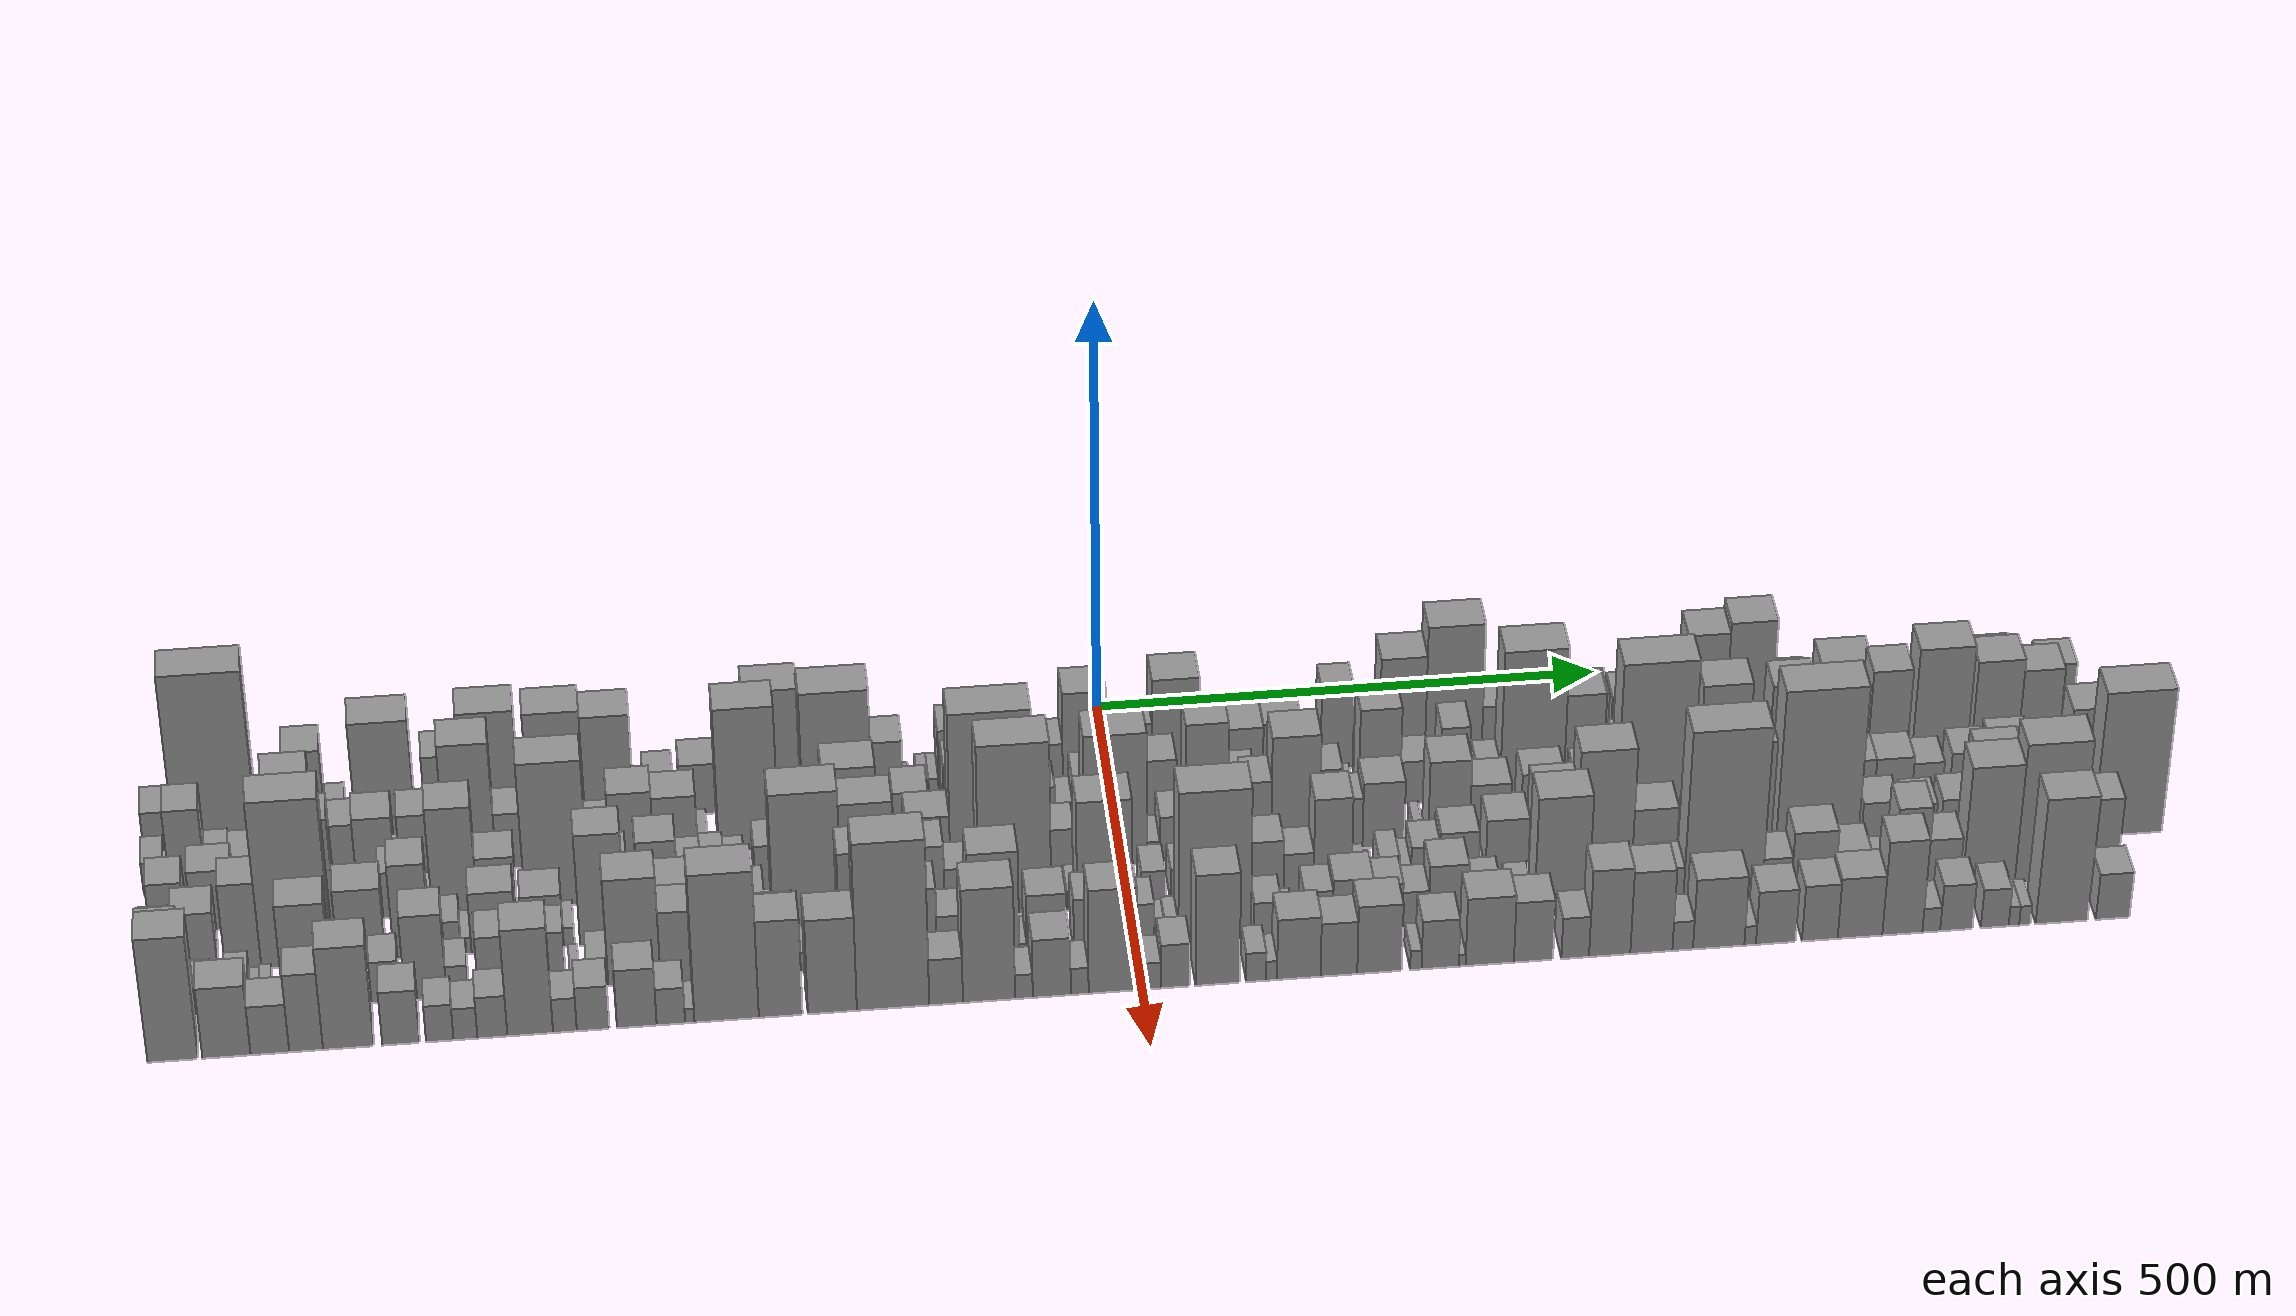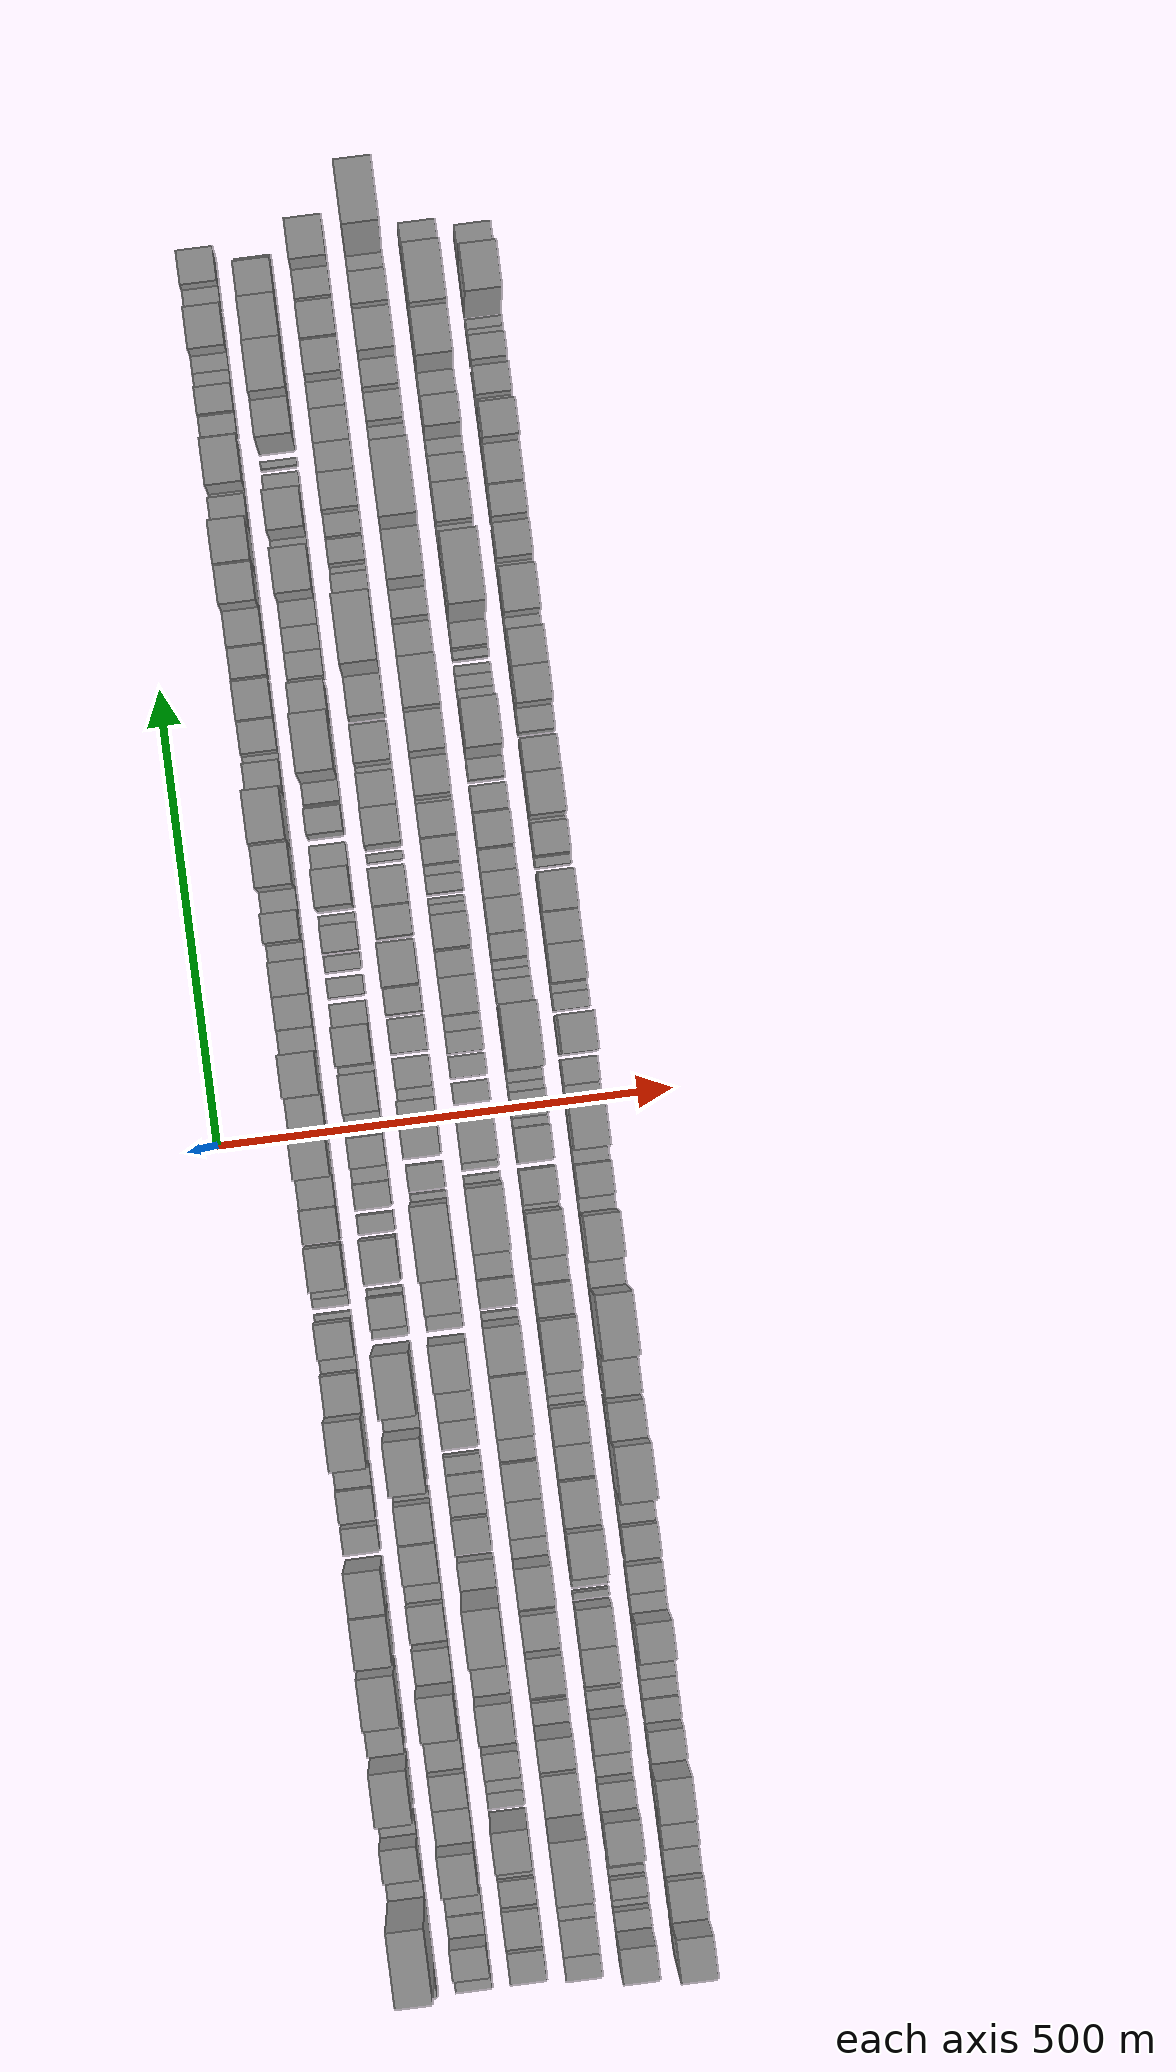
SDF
<sdf version="1.6">
 <world name="default">
  <scene>
   <sky><clouds><speed>12</speed></clouds></sky>
   <ambient>0.4 0.4 0.4 1</ambient>
   <background>0.7 0.7 0.7 1</background>
   <shadows>1</shadows>
  </scene>
  <gravity>0 0 -9.8066</gravity>
  <magnetic_field>6e-06 2.3e-05 -4.2e-05</magnetic_field>
  <physics default="0" name="default_physics" type="ode">
   <ode>
    <solver>
     <type>quick</type>
     <iters>10</iters>
     <sor>1.0</sor>
     <use_dynamic_moi_rescaling>0</use_dynamic_moi_rescaling>
    </solver>
    <constraints>
     <cfm>0</cfm>
     <erp>0.2</erp>
     <contact_max_correcting_vel>100</contact_max_correcting_vel>
     <contact_surface_layer>0.001</contact_surface_layer>
    </constraints>
   </ode>
   <max_step_size>0.004</max_step_size>
   <real_time_factor>1</real_time_factor>
   <real_time_update_rate>250</real_time_update_rate>
  </physics>
  <light name="sun" type="directional">
   <pose>0 0 10 0 0 0</pose>
   <diffuse>0.8 0.8 0.8 1</diffuse>
   <specular>0.2 0.2 0.2 1</specular>
   <attenuation>
    <range>1000</range>
    <constant>0.9</constant>
    <linear>0.01</linear>
    <quadratic>0.001</quadratic>
   </attenuation>
   <direction>-0.5 0.1 -0.9</direction>
  </light>
  <model name="building_1">
   <static>1</static>
   <pose>100.0000 -924.9908 0 0.000000 0.000000 0.000000</pose>
   <link name="link">
    <pose>0 0 25.50 0 0 0</pose>
    <collision name="collision"><geometry><box><size>40.0000 30.0183 51.0000</size></box></geometry></collision>
    <visual name="visual">
     <cast_shadows>0</cast_shadows>
     <geometry><box><size>40.0000 30.0183 51.0000</size></box></geometry>
     <material>
      <script>
       <uri>model://grey_wall/materials/scripts</uri>
       <uri>model://grey_wall/materials/textures</uri>
       <name>vrc/grey_wall</name>
      </script>
     </material>
    </visual>
   </link>
  </model>
  <model name="building_2">
   <static>1</static>
   <pose>100.0000 -869.9235 0 0.000000 0.000000 0.000000</pose>
   <link name="link">
    <pose>0 0 109.50 0 0 0</pose>
    <collision name="collision"><geometry><box><size>40.0000 80.1163 219.0000</size></box></geometry></collision>
    <visual name="visual">
     <cast_shadows>0</cast_shadows>
     <geometry><box><size>40.0000 80.1163 219.0000</size></box></geometry>
     <material>
      <script>
       <uri>model://grey_wall/materials/scripts</uri>
       <uri>model://grey_wall/materials/textures</uri>
       <name>vrc/grey_wall</name>
      </script>
     </material>
    </visual>
   </link>
  </model>
  <model name="building_3">
   <static>1</static>
   <pose>100.0000 -814.7884 0 0.000000 0.000000 0.000000</pose>
   <link name="link">
    <pose>0 0 25.50 0 0 0</pose>
    <collision name="collision"><geometry><box><size>40.0000 30.1539 51.0000</size></box></geometry></collision>
    <visual name="visual">
     <cast_shadows>0</cast_shadows>
     <geometry><box><size>40.0000 30.1539 51.0000</size></box></geometry>
     <material>
      <script>
       <uri>model://grey_wall/materials/scripts</uri>
       <uri>model://grey_wall/materials/textures</uri>
       <name>vrc/grey_wall</name>
      </script>
     </material>
    </visual>
   </link>
  </model>
  <model name="building_4">
   <static>1</static>
   <pose>100.0000 -781.5374 0 0.000000 0.000000 0.000000</pose>
   <link name="link">
    <pose>0 0 57.00 0 0 0</pose>
    <collision name="collision"><geometry><box><size>40.0000 36.3481 114.0000</size></box></geometry></collision>
    <visual name="visual">
     <cast_shadows>0</cast_shadows>
     <geometry><box><size>40.0000 36.3481 114.0000</size></box></geometry>
     <material>
      <script>
       <uri>model://grey_wall/materials/scripts</uri>
       <uri>model://grey_wall/materials/textures</uri>
       <name>vrc/grey_wall</name>
      </script>
     </material>
    </visual>
   </link>
  </model>
  <model name="building_5">
   <static>1</static>
   <pose>100.0000 -753.4483 0 0.000000 0.000000 0.000000</pose>
   <link name="link">
    <pose>0 0 19.50 0 0 0</pose>
    <collision name="collision"><geometry><box><size>40.0000 19.8302 39.0000</size></box></geometry></collision>
    <visual name="visual">
     <cast_shadows>0</cast_shadows>
     <geometry><box><size>40.0000 19.8302 39.0000</size></box></geometry>
     <material>
      <script>
       <uri>model://grey_wall/materials/scripts</uri>
       <uri>model://grey_wall/materials/textures</uri>
       <name>vrc/grey_wall</name>
      </script>
     </material>
    </visual>
   </link>
  </model>
  <model name="building_6">
   <static>1</static>
   <pose>100.0000 -705.7609 0 0.000000 0.000000 0.000000</pose>
   <link name="link">
    <pose>0 0 72.00 0 0 0</pose>
    <collision name="collision"><geometry><box><size>40.0000 57.5447 144.0000</size></box></geometry></collision>
    <visual name="visual">
     <cast_shadows>0</cast_shadows>
     <geometry><box><size>40.0000 57.5447 144.0000</size></box></geometry>
     <material>
      <script>
       <uri>model://grey_wall/materials/scripts</uri>
       <uri>model://grey_wall/materials/textures</uri>
       <name>vrc/grey_wall</name>
      </script>
     </material>
    </visual>
   </link>
  </model>
  <model name="building_7">
   <static>1</static>
   <pose>100.0000 -649.0936 0 0.000000 0.000000 0.000000</pose>
   <link name="link">
    <pose>0 0 48.00 0 0 0</pose>
    <collision name="collision"><geometry><box><size>40.0000 35.7898 96.0000</size></box></geometry></collision>
    <visual name="visual">
     <cast_shadows>0</cast_shadows>
     <geometry><box><size>40.0000 35.7898 96.0000</size></box></geometry>
     <material>
      <script>
       <uri>model://grey_wall/materials/scripts</uri>
       <uri>model://grey_wall/materials/textures</uri>
       <name>vrc/grey_wall</name>
      </script>
     </material>
    </visual>
   </link>
  </model>
  <model name="building_8">
   <static>1</static>
   <pose>100.0000 -603.2705 0 0.000000 0.000000 0.000000</pose>
   <link name="link">
    <pose>0 0 73.50 0 0 0</pose>
    <collision name="collision"><geometry><box><size>40.0000 55.8565 147.0000</size></box></geometry></collision>
    <visual name="visual">
     <cast_shadows>0</cast_shadows>
     <geometry><box><size>40.0000 55.8565 147.0000</size></box></geometry>
     <material>
      <script>
       <uri>model://grey_wall/materials/scripts</uri>
       <uri>model://grey_wall/materials/textures</uri>
       <name>vrc/grey_wall</name>
      </script>
     </material>
    </visual>
   </link>
  </model>
  <model name="building_9">
   <static>1</static>
   <pose>100.0000 -540.0875 0 0.000000 0.000000 0.000000</pose>
   <link name="link">
    <pose>0 0 70.50 0 0 0</pose>
    <collision name="collision"><geometry><box><size>40.0000 54.5095 141.0000</size></box></geometry></collision>
    <visual name="visual">
     <cast_shadows>0</cast_shadows>
     <geometry><box><size>40.0000 54.5095 141.0000</size></box></geometry>
     <material>
      <script>
       <uri>model://grey_wall/materials/scripts</uri>
       <uri>model://grey_wall/materials/textures</uri>
       <name>vrc/grey_wall</name>
      </script>
     </material>
    </visual>
   </link>
  </model>
  <model name="building_10">
   <static>1</static>
   <pose>100.0000 -488.8670 0 0.000000 0.000000 0.000000</pose>
   <link name="link">
    <pose>0 0 66.00 0 0 0</pose>
    <collision name="collision"><geometry><box><size>40.0000 47.9315 132.0000</size></box></geometry></collision>
    <visual name="visual">
     <cast_shadows>0</cast_shadows>
     <geometry><box><size>40.0000 47.9315 132.0000</size></box></geometry>
     <material>
      <script>
       <uri>model://grey_wall/materials/scripts</uri>
       <uri>model://grey_wall/materials/textures</uri>
       <name>vrc/grey_wall</name>
      </script>
     </material>
    </visual>
   </link>
  </model>
  <model name="building_11">
   <static>1</static>
   <pose>100.0000 -440.4301 0 0.000000 0.000000 0.000000</pose>
   <link name="link">
    <pose>0 0 25.50 0 0 0</pose>
    <collision name="collision"><geometry><box><size>40.0000 28.9423 51.0000</size></box></geometry></collision>
    <visual name="visual">
     <cast_shadows>0</cast_shadows>
     <geometry><box><size>40.0000 28.9423 51.0000</size></box></geometry>
     <material>
      <script>
       <uri>model://grey_wall/materials/scripts</uri>
       <uri>model://grey_wall/materials/textures</uri>
       <name>vrc/grey_wall</name>
      </script>
     </material>
    </visual>
   </link>
  </model>
  <model name="building_12">
   <static>1</static>
   <pose>100.0000 -401.9817 0 0.000000 0.000000 0.000000</pose>
   <link name="link">
    <pose>0 0 31.50 0 0 0</pose>
    <collision name="collision"><geometry><box><size>40.0000 35.9544 63.0000</size></box></geometry></collision>
    <visual name="visual">
     <cast_shadows>0</cast_shadows>
     <geometry><box><size>40.0000 35.9544 63.0000</size></box></geometry>
     <material>
      <script>
       <uri>model://grey_wall/materials/scripts</uri>
       <uri>model://grey_wall/materials/textures</uri>
       <name>vrc/grey_wall</name>
      </script>
     </material>
    </visual>
   </link>
  </model>
  <model name="building_13">
   <static>1</static>
   <pose>100.0000 -372.3610 0 0.000000 0.000000 0.000000</pose>
   <link name="link">
    <pose>0 0 22.50 0 0 0</pose>
    <collision name="collision"><geometry><box><size>40.0000 23.2870 45.0000</size></box></geometry></collision>
    <visual name="visual">
     <cast_shadows>0</cast_shadows>
     <geometry><box><size>40.0000 23.2870 45.0000</size></box></geometry>
     <material>
      <script>
       <uri>model://grey_wall/materials/scripts</uri>
       <uri>model://grey_wall/materials/textures</uri>
       <name>vrc/grey_wall</name>
      </script>
     </material>
    </visual>
   </link>
  </model>
  <model name="building_14">
   <static>1</static>
   <pose>100.0000 -329.1677 0 0.000000 0.000000 0.000000</pose>
   <link name="link">
    <pose>0 0 75.00 0 0 0</pose>
    <collision name="collision"><geometry><box><size>40.0000 53.0995 150.0000</size></box></geometry></collision>
    <visual name="visual">
     <cast_shadows>0</cast_shadows>
     <geometry><box><size>40.0000 53.0995 150.0000</size></box></geometry>
     <material>
      <script>
       <uri>model://grey_wall/materials/scripts</uri>
       <uri>model://grey_wall/materials/textures</uri>
       <name>vrc/grey_wall</name>
      </script>
     </material>
    </visual>
   </link>
  </model>
  <model name="building_15">
   <static>1</static>
   <pose>100.0000 -280.5024 0 0.000000 0.000000 0.000000</pose>
   <link name="link">
    <pose>0 0 37.50 0 0 0</pose>
    <collision name="collision"><geometry><box><size>40.0000 44.2311 75.0000</size></box></geometry></collision>
    <visual name="visual">
     <cast_shadows>0</cast_shadows>
     <geometry><box><size>40.0000 44.2311 75.0000</size></box></geometry>
     <material>
      <script>
       <uri>model://grey_wall/materials/scripts</uri>
       <uri>model://grey_wall/materials/textures</uri>
       <name>vrc/grey_wall</name>
      </script>
     </material>
    </visual>
   </link>
  </model>
  <model name="building_16">
   <static>1</static>
   <pose>100.0000 -249.8312 0 0.000000 0.000000 0.000000</pose>
   <link name="link">
    <pose>0 0 16.50 0 0 0</pose>
    <collision name="collision"><geometry><box><size>40.0000 17.1114 33.0000</size></box></geometry></collision>
    <visual name="visual">
     <cast_shadows>0</cast_shadows>
     <geometry><box><size>40.0000 17.1114 33.0000</size></box></geometry>
     <material>
      <script>
       <uri>model://grey_wall/materials/scripts</uri>
       <uri>model://grey_wall/materials/textures</uri>
       <name>vrc/grey_wall</name>
      </script>
     </material>
    </visual>
   </link>
  </model>
  <model name="building_17">
   <static>1</static>
   <pose>100.0000 -221.9073 0 0.000000 0.000000 0.000000</pose>
   <link name="link">
    <pose>0 0 37.50 0 0 0</pose>
    <collision name="collision"><geometry><box><size>40.0000 38.7364 75.0000</size></box></geometry></collision>
    <visual name="visual">
     <cast_shadows>0</cast_shadows>
     <geometry><box><size>40.0000 38.7364 75.0000</size></box></geometry>
     <material>
      <script>
       <uri>model://grey_wall/materials/scripts</uri>
       <uri>model://grey_wall/materials/textures</uri>
       <name>vrc/grey_wall</name>
      </script>
     </material>
    </visual>
   </link>
  </model>
  <model name="building_18">
   <static>1</static>
   <pose>100.0000 -198.8812 0 0.000000 0.000000 0.000000</pose>
   <link name="link">
    <pose>0 0 7.50 0 0 0</pose>
    <collision name="collision"><geometry><box><size>40.0000 7.3159 15.0000</size></box></geometry></collision>
    <visual name="visual">
     <cast_shadows>0</cast_shadows>
     <geometry><box><size>40.0000 7.3159 15.0000</size></box></geometry>
     <material>
      <script>
       <uri>model://grey_wall/materials/scripts</uri>
       <uri>model://grey_wall/materials/textures</uri>
       <name>vrc/grey_wall</name>
      </script>
     </material>
    </visual>
   </link>
  </model>
  <model name="building_19">
   <static>1</static>
   <pose>100.0000 -182.9020 0 0.000000 0.000000 0.000000</pose>
   <link name="link">
    <pose>0 0 12.00 0 0 0</pose>
    <collision name="collision"><geometry><box><size>40.0000 10.6424 24.0000</size></box></geometry></collision>
    <visual name="visual">
     <cast_shadows>0</cast_shadows>
     <geometry><box><size>40.0000 10.6424 24.0000</size></box></geometry>
     <material>
      <script>
       <uri>model://grey_wall/materials/scripts</uri>
       <uri>model://grey_wall/materials/textures</uri>
       <name>vrc/grey_wall</name>
      </script>
     </material>
    </visual>
   </link>
  </model>
  <model name="building_20">
   <static>1</static>
   <pose>100.0000 -172.7085 0 0.000000 0.000000 0.000000</pose>
   <link name="link">
    <pose>0 0 12.00 0 0 0</pose>
    <collision name="collision"><geometry><box><size>40.0000 9.7446 24.0000</size></box></geometry></collision>
    <visual name="visual">
     <cast_shadows>0</cast_shadows>
     <geometry><box><size>40.0000 9.7446 24.0000</size></box></geometry>
     <material>
      <script>
       <uri>model://grey_wall/materials/scripts</uri>
       <uri>model://grey_wall/materials/textures</uri>
       <name>vrc/grey_wall</name>
      </script>
     </material>
    </visual>
   </link>
  </model>
  <model name="building_21">
   <static>1</static>
   <pose>100.0000 -144.0142 0 0.000000 0.000000 0.000000</pose>
   <link name="link">
    <pose>0 0 42.00 0 0 0</pose>
    <collision name="collision"><geometry><box><size>40.0000 47.6441 84.0000</size></box></geometry></collision>
    <visual name="visual">
     <cast_shadows>0</cast_shadows>
     <geometry><box><size>40.0000 47.6441 84.0000</size></box></geometry>
     <material>
      <script>
       <uri>model://grey_wall/materials/scripts</uri>
       <uri>model://grey_wall/materials/textures</uri>
       <name>vrc/grey_wall</name>
      </script>
     </material>
    </visual>
   </link>
  </model>
  <model name="building_22">
   <static>1</static>
   <pose>100.0000 -98.3070 0 0.000000 0.000000 0.000000</pose>
   <link name="link">
    <pose>0 0 36.00 0 0 0</pose>
    <collision name="collision"><geometry><box><size>40.0000 37.7701 72.0000</size></box></geometry></collision>
    <visual name="visual">
     <cast_shadows>0</cast_shadows>
     <geometry><box><size>40.0000 37.7701 72.0000</size></box></geometry>
     <material>
      <script>
       <uri>model://grey_wall/materials/scripts</uri>
       <uri>model://grey_wall/materials/textures</uri>
       <name>vrc/grey_wall</name>
      </script>
     </material>
    </visual>
   </link>
  </model>
  <model name="building_23">
   <static>1</static>
   <pose>100.0000 -62.7000 0 0.000000 0.000000 0.000000</pose>
   <link name="link">
    <pose>0 0 28.50 0 0 0</pose>
    <collision name="collision"><geometry><box><size>40.0000 33.4441 57.0000</size></box></geometry></collision>
    <visual name="visual">
     <cast_shadows>0</cast_shadows>
     <geometry><box><size>40.0000 33.4441 57.0000</size></box></geometry>
     <material>
      <script>
       <uri>model://grey_wall/materials/scripts</uri>
       <uri>model://grey_wall/materials/textures</uri>
       <name>vrc/grey_wall</name>
      </script>
     </material>
    </visual>
   </link>
  </model>
  <model name="building_24">
   <static>1</static>
   <pose>100.0000 -24.4865 0 0.000000 0.000000 0.000000</pose>
   <link name="link">
    <pose>0 0 60.00 0 0 0</pose>
    <collision name="collision"><geometry><box><size>40.0000 42.9828 120.0000</size></box></geometry></collision>
    <visual name="visual">
     <cast_shadows>0</cast_shadows>
     <geometry><box><size>40.0000 42.9828 120.0000</size></box></geometry>
     <material>
      <script>
       <uri>model://grey_wall/materials/scripts</uri>
       <uri>model://grey_wall/materials/textures</uri>
       <name>vrc/grey_wall</name>
      </script>
     </material>
    </visual>
   </link>
  </model>
  <model name="building_25">
   <static>1</static>
   <pose>100.0000 0.1174 0 0.000000 0.000000 0.000000</pose>
   <link name="link">
    <pose>0 0 7.50 0 0 0</pose>
    <collision name="collision"><geometry><box><size>40.0000 6.2250 15.0000</size></box></geometry></collision>
    <visual name="visual">
     <cast_shadows>0</cast_shadows>
     <geometry><box><size>40.0000 6.2250 15.0000</size></box></geometry>
     <material>
      <script>
       <uri>model://grey_wall/materials/scripts</uri>
       <uri>model://grey_wall/materials/textures</uri>
       <name>vrc/grey_wall</name>
      </script>
     </material>
    </visual>
   </link>
  </model>
  <model name="building_26">
   <static>1</static>
   <pose>100.0000 22.4754 0 0.000000 0.000000 0.000000</pose>
   <link name="link">
    <pose>0 0 37.50 0 0 0</pose>
    <collision name="collision"><geometry><box><size>40.0000 38.4909 75.0000</size></box></geometry></collision>
    <visual name="visual">
     <cast_shadows>0</cast_shadows>
     <geometry><box><size>40.0000 38.4909 75.0000</size></box></geometry>
     <material>
      <script>
       <uri>model://grey_wall/materials/scripts</uri>
       <uri>model://grey_wall/materials/textures</uri>
       <name>vrc/grey_wall</name>
      </script>
     </material>
    </visual>
   </link>
  </model>
  <model name="building_27">
   <static>1</static>
   <pose>100.0000 64.9591 0 0.000000 0.000000 0.000000</pose>
   <link name="link">
    <pose>0 0 64.50 0 0 0</pose>
    <collision name="collision"><geometry><box><size>40.0000 46.4764 129.0000</size></box></geometry></collision>
    <visual name="visual">
     <cast_shadows>0</cast_shadows>
     <geometry><box><size>40.0000 46.4764 129.0000</size></box></geometry>
     <material>
      <script>
       <uri>model://grey_wall/materials/scripts</uri>
       <uri>model://grey_wall/materials/textures</uri>
       <name>vrc/grey_wall</name>
      </script>
     </material>
    </visual>
   </link>
  </model>
  <model name="building_28">
   <static>1</static>
   <pose>100.0000 101.8593 0 0.000000 0.000000 0.000000</pose>
   <link name="link">
    <pose>0 0 24.00 0 0 0</pose>
    <collision name="collision"><geometry><box><size>40.0000 27.3241 48.0000</size></box></geometry></collision>
    <visual name="visual">
     <cast_shadows>0</cast_shadows>
     <geometry><box><size>40.0000 27.3241 48.0000</size></box></geometry>
     <material>
      <script>
       <uri>model://grey_wall/materials/scripts</uri>
       <uri>model://grey_wall/materials/textures</uri>
       <name>vrc/grey_wall</name>
      </script>
     </material>
    </visual>
   </link>
  </model>
  <model name="building_29">
   <static>1</static>
   <pose>100.0000 133.4685 0 0.000000 0.000000 0.000000</pose>
   <link name="link">
    <pose>0 0 30.00 0 0 0</pose>
    <collision name="collision"><geometry><box><size>40.0000 35.8943 60.0000</size></box></geometry></collision>
    <visual name="visual">
     <cast_shadows>0</cast_shadows>
     <geometry><box><size>40.0000 35.8943 60.0000</size></box></geometry>
     <material>
      <script>
       <uri>model://grey_wall/materials/scripts</uri>
       <uri>model://grey_wall/materials/textures</uri>
       <name>vrc/grey_wall</name>
      </script>
     </material>
    </visual>
   </link>
  </model>
  <model name="building_30">
   <static>1</static>
   <pose>100.0000 170.2295 0 0.000000 0.000000 0.000000</pose>
   <link name="link">
    <pose>0 0 31.50 0 0 0</pose>
    <collision name="collision"><geometry><box><size>40.0000 37.6278 63.0000</size></box></geometry></collision>
    <visual name="visual">
     <cast_shadows>0</cast_shadows>
     <geometry><box><size>40.0000 37.6278 63.0000</size></box></geometry>
     <material>
      <script>
       <uri>model://grey_wall/materials/scripts</uri>
       <uri>model://grey_wall/materials/textures</uri>
       <name>vrc/grey_wall</name>
      </script>
     </material>
    </visual>
   </link>
  </model>
  <model name="building_31">
   <static>1</static>
   <pose>100.0000 198.6145 0 0.000000 0.000000 0.000000</pose>
   <link name="link">
    <pose>0 0 16.50 0 0 0</pose>
    <collision name="collision"><geometry><box><size>40.0000 19.1421 33.0000</size></box></geometry></collision>
    <visual name="visual">
     <cast_shadows>0</cast_shadows>
     <geometry><box><size>40.0000 19.1421 33.0000</size></box></geometry>
     <material>
      <script>
       <uri>model://grey_wall/materials/scripts</uri>
       <uri>model://grey_wall/materials/textures</uri>
       <name>vrc/grey_wall</name>
      </script>
     </material>
    </visual>
   </link>
  </model>
  <model name="building_32">
   <static>1</static>
   <pose>100.0000 224.0683 0 0.000000 0.000000 0.000000</pose>
   <link name="link">
    <pose>0 0 51.00 0 0 0</pose>
    <collision name="collision"><geometry><box><size>40.0000 31.7655 102.0000</size></box></geometry></collision>
    <visual name="visual">
     <cast_shadows>0</cast_shadows>
     <geometry><box><size>40.0000 31.7655 102.0000</size></box></geometry>
     <material>
      <script>
       <uri>model://grey_wall/materials/scripts</uri>
       <uri>model://grey_wall/materials/textures</uri>
       <name>vrc/grey_wall</name>
      </script>
     </material>
    </visual>
   </link>
  </model>
  <model name="building_33">
   <static>1</static>
   <pose>100.0000 253.0568 0 0.000000 0.000000 0.000000</pose>
   <link name="link">
    <pose>0 0 22.50 0 0 0</pose>
    <collision name="collision"><geometry><box><size>40.0000 26.2116 45.0000</size></box></geometry></collision>
    <visual name="visual">
     <cast_shadows>0</cast_shadows>
     <geometry><box><size>40.0000 26.2116 45.0000</size></box></geometry>
     <material>
      <script>
       <uri>model://grey_wall/materials/scripts</uri>
       <uri>model://grey_wall/materials/textures</uri>
       <name>vrc/grey_wall</name>
      </script>
     </material>
    </visual>
   </link>
  </model>
  <model name="building_34">
   <static>1</static>
   <pose>100.0000 288.7687 0 0.000000 0.000000 0.000000</pose>
   <link name="link">
    <pose>0 0 67.50 0 0 0</pose>
    <collision name="collision"><geometry><box><size>40.0000 45.2121 135.0000</size></box></geometry></collision>
    <visual name="visual">
     <cast_shadows>0</cast_shadows>
     <geometry><box><size>40.0000 45.2121 135.0000</size></box></geometry>
     <material>
      <script>
       <uri>model://grey_wall/materials/scripts</uri>
       <uri>model://grey_wall/materials/textures</uri>
       <name>vrc/grey_wall</name>
      </script>
     </material>
    </visual>
   </link>
  </model>
  <model name="building_35">
   <static>1</static>
   <pose>100.0000 339.5329 0 0.000000 0.000000 0.000000</pose>
   <link name="link">
    <pose>0 0 85.50 0 0 0</pose>
    <collision name="collision"><geometry><box><size>40.0000 56.3162 171.0000</size></box></geometry></collision>
    <visual name="visual">
     <cast_shadows>0</cast_shadows>
     <geometry><box><size>40.0000 56.3162 171.0000</size></box></geometry>
     <material>
      <script>
       <uri>model://grey_wall/materials/scripts</uri>
       <uri>model://grey_wall/materials/textures</uri>
       <name>vrc/grey_wall</name>
      </script>
     </material>
    </visual>
   </link>
  </model>
  <model name="building_36">
   <static>1</static>
   <pose>100.0000 386.1106 0 0.000000 0.000000 0.000000</pose>
   <link name="link">
    <pose>0 0 33.00 0 0 0</pose>
    <collision name="collision"><geometry><box><size>40.0000 36.8392 66.0000</size></box></geometry></collision>
    <visual name="visual">
     <cast_shadows>0</cast_shadows>
     <geometry><box><size>40.0000 36.8392 66.0000</size></box></geometry>
     <material>
      <script>
       <uri>model://grey_wall/materials/scripts</uri>
       <uri>model://grey_wall/materials/textures</uri>
       <name>vrc/grey_wall</name>
      </script>
     </material>
    </visual>
   </link>
  </model>
  <model name="building_37">
   <static>1</static>
   <pose>100.0000 409.8533 0 0.000000 0.000000 0.000000</pose>
   <link name="link">
    <pose>0 0 12.00 0 0 0</pose>
    <collision name="collision"><geometry><box><size>40.0000 10.6462 24.0000</size></box></geometry></collision>
    <visual name="visual">
     <cast_shadows>0</cast_shadows>
     <geometry><box><size>40.0000 10.6462 24.0000</size></box></geometry>
     <material>
      <script>
       <uri>model://grey_wall/materials/scripts</uri>
       <uri>model://grey_wall/materials/textures</uri>
       <name>vrc/grey_wall</name>
      </script>
     </material>
    </visual>
   </link>
  </model>
  <model name="building_38">
   <static>1</static>
   <pose>100.0000 432.6948 0 0.000000 0.000000 0.000000</pose>
   <link name="link">
    <pose>0 0 30.00 0 0 0</pose>
    <collision name="collision"><geometry><box><size>40.0000 35.0368 60.0000</size></box></geometry></collision>
    <visual name="visual">
     <cast_shadows>0</cast_shadows>
     <geometry><box><size>40.0000 35.0368 60.0000</size></box></geometry>
     <material>
      <script>
       <uri>model://grey_wall/materials/scripts</uri>
       <uri>model://grey_wall/materials/textures</uri>
       <name>vrc/grey_wall</name>
      </script>
     </material>
    </visual>
   </link>
  </model>
  <model name="building_39">
   <static>1</static>
   <pose>100.0000 471.5594 0 0.000000 0.000000 0.000000</pose>
   <link name="link">
    <pose>0 0 36.00 0 0 0</pose>
    <collision name="collision"><geometry><box><size>40.0000 42.6924 72.0000</size></box></geometry></collision>
    <visual name="visual">
     <cast_shadows>0</cast_shadows>
     <geometry><box><size>40.0000 42.6924 72.0000</size></box></geometry>
     <material>
      <script>
       <uri>model://grey_wall/materials/scripts</uri>
       <uri>model://grey_wall/materials/textures</uri>
       <name>vrc/grey_wall</name>
      </script>
     </material>
    </visual>
   </link>
  </model>
  <model name="building_40">
   <static>1</static>
   <pose>100.0000 512.6426 0 0.000000 0.000000 0.000000</pose>
   <link name="link">
    <pose>0 0 33.00 0 0 0</pose>
    <collision name="collision"><geometry><box><size>40.0000 33.4740 66.0000</size></box></geometry></collision>
    <visual name="visual">
     <cast_shadows>0</cast_shadows>
     <geometry><box><size>40.0000 33.4740 66.0000</size></box></geometry>
     <material>
      <script>
       <uri>model://grey_wall/materials/scripts</uri>
       <uri>model://grey_wall/materials/textures</uri>
       <name>vrc/grey_wall</name>
      </script>
     </material>
    </visual>
   </link>
  </model>
  <model name="building_41">
   <static>1</static>
   <pose>100.0000 548.7617 0 0.000000 0.000000 0.000000</pose>
   <link name="link">
    <pose>0 0 37.50 0 0 0</pose>
    <collision name="collision"><geometry><box><size>40.0000 38.7641 75.0000</size></box></geometry></collision>
    <visual name="visual">
     <cast_shadows>0</cast_shadows>
     <geometry><box><size>40.0000 38.7641 75.0000</size></box></geometry>
     <material>
      <script>
       <uri>model://grey_wall/materials/scripts</uri>
       <uri>model://grey_wall/materials/textures</uri>
       <name>vrc/grey_wall</name>
      </script>
     </material>
    </visual>
   </link>
  </model>
  <model name="building_42">
   <static>1</static>
   <pose>100.0000 588.9424 0 0.000000 0.000000 0.000000</pose>
   <link name="link">
    <pose>0 0 69.00 0 0 0</pose>
    <collision name="collision"><geometry><box><size>40.0000 41.5972 138.0000</size></box></geometry></collision>
    <visual name="visual">
     <cast_shadows>0</cast_shadows>
     <geometry><box><size>40.0000 41.5972 138.0000</size></box></geometry>
     <material>
      <script>
       <uri>model://grey_wall/materials/scripts</uri>
       <uri>model://grey_wall/materials/textures</uri>
       <name>vrc/grey_wall</name>
      </script>
     </material>
    </visual>
   </link>
  </model>
  <model name="building_43">
   <static>1</static>
   <pose>100.0000 633.0109 0 0.000000 0.000000 0.000000</pose>
   <link name="link">
    <pose>0 0 75.00 0 0 0</pose>
    <collision name="collision"><geometry><box><size>40.0000 46.5398 150.0000</size></box></geometry></collision>
    <visual name="visual">
     <cast_shadows>0</cast_shadows>
     <geometry><box><size>40.0000 46.5398 150.0000</size></box></geometry>
     <material>
      <script>
       <uri>model://grey_wall/materials/scripts</uri>
       <uri>model://grey_wall/materials/textures</uri>
       <name>vrc/grey_wall</name>
      </script>
     </material>
    </visual>
   </link>
  </model>
  <model name="building_44">
   <static>1</static>
   <pose>100.0000 674.1414 0 0.000000 0.000000 0.000000</pose>
   <link name="link">
    <pose>0 0 34.50 0 0 0</pose>
    <collision name="collision"><geometry><box><size>40.0000 35.7212 69.0000</size></box></geometry></collision>
    <visual name="visual">
     <cast_shadows>0</cast_shadows>
     <geometry><box><size>40.0000 35.7212 69.0000</size></box></geometry>
     <material>
      <script>
       <uri>model://grey_wall/materials/scripts</uri>
       <uri>model://grey_wall/materials/textures</uri>
       <name>vrc/grey_wall</name>
      </script>
     </material>
    </visual>
   </link>
  </model>
  <model name="building_45">
   <static>1</static>
   <pose>100.0000 697.1160 0 0.000000 0.000000 0.000000</pose>
   <link name="link">
    <pose>0 0 10.50 0 0 0</pose>
    <collision name="collision"><geometry><box><size>40.0000 10.2280 21.0000</size></box></geometry></collision>
    <visual name="visual">
     <cast_shadows>0</cast_shadows>
     <geometry><box><size>40.0000 10.2280 21.0000</size></box></geometry>
     <material>
      <script>
       <uri>model://grey_wall/materials/scripts</uri>
       <uri>model://grey_wall/materials/textures</uri>
       <name>vrc/grey_wall</name>
      </script>
     </material>
    </visual>
   </link>
  </model>
  <model name="building_46">
   <static>1</static>
   <pose>100.0000 727.5770 0 0.000000 0.000000 0.000000</pose>
   <link name="link">
    <pose>0 0 45.00 0 0 0</pose>
    <collision name="collision"><geometry><box><size>40.0000 50.6938 90.0000</size></box></geometry></collision>
    <visual name="visual">
     <cast_shadows>0</cast_shadows>
     <geometry><box><size>40.0000 50.6938 90.0000</size></box></geometry>
     <material>
      <script>
       <uri>model://grey_wall/materials/scripts</uri>
       <uri>model://grey_wall/materials/textures</uri>
       <name>vrc/grey_wall</name>
      </script>
     </material>
    </visual>
   </link>
  </model>
  <model name="building_47">
   <static>1</static>
   <pose>100.0000 772.2596 0 0.000000 0.000000 0.000000</pose>
   <link name="link">
    <pose>0 0 22.50 0 0 0</pose>
    <collision name="collision"><geometry><box><size>40.0000 22.6715 45.0000</size></box></geometry></collision>
    <visual name="visual">
     <cast_shadows>0</cast_shadows>
     <geometry><box><size>40.0000 22.6715 45.0000</size></box></geometry>
     <material>
      <script>
       <uri>model://grey_wall/materials/scripts</uri>
       <uri>model://grey_wall/materials/textures</uri>
       <name>vrc/grey_wall</name>
      </script>
     </material>
    </visual>
   </link>
  </model>
  <model name="building_48">
   <static>1</static>
   <pose>100.0000 798.6572 0 0.000000 0.000000 0.000000</pose>
   <link name="link">
    <pose>0 0 28.50 0 0 0</pose>
    <collision name="collision"><geometry><box><size>40.0000 30.1238 57.0000</size></box></geometry></collision>
    <visual name="visual">
     <cast_shadows>0</cast_shadows>
     <geometry><box><size>40.0000 30.1238 57.0000</size></box></geometry>
     <material>
      <script>
       <uri>model://grey_wall/materials/scripts</uri>
       <uri>model://grey_wall/materials/textures</uri>
       <name>vrc/grey_wall</name>
      </script>
     </material>
    </visual>
   </link>
  </model>
  <model name="building_49">
   <static>1</static>
   <pose>100.0000 822.7198 0 0.000000 0.000000 0.000000</pose>
   <link name="link">
    <pose>0 0 18.00 0 0 0</pose>
    <collision name="collision"><geometry><box><size>40.0000 18.0014 36.0000</size></box></geometry></collision>
    <visual name="visual">
     <cast_shadows>0</cast_shadows>
     <geometry><box><size>40.0000 18.0014 36.0000</size></box></geometry>
     <material>
      <script>
       <uri>model://grey_wall/materials/scripts</uri>
       <uri>model://grey_wall/materials/textures</uri>
       <name>vrc/grey_wall</name>
      </script>
     </material>
    </visual>
   </link>
  </model>
  <model name="building_50">
   <static>1</static>
   <pose>100.0000 841.1278 0 0.000000 0.000000 0.000000</pose>
   <link name="link">
    <pose>0 0 18.00 0 0 0</pose>
    <collision name="collision"><geometry><box><size>40.0000 18.8147 36.0000</size></box></geometry></collision>
    <visual name="visual">
     <cast_shadows>0</cast_shadows>
     <geometry><box><size>40.0000 18.8147 36.0000</size></box></geometry>
     <material>
      <script>
       <uri>model://grey_wall/materials/scripts</uri>
       <uri>model://grey_wall/materials/textures</uri>
       <name>vrc/grey_wall</name>
      </script>
     </material>
    </visual>
   </link>
  </model>
  <model name="building_51">
   <static>1</static>
   <pose>100.0000 873.2717 0 0.000000 0.000000 0.000000</pose>
   <link name="link">
    <pose>0 0 40.50 0 0 0</pose>
    <collision name="collision"><geometry><box><size>40.0000 45.4730 81.0000</size></box></geometry></collision>
    <visual name="visual">
     <cast_shadows>0</cast_shadows>
     <geometry><box><size>40.0000 45.4730 81.0000</size></box></geometry>
     <material>
      <script>
       <uri>model://grey_wall/materials/scripts</uri>
       <uri>model://grey_wall/materials/textures</uri>
       <name>vrc/grey_wall</name>
      </script>
     </material>
    </visual>
   </link>
  </model>
  <model name="building_52">
   <static>1</static>
   <pose>100.0000 911.0967 0 0.000000 0.000000 0.000000</pose>
   <link name="link">
    <pose>0 0 19.50 0 0 0</pose>
    <collision name="collision"><geometry><box><size>40.0000 22.1771 39.0000</size></box></geometry></collision>
    <visual name="visual">
     <cast_shadows>0</cast_shadows>
     <geometry><box><size>40.0000 22.1771 39.0000</size></box></geometry>
     <material>
      <script>
       <uri>model://grey_wall/materials/scripts</uri>
       <uri>model://grey_wall/materials/textures</uri>
       <name>vrc/grey_wall</name>
      </script>
     </material>
    </visual>
   </link>
  </model>
  <model name="building_53">
   <static>1</static>
   <pose>100.0000 940.7237 0 0.000000 0.000000 0.000000</pose>
   <link name="link">
    <pose>0 0 34.50 0 0 0</pose>
    <collision name="collision"><geometry><box><size>40.0000 37.0770 69.0000</size></box></geometry></collision>
    <visual name="visual">
     <cast_shadows>0</cast_shadows>
     <geometry><box><size>40.0000 37.0770 69.0000</size></box></geometry>
     <material>
      <script>
       <uri>model://grey_wall/materials/scripts</uri>
       <uri>model://grey_wall/materials/textures</uri>
       <name>vrc/grey_wall</name>
      </script>
     </material>
    </visual>
   </link>
  </model>
  <model name="building_54">
   <static>1</static>
   <pose>160.0000 -929.8388 0 0.000000 0.000000 0.000000</pose>
   <link name="link">
    <pose>0 0 19.50 0 0 0</pose>
    <collision name="collision"><geometry><box><size>40.0000 20.3223 39.0000</size></box></geometry></collision>
    <visual name="visual">
     <cast_shadows>0</cast_shadows>
     <geometry><box><size>40.0000 20.3223 39.0000</size></box></geometry>
     <material>
      <script>
       <uri>model://grey_wall/materials/scripts</uri>
       <uri>model://grey_wall/materials/textures</uri>
       <name>vrc/grey_wall</name>
      </script>
     </material>
    </visual>
   </link>
  </model>
  <model name="building_55">
   <static>1</static>
   <pose>160.0000 -897.3813 0 0.000000 0.000000 0.000000</pose>
   <link name="link">
    <pose>0 0 51.00 0 0 0</pose>
    <collision name="collision"><geometry><box><size>40.0000 34.5927 102.0000</size></box></geometry></collision>
    <visual name="visual">
     <cast_shadows>0</cast_shadows>
     <geometry><box><size>40.0000 34.5927 102.0000</size></box></geometry>
     <material>
      <script>
       <uri>model://grey_wall/materials/scripts</uri>
       <uri>model://grey_wall/materials/textures</uri>
       <name>vrc/grey_wall</name>
      </script>
     </material>
    </visual>
   </link>
  </model>
  <model name="building_56">
   <static>1</static>
   <pose>160.0000 -868.4356 0 0.000000 0.000000 0.000000</pose>
   <link name="link">
    <pose>0 0 21.00 0 0 0</pose>
    <collision name="collision"><geometry><box><size>40.0000 23.2988 42.0000</size></box></geometry></collision>
    <visual name="visual">
     <cast_shadows>0</cast_shadows>
     <geometry><box><size>40.0000 23.2988 42.0000</size></box></geometry>
     <material>
      <script>
       <uri>model://grey_wall/materials/scripts</uri>
       <uri>model://grey_wall/materials/textures</uri>
       <name>vrc/grey_wall</name>
      </script>
     </material>
    </visual>
   </link>
  </model>
  <model name="building_57">
   <static>1</static>
   <pose>160.0000 -845.4090 0 0.000000 0.000000 0.000000</pose>
   <link name="link">
    <pose>0 0 19.50 0 0 0</pose>
    <collision name="collision"><geometry><box><size>40.0000 22.7543 39.0000</size></box></geometry></collision>
    <visual name="visual">
     <cast_shadows>0</cast_shadows>
     <geometry><box><size>40.0000 22.7543 39.0000</size></box></geometry>
     <material>
      <script>
       <uri>model://grey_wall/materials/scripts</uri>
       <uri>model://grey_wall/materials/textures</uri>
       <name>vrc/grey_wall</name>
      </script>
     </material>
    </visual>
   </link>
  </model>
  <model name="building_58">
   <static>1</static>
   <pose>160.0000 -823.6726 0 0.000000 0.000000 0.000000</pose>
   <link name="link">
    <pose>0 0 9.00 0 0 0</pose>
    <collision name="collision"><geometry><box><size>40.0000 8.7183 18.0000</size></box></geometry></collision>
    <visual name="visual">
     <cast_shadows>0</cast_shadows>
     <geometry><box><size>40.0000 8.7183 18.0000</size></box></geometry>
     <material>
      <script>
       <uri>model://grey_wall/materials/scripts</uri>
       <uri>model://grey_wall/materials/textures</uri>
       <name>vrc/grey_wall</name>
      </script>
     </material>
    </visual>
   </link>
  </model>
  <model name="building_59">
   <static>1</static>
   <pose>160.0000 -796.9942 0 0.000000 0.000000 0.000000</pose>
   <link name="link">
    <pose>0 0 66.00 0 0 0</pose>
    <collision name="collision"><geometry><box><size>40.0000 44.6387 132.0000</size></box></geometry></collision>
    <visual name="visual">
     <cast_shadows>0</cast_shadows>
     <geometry><box><size>40.0000 44.6387 132.0000</size></box></geometry>
     <material>
      <script>
       <uri>model://grey_wall/materials/scripts</uri>
       <uri>model://grey_wall/materials/textures</uri>
       <name>vrc/grey_wall</name>
      </script>
     </material>
    </visual>
   </link>
  </model>
  <model name="building_60">
   <static>1</static>
   <pose>160.0000 -755.5623 0 0.000000 0.000000 0.000000</pose>
   <link name="link">
    <pose>0 0 34.50 0 0 0</pose>
    <collision name="collision"><geometry><box><size>40.0000 38.2251 69.0000</size></box></geometry></collision>
    <visual name="visual">
     <cast_shadows>0</cast_shadows>
     <geometry><box><size>40.0000 38.2251 69.0000</size></box></geometry>
     <material>
      <script>
       <uri>model://grey_wall/materials/scripts</uri>
       <uri>model://grey_wall/materials/textures</uri>
       <name>vrc/grey_wall</name>
      </script>
     </material>
    </visual>
   </link>
  </model>
  <model name="building_61">
   <static>1</static>
   <pose>160.0000 -717.5969 0 0.000000 0.000000 0.000000</pose>
   <link name="link">
    <pose>0 0 37.50 0 0 0</pose>
    <collision name="collision"><geometry><box><size>40.0000 37.7058 75.0000</size></box></geometry></collision>
    <visual name="visual">
     <cast_shadows>0</cast_shadows>
     <geometry><box><size>40.0000 37.7058 75.0000</size></box></geometry>
     <material>
      <script>
       <uri>model://grey_wall/materials/scripts</uri>
       <uri>model://grey_wall/materials/textures</uri>
       <name>vrc/grey_wall</name>
      </script>
     </material>
    </visual>
   </link>
  </model>
  <model name="building_62">
   <static>1</static>
   <pose>160.0000 -671.8266 0 0.000000 0.000000 0.000000</pose>
   <link name="link">
    <pose>0 0 37.50 0 0 0</pose>
    <collision name="collision"><geometry><box><size>40.0000 43.8346 75.0000</size></box></geometry></collision>
    <visual name="visual">
     <cast_shadows>0</cast_shadows>
     <geometry><box><size>40.0000 43.8346 75.0000</size></box></geometry>
     <material>
      <script>
       <uri>model://grey_wall/materials/scripts</uri>
       <uri>model://grey_wall/materials/textures</uri>
       <name>vrc/grey_wall</name>
      </script>
     </material>
    </visual>
   </link>
  </model>
  <model name="building_63">
   <static>1</static>
   <pose>160.0000 -625.6068 0 0.000000 0.000000 0.000000</pose>
   <link name="link">
    <pose>0 0 79.50 0 0 0</pose>
    <collision name="collision"><geometry><box><size>40.0000 48.6050 159.0000</size></box></geometry></collision>
    <visual name="visual">
     <cast_shadows>0</cast_shadows>
     <geometry><box><size>40.0000 48.6050 159.0000</size></box></geometry>
     <material>
      <script>
       <uri>model://grey_wall/materials/scripts</uri>
       <uri>model://grey_wall/materials/textures</uri>
       <name>vrc/grey_wall</name>
      </script>
     </material>
    </visual>
   </link>
  </model>
  <model name="building_64">
   <static>1</static>
   <pose>160.0000 -582.5102 0 0.000000 0.000000 0.000000</pose>
   <link name="link">
    <pose>0 0 34.50 0 0 0</pose>
    <collision name="collision"><geometry><box><size>40.0000 37.5884 69.0000</size></box></geometry></collision>
    <visual name="visual">
     <cast_shadows>0</cast_shadows>
     <geometry><box><size>40.0000 37.5884 69.0000</size></box></geometry>
     <material>
      <script>
       <uri>model://grey_wall/materials/scripts</uri>
       <uri>model://grey_wall/materials/textures</uri>
       <name>vrc/grey_wall</name>
      </script>
     </material>
    </visual>
   </link>
  </model>
  <model name="building_65">
   <static>1</static>
   <pose>160.0000 -559.5824 0 0.000000 0.000000 0.000000</pose>
   <link name="link">
    <pose>0 0 9.00 0 0 0</pose>
    <collision name="collision"><geometry><box><size>40.0000 8.2672 18.0000</size></box></geometry></collision>
    <visual name="visual">
     <cast_shadows>0</cast_shadows>
     <geometry><box><size>40.0000 8.2672 18.0000</size></box></geometry>
     <material>
      <script>
       <uri>model://grey_wall/materials/scripts</uri>
       <uri>model://grey_wall/materials/textures</uri>
       <name>vrc/grey_wall</name>
      </script>
     </material>
    </visual>
   </link>
  </model>
  <model name="building_66">
   <static>1</static>
   <pose>160.0000 -535.2293 0 0.000000 0.000000 0.000000</pose>
   <link name="link">
    <pose>0 0 39.00 0 0 0</pose>
    <collision name="collision"><geometry><box><size>40.0000 40.4390 78.0000</size></box></geometry></collision>
    <visual name="visual">
     <cast_shadows>0</cast_shadows>
     <geometry><box><size>40.0000 40.4390 78.0000</size></box></geometry>
     <material>
      <script>
       <uri>model://grey_wall/materials/scripts</uri>
       <uri>model://grey_wall/materials/textures</uri>
       <name>vrc/grey_wall</name>
      </script>
     </material>
    </visual>
   </link>
  </model>
  <model name="building_67">
   <static>1</static>
   <pose>160.0000 -503.4826 0 0.000000 0.000000 0.000000</pose>
   <link name="link">
    <pose>0 0 22.50 0 0 0</pose>
    <collision name="collision"><geometry><box><size>40.0000 23.0543 45.0000</size></box></geometry></collision>
    <visual name="visual">
     <cast_shadows>0</cast_shadows>
     <geometry><box><size>40.0000 23.0543 45.0000</size></box></geometry>
     <material>
      <script>
       <uri>model://grey_wall/materials/scripts</uri>
       <uri>model://grey_wall/materials/textures</uri>
       <name>vrc/grey_wall</name>
      </script>
     </material>
    </visual>
   </link>
  </model>
  <model name="building_68">
   <static>1</static>
   <pose>160.0000 -470.6655 0 0.000000 0.000000 0.000000</pose>
   <link name="link">
    <pose>0 0 42.00 0 0 0</pose>
    <collision name="collision"><geometry><box><size>40.0000 42.5801 84.0000</size></box></geometry></collision>
    <visual name="visual">
     <cast_shadows>0</cast_shadows>
     <geometry><box><size>40.0000 42.5801 84.0000</size></box></geometry>
     <material>
      <script>
       <uri>model://grey_wall/materials/scripts</uri>
       <uri>model://grey_wall/materials/textures</uri>
       <name>vrc/grey_wall</name>
      </script>
     </material>
    </visual>
   </link>
  </model>
  <model name="building_69">
   <static>1</static>
   <pose>160.0000 -428.0647 0 0.000000 0.000000 0.000000</pose>
   <link name="link">
    <pose>0 0 37.50 0 0 0</pose>
    <collision name="collision"><geometry><box><size>40.0000 42.6214 75.0000</size></box></geometry></collision>
    <visual name="visual">
     <cast_shadows>0</cast_shadows>
     <geometry><box><size>40.0000 42.6214 75.0000</size></box></geometry>
     <material>
      <script>
       <uri>model://grey_wall/materials/scripts</uri>
       <uri>model://grey_wall/materials/textures</uri>
       <name>vrc/grey_wall</name>
      </script>
     </material>
    </visual>
   </link>
  </model>
  <model name="building_70">
   <static>1</static>
   <pose>160.0000 -401.6009 0 0.000000 0.000000 0.000000</pose>
   <link name="link">
    <pose>0 0 12.00 0 0 0</pose>
    <collision name="collision"><geometry><box><size>40.0000 10.3062 24.0000</size></box></geometry></collision>
    <visual name="visual">
     <cast_shadows>0</cast_shadows>
     <geometry><box><size>40.0000 10.3062 24.0000</size></box></geometry>
     <material>
      <script>
       <uri>model://grey_wall/materials/scripts</uri>
       <uri>model://grey_wall/materials/textures</uri>
       <name>vrc/grey_wall</name>
      </script>
     </material>
    </visual>
   </link>
  </model>
  <model name="building_71">
   <static>1</static>
   <pose>160.0000 -357.3353 0 0.000000 0.000000 0.000000</pose>
   <link name="link">
    <pose>0 0 90.00 0 0 0</pose>
    <collision name="collision"><geometry><box><size>40.0000 58.2250 180.0000</size></box></geometry></collision>
    <visual name="visual">
     <cast_shadows>0</cast_shadows>
     <geometry><box><size>40.0000 58.2250 180.0000</size></box></geometry>
     <material>
      <script>
       <uri>model://grey_wall/materials/scripts</uri>
       <uri>model://grey_wall/materials/textures</uri>
       <name>vrc/grey_wall</name>
      </script>
     </material>
    </visual>
   </link>
  </model>
  <model name="building_72">
   <static>1</static>
   <pose>160.0000 -316.0691 0 0.000000 0.000000 0.000000</pose>
   <link name="link">
    <pose>0 0 24.00 0 0 0</pose>
    <collision name="collision"><geometry><box><size>40.0000 24.3076 48.0000</size></box></geometry></collision>
    <visual name="visual">
     <cast_shadows>0</cast_shadows>
     <geometry><box><size>40.0000 24.3076 48.0000</size></box></geometry>
     <material>
      <script>
       <uri>model://grey_wall/materials/scripts</uri>
       <uri>model://grey_wall/materials/textures</uri>
       <name>vrc/grey_wall</name>
      </script>
     </material>
    </visual>
   </link>
  </model>
  <model name="building_73">
   <static>1</static>
   <pose>160.0000 -270.4373 0 0.000000 0.000000 0.000000</pose>
   <link name="link">
    <pose>0 0 96.00 0 0 0</pose>
    <collision name="collision"><geometry><box><size>40.0000 66.9559 192.0000</size></box></geometry></collision>
    <visual name="visual">
     <cast_shadows>0</cast_shadows>
     <geometry><box><size>40.0000 66.9559 192.0000</size></box></geometry>
     <material>
      <script>
       <uri>model://grey_wall/materials/scripts</uri>
       <uri>model://grey_wall/materials/textures</uri>
       <name>vrc/grey_wall</name>
      </script>
     </material>
    </visual>
   </link>
  </model>
  <model name="building_74">
   <static>1</static>
   <pose>160.0000 -223.0029 0 0.000000 0.000000 0.000000</pose>
   <link name="link">
    <pose>0 0 12.00 0 0 0</pose>
    <collision name="collision"><geometry><box><size>40.0000 11.9129 24.0000</size></box></geometry></collision>
    <visual name="visual">
     <cast_shadows>0</cast_shadows>
     <geometry><box><size>40.0000 11.9129 24.0000</size></box></geometry>
     <material>
      <script>
       <uri>model://grey_wall/materials/scripts</uri>
       <uri>model://grey_wall/materials/textures</uri>
       <name>vrc/grey_wall</name>
      </script>
     </material>
    </visual>
   </link>
  </model>
  <model name="building_75">
   <static>1</static>
   <pose>160.0000 -199.7483 0 0.000000 0.000000 0.000000</pose>
   <link name="link">
    <pose>0 0 30.00 0 0 0</pose>
    <collision name="collision"><geometry><box><size>40.0000 34.5963 60.0000</size></box></geometry></collision>
    <visual name="visual">
     <cast_shadows>0</cast_shadows>
     <geometry><box><size>40.0000 34.5963 60.0000</size></box></geometry>
     <material>
      <script>
       <uri>model://grey_wall/materials/scripts</uri>
       <uri>model://grey_wall/materials/textures</uri>
       <name>vrc/grey_wall</name>
      </script>
     </material>
    </visual>
   </link>
  </model>
  <model name="building_76">
   <static>1</static>
   <pose>160.0000 -178.8367 0 0.000000 0.000000 0.000000</pose>
   <link name="link">
    <pose>0 0 9.00 0 0 0</pose>
    <collision name="collision"><geometry><box><size>40.0000 7.2270 18.0000</size></box></geometry></collision>
    <visual name="visual">
     <cast_shadows>0</cast_shadows>
     <geometry><box><size>40.0000 7.2270 18.0000</size></box></geometry>
     <material>
      <script>
       <uri>model://grey_wall/materials/scripts</uri>
       <uri>model://grey_wall/materials/textures</uri>
       <name>vrc/grey_wall</name>
      </script>
     </material>
    </visual>
   </link>
  </model>
  <model name="building_77">
   <static>1</static>
   <pose>160.0000 -143.2705 0 0.000000 0.000000 0.000000</pose>
   <link name="link">
    <pose>0 0 45.00 0 0 0</pose>
    <collision name="collision"><geometry><box><size>40.0000 47.9055 90.0000</size></box></geometry></collision>
    <visual name="visual">
     <cast_shadows>0</cast_shadows>
     <geometry><box><size>40.0000 47.9055 90.0000</size></box></geometry>
     <material>
      <script>
       <uri>model://grey_wall/materials/scripts</uri>
       <uri>model://grey_wall/materials/textures</uri>
       <name>vrc/grey_wall</name>
      </script>
     </material>
    </visual>
   </link>
  </model>
  <model name="building_78">
   <static>1</static>
   <pose>160.0000 -103.8420 0 0.000000 0.000000 0.000000</pose>
   <link name="link">
    <pose>0 0 19.50 0 0 0</pose>
    <collision name="collision"><geometry><box><size>40.0000 20.9514 39.0000</size></box></geometry></collision>
    <visual name="visual">
     <cast_shadows>0</cast_shadows>
     <geometry><box><size>40.0000 20.9514 39.0000</size></box></geometry>
     <material>
      <script>
       <uri>model://grey_wall/materials/scripts</uri>
       <uri>model://grey_wall/materials/textures</uri>
       <name>vrc/grey_wall</name>
      </script>
     </material>
    </visual>
   </link>
  </model>
  <model name="building_79">
   <static>1</static>
   <pose>160.0000 -73.3460 0 0.000000 0.000000 0.000000</pose>
   <link name="link">
    <pose>0 0 27.00 0 0 0</pose>
    <collision name="collision"><geometry><box><size>40.0000 28.0406 54.0000</size></box></geometry></collision>
    <visual name="visual">
     <cast_shadows>0</cast_shadows>
     <geometry><box><size>40.0000 28.0406 54.0000</size></box></geometry>
     <material>
      <script>
       <uri>model://grey_wall/materials/scripts</uri>
       <uri>model://grey_wall/materials/textures</uri>
       <name>vrc/grey_wall</name>
      </script>
     </material>
    </visual>
   </link>
  </model>
  <model name="building_80">
   <static>1</static>
   <pose>160.0000 -50.8423 0 0.000000 0.000000 0.000000</pose>
   <link name="link">
    <pose>0 0 16.50 0 0 0</pose>
    <collision name="collision"><geometry><box><size>40.0000 16.9666 33.0000</size></box></geometry></collision>
    <visual name="visual">
     <cast_shadows>0</cast_shadows>
     <geometry><box><size>40.0000 16.9666 33.0000</size></box></geometry>
     <material>
      <script>
       <uri>model://grey_wall/materials/scripts</uri>
       <uri>model://grey_wall/materials/textures</uri>
       <name>vrc/grey_wall</name>
      </script>
     </material>
    </visual>
   </link>
  </model>
  <model name="building_81">
   <static>1</static>
   <pose>160.0000 -25.5611 0 0.000000 0.000000 0.000000</pose>
   <link name="link">
    <pose>0 0 31.50 0 0 0</pose>
    <collision name="collision"><geometry><box><size>40.0000 33.5958 63.0000</size></box></geometry></collision>
    <visual name="visual">
     <cast_shadows>0</cast_shadows>
     <geometry><box><size>40.0000 33.5958 63.0000</size></box></geometry>
     <material>
      <script>
       <uri>model://grey_wall/materials/scripts</uri>
       <uri>model://grey_wall/materials/textures</uri>
       <name>vrc/grey_wall</name>
      </script>
     </material>
    </visual>
   </link>
  </model>
  <model name="building_82">
   <static>1</static>
   <pose>160.0000 3.8361 0 0.000000 0.000000 0.000000</pose>
   <link name="link">
    <pose>0 0 21.00 0 0 0</pose>
    <collision name="collision"><geometry><box><size>40.0000 25.1987 42.0000</size></box></geometry></collision>
    <visual name="visual">
     <cast_shadows>0</cast_shadows>
     <geometry><box><size>40.0000 25.1987 42.0000</size></box></geometry>
     <material>
      <script>
       <uri>model://grey_wall/materials/scripts</uri>
       <uri>model://grey_wall/materials/textures</uri>
       <name>vrc/grey_wall</name>
      </script>
     </material>
    </visual>
   </link>
  </model>
  <model name="building_83">
   <static>1</static>
   <pose>160.0000 37.7753 0 0.000000 0.000000 0.000000</pose>
   <link name="link">
    <pose>0 0 39.00 0 0 0</pose>
    <collision name="collision"><geometry><box><size>40.0000 42.6795 78.0000</size></box></geometry></collision>
    <visual name="visual">
     <cast_shadows>0</cast_shadows>
     <geometry><box><size>40.0000 42.6795 78.0000</size></box></geometry>
     <material>
      <script>
       <uri>model://grey_wall/materials/scripts</uri>
       <uri>model://grey_wall/materials/textures</uri>
       <name>vrc/grey_wall</name>
      </script>
     </material>
    </visual>
   </link>
  </model>
  <model name="building_84">
   <static>1</static>
   <pose>160.0000 63.5504 0 0.000000 0.000000 0.000000</pose>
   <link name="link">
    <pose>0 0 10.50 0 0 0</pose>
    <collision name="collision"><geometry><box><size>40.0000 8.8708 21.0000</size></box></geometry></collision>
    <visual name="visual">
     <cast_shadows>0</cast_shadows>
     <geometry><box><size>40.0000 8.8708 21.0000</size></box></geometry>
     <material>
      <script>
       <uri>model://grey_wall/materials/scripts</uri>
       <uri>model://grey_wall/materials/textures</uri>
       <name>vrc/grey_wall</name>
      </script>
     </material>
    </visual>
   </link>
  </model>
  <model name="building_85">
   <static>1</static>
   <pose>160.0000 88.8913 0 0.000000 0.000000 0.000000</pose>
   <link name="link">
    <pose>0 0 60.00 0 0 0</pose>
    <collision name="collision"><geometry><box><size>40.0000 41.8110 120.0000</size></box></geometry></collision>
    <visual name="visual">
     <cast_shadows>0</cast_shadows>
     <geometry><box><size>40.0000 41.8110 120.0000</size></box></geometry>
     <material>
      <script>
       <uri>model://grey_wall/materials/scripts</uri>
       <uri>model://grey_wall/materials/textures</uri>
       <name>vrc/grey_wall</name>
      </script>
     </material>
    </visual>
   </link>
  </model>
  <model name="building_86">
   <static>1</static>
   <pose>160.0000 122.9664 0 0.000000 0.000000 0.000000</pose>
   <link name="link">
    <pose>0 0 25.50 0 0 0</pose>
    <collision name="collision"><geometry><box><size>40.0000 26.3391 51.0000</size></box></geometry></collision>
    <visual name="visual">
     <cast_shadows>0</cast_shadows>
     <geometry><box><size>40.0000 26.3391 51.0000</size></box></geometry>
     <material>
      <script>
       <uri>model://grey_wall/materials/scripts</uri>
       <uri>model://grey_wall/materials/textures</uri>
       <name>vrc/grey_wall</name>
      </script>
     </material>
    </visual>
   </link>
  </model>
  <model name="building_87">
   <static>1</static>
   <pose>160.0000 153.7759 0 0.000000 0.000000 0.000000</pose>
   <link name="link">
    <pose>0 0 21.00 0 0 0</pose>
    <collision name="collision"><geometry><box><size>40.0000 21.2799 42.0000</size></box></geometry></collision>
    <visual name="visual">
     <cast_shadows>0</cast_shadows>
     <geometry><box><size>40.0000 21.2799 42.0000</size></box></geometry>
     <material>
      <script>
       <uri>model://grey_wall/materials/scripts</uri>
       <uri>model://grey_wall/materials/textures</uri>
       <name>vrc/grey_wall</name>
      </script>
     </material>
    </visual>
   </link>
  </model>
  <model name="building_88">
   <static>1</static>
   <pose>160.0000 180.1921 0 0.000000 0.000000 0.000000</pose>
   <link name="link">
    <pose>0 0 15.00 0 0 0</pose>
    <collision name="collision"><geometry><box><size>40.0000 17.5525 30.0000</size></box></geometry></collision>
    <visual name="visual">
     <cast_shadows>0</cast_shadows>
     <geometry><box><size>40.0000 17.5525 30.0000</size></box></geometry>
     <material>
      <script>
       <uri>model://grey_wall/materials/scripts</uri>
       <uri>model://grey_wall/materials/textures</uri>
       <name>vrc/grey_wall</name>
      </script>
     </material>
    </visual>
   </link>
  </model>
  <model name="building_89">
   <static>1</static>
   <pose>160.0000 206.8802 0 0.000000 0.000000 0.000000</pose>
   <link name="link">
    <pose>0 0 25.50 0 0 0</pose>
    <collision name="collision"><geometry><box><size>40.0000 29.8237 51.0000</size></box></geometry></collision>
    <visual name="visual">
     <cast_shadows>0</cast_shadows>
     <geometry><box><size>40.0000 29.8237 51.0000</size></box></geometry>
     <material>
      <script>
       <uri>model://grey_wall/materials/scripts</uri>
       <uri>model://grey_wall/materials/textures</uri>
       <name>vrc/grey_wall</name>
      </script>
     </material>
    </visual>
   </link>
  </model>
  <model name="building_90">
   <static>1</static>
   <pose>160.0000 227.4002 0 0.000000 0.000000 0.000000</pose>
   <link name="link">
    <pose>0 0 12.00 0 0 0</pose>
    <collision name="collision"><geometry><box><size>40.0000 11.2162 24.0000</size></box></geometry></collision>
    <visual name="visual">
     <cast_shadows>0</cast_shadows>
     <geometry><box><size>40.0000 11.2162 24.0000</size></box></geometry>
     <material>
      <script>
       <uri>model://grey_wall/materials/scripts</uri>
       <uri>model://grey_wall/materials/textures</uri>
       <name>vrc/grey_wall</name>
      </script>
     </material>
    </visual>
   </link>
  </model>
  <model name="building_91">
   <static>1</static>
   <pose>160.0000 258.3663 0 0.000000 0.000000 0.000000</pose>
   <link name="link">
    <pose>0 0 61.50 0 0 0</pose>
    <collision name="collision"><geometry><box><size>40.0000 40.7160 123.0000</size></box></geometry></collision>
    <visual name="visual">
     <cast_shadows>0</cast_shadows>
     <geometry><box><size>40.0000 40.7160 123.0000</size></box></geometry>
     <material>
      <script>
       <uri>model://grey_wall/materials/scripts</uri>
       <uri>model://grey_wall/materials/textures</uri>
       <name>vrc/grey_wall</name>
      </script>
     </material>
    </visual>
   </link>
  </model>
  <model name="building_92">
   <static>1</static>
   <pose>160.0000 293.2890 0 0.000000 0.000000 0.000000</pose>
   <link name="link">
    <pose>0 0 27.00 0 0 0</pose>
    <collision name="collision"><geometry><box><size>40.0000 29.1294 54.0000</size></box></geometry></collision>
    <visual name="visual">
     <cast_shadows>0</cast_shadows>
     <geometry><box><size>40.0000 29.1294 54.0000</size></box></geometry>
     <material>
      <script>
       <uri>model://grey_wall/materials/scripts</uri>
       <uri>model://grey_wall/materials/textures</uri>
       <name>vrc/grey_wall</name>
      </script>
     </material>
    </visual>
   </link>
  </model>
  <model name="building_93">
   <static>1</static>
   <pose>160.0000 332.0252 0 0.000000 0.000000 0.000000</pose>
   <link name="link">
    <pose>0 0 46.50 0 0 0</pose>
    <collision name="collision"><geometry><box><size>40.0000 28.3429 93.0000</size></box></geometry></collision>
    <visual name="visual">
     <cast_shadows>0</cast_shadows>
     <geometry><box><size>40.0000 28.3429 93.0000</size></box></geometry>
     <material>
      <script>
       <uri>model://grey_wall/materials/scripts</uri>
       <uri>model://grey_wall/materials/textures</uri>
       <name>vrc/grey_wall</name>
      </script>
     </material>
    </visual>
   </link>
  </model>
  <model name="building_94">
   <static>1</static>
   <pose>160.0000 349.9171 0 0.000000 0.000000 0.000000</pose>
   <link name="link">
    <pose>0 0 9.00 0 0 0</pose>
    <collision name="collision"><geometry><box><size>40.0000 7.4411 18.0000</size></box></geometry></collision>
    <visual name="visual">
     <cast_shadows>0</cast_shadows>
     <geometry><box><size>40.0000 7.4411 18.0000</size></box></geometry>
     <material>
      <script>
       <uri>model://grey_wall/materials/scripts</uri>
       <uri>model://grey_wall/materials/textures</uri>
       <name>vrc/grey_wall</name>
      </script>
     </material>
    </visual>
   </link>
  </model>
  <model name="building_95">
   <static>1</static>
   <pose>160.0000 365.3472 0 0.000000 0.000000 0.000000</pose>
   <link name="link">
    <pose>0 0 21.00 0 0 0</pose>
    <collision name="collision"><geometry><box><size>40.0000 23.4192 42.0000</size></box></geometry></collision>
    <visual name="visual">
     <cast_shadows>0</cast_shadows>
     <geometry><box><size>40.0000 23.4192 42.0000</size></box></geometry>
     <material>
      <script>
       <uri>model://grey_wall/materials/scripts</uri>
       <uri>model://grey_wall/materials/textures</uri>
       <name>vrc/grey_wall</name>
      </script>
     </material>
    </visual>
   </link>
  </model>
  <model name="building_96">
   <static>1</static>
   <pose>160.0000 408.4842 0 0.000000 0.000000 0.000000</pose>
   <link name="link">
    <pose>0 0 91.50 0 0 0</pose>
    <collision name="collision"><geometry><box><size>40.0000 62.8548 183.0000</size></box></geometry></collision>
    <visual name="visual">
     <cast_shadows>0</cast_shadows>
     <geometry><box><size>40.0000 62.8548 183.0000</size></box></geometry>
     <material>
      <script>
       <uri>model://grey_wall/materials/scripts</uri>
       <uri>model://grey_wall/materials/textures</uri>
       <name>vrc/grey_wall</name>
      </script>
     </material>
    </visual>
   </link>
  </model>
  <model name="building_97">
   <static>1</static>
   <pose>160.0000 459.2124 0 0.000000 0.000000 0.000000</pose>
   <link name="link">
    <pose>0 0 61.50 0 0 0</pose>
    <collision name="collision"><geometry><box><size>40.0000 38.6016 123.0000</size></box></geometry></collision>
    <visual name="visual">
     <cast_shadows>0</cast_shadows>
     <geometry><box><size>40.0000 38.6016 123.0000</size></box></geometry>
     <material>
      <script>
       <uri>model://grey_wall/materials/scripts</uri>
       <uri>model://grey_wall/materials/textures</uri>
       <name>vrc/grey_wall</name>
      </script>
     </material>
    </visual>
   </link>
  </model>
  <model name="building_98">
   <static>1</static>
   <pose>160.0000 503.0055 0 0.000000 0.000000 0.000000</pose>
   <link name="link">
    <pose>0 0 28.50 0 0 0</pose>
    <collision name="collision"><geometry><box><size>40.0000 28.9847 57.0000</size></box></geometry></collision>
    <visual name="visual">
     <cast_shadows>0</cast_shadows>
     <geometry><box><size>40.0000 28.9847 57.0000</size></box></geometry>
     <material>
      <script>
       <uri>model://grey_wall/materials/scripts</uri>
       <uri>model://grey_wall/materials/textures</uri>
       <name>vrc/grey_wall</name>
      </script>
     </material>
    </visual>
   </link>
  </model>
  <model name="building_99">
   <static>1</static>
   <pose>160.0000 531.3823 0 0.000000 0.000000 0.000000</pose>
   <link name="link">
    <pose>0 0 25.50 0 0 0</pose>
    <collision name="collision"><geometry><box><size>40.0000 27.7690 51.0000</size></box></geometry></collision>
    <visual name="visual">
     <cast_shadows>0</cast_shadows>
     <geometry><box><size>40.0000 27.7690 51.0000</size></box></geometry>
     <material>
      <script>
       <uri>model://grey_wall/materials/scripts</uri>
       <uri>model://grey_wall/materials/textures</uri>
       <name>vrc/grey_wall</name>
      </script>
     </material>
    </visual>
   </link>
  </model>
  <model name="building_100">
   <static>1</static>
   <pose>160.0000 559.5418 0 0.000000 0.000000 0.000000</pose>
   <link name="link">
    <pose>0 0 24.00 0 0 0</pose>
    <collision name="collision"><geometry><box><size>40.0000 28.5498 48.0000</size></box></geometry></collision>
    <visual name="visual">
     <cast_shadows>0</cast_shadows>
     <geometry><box><size>40.0000 28.5498 48.0000</size></box></geometry>
     <material>
      <script>
       <uri>model://grey_wall/materials/scripts</uri>
       <uri>model://grey_wall/materials/textures</uri>
       <name>vrc/grey_wall</name>
      </script>
     </material>
    </visual>
   </link>
  </model>
  <model name="building_101">
   <static>1</static>
   <pose>160.0000 598.1795 0 0.000000 0.000000 0.000000</pose>
   <link name="link">
    <pose>0 0 61.50 0 0 0</pose>
    <collision name="collision"><geometry><box><size>40.0000 48.7257 123.0000</size></box></geometry></collision>
    <visual name="visual">
     <cast_shadows>0</cast_shadows>
     <geometry><box><size>40.0000 48.7257 123.0000</size></box></geometry>
     <material>
      <script>
       <uri>model://grey_wall/materials/scripts</uri>
       <uri>model://grey_wall/materials/textures</uri>
       <name>vrc/grey_wall</name>
      </script>
     </material>
    </visual>
   </link>
  </model>
  <model name="building_102">
   <static>1</static>
   <pose>160.0000 632.3740 0 0.000000 0.000000 0.000000</pose>
   <link name="link">
    <pose>0 0 18.00 0 0 0</pose>
    <collision name="collision"><geometry><box><size>40.0000 19.6633 36.0000</size></box></geometry></collision>
    <visual name="visual">
     <cast_shadows>0</cast_shadows>
     <geometry><box><size>40.0000 19.6633 36.0000</size></box></geometry>
     <material>
      <script>
       <uri>model://grey_wall/materials/scripts</uri>
       <uri>model://grey_wall/materials/textures</uri>
       <name>vrc/grey_wall</name>
      </script>
     </material>
    </visual>
   </link>
  </model>
  <model name="building_103">
   <static>1</static>
   <pose>160.0000 663.7839 0 0.000000 0.000000 0.000000</pose>
   <link name="link">
    <pose>0 0 58.50 0 0 0</pose>
    <collision name="collision"><geometry><box><size>40.0000 43.1563 117.0000</size></box></geometry></collision>
    <visual name="visual">
     <cast_shadows>0</cast_shadows>
     <geometry><box><size>40.0000 43.1563 117.0000</size></box></geometry>
     <material>
      <script>
       <uri>model://grey_wall/materials/scripts</uri>
       <uri>model://grey_wall/materials/textures</uri>
       <name>vrc/grey_wall</name>
      </script>
     </material>
    </visual>
   </link>
  </model>
  <model name="building_104">
   <static>1</static>
   <pose>160.0000 692.5839 0 0.000000 0.000000 0.000000</pose>
   <link name="link">
    <pose>0 0 9.00 0 0 0</pose>
    <collision name="collision"><geometry><box><size>40.0000 8.4438 18.0000</size></box></geometry></collision>
    <visual name="visual">
     <cast_shadows>0</cast_shadows>
     <geometry><box><size>40.0000 8.4438 18.0000</size></box></geometry>
     <material>
      <script>
       <uri>model://grey_wall/materials/scripts</uri>
       <uri>model://grey_wall/materials/textures</uri>
       <name>vrc/grey_wall</name>
      </script>
     </material>
    </visual>
   </link>
  </model>
  <model name="building_105">
   <static>1</static>
   <pose>160.0000 705.2146 0 0.000000 0.000000 0.000000</pose>
   <link name="link">
    <pose>0 0 16.50 0 0 0</pose>
    <collision name="collision"><geometry><box><size>40.0000 16.8175 33.0000</size></box></geometry></collision>
    <visual name="visual">
     <cast_shadows>0</cast_shadows>
     <geometry><box><size>40.0000 16.8175 33.0000</size></box></geometry>
     <material>
      <script>
       <uri>model://grey_wall/materials/scripts</uri>
       <uri>model://grey_wall/materials/textures</uri>
       <name>vrc/grey_wall</name>
      </script>
     </material>
    </visual>
   </link>
  </model>
  <model name="building_106">
   <static>1</static>
   <pose>160.0000 726.5725 0 0.000000 0.000000 0.000000</pose>
   <link name="link">
    <pose>0 0 9.00 0 0 0</pose>
    <collision name="collision"><geometry><box><size>40.0000 7.8984 18.0000</size></box></geometry></collision>
    <visual name="visual">
     <cast_shadows>0</cast_shadows>
     <geometry><box><size>40.0000 7.8984 18.0000</size></box></geometry>
     <material>
      <script>
       <uri>model://grey_wall/materials/scripts</uri>
       <uri>model://grey_wall/materials/textures</uri>
       <name>vrc/grey_wall</name>
      </script>
     </material>
    </visual>
   </link>
  </model>
  <model name="building_107">
   <static>1</static>
   <pose>160.0000 760.2136 0 0.000000 0.000000 0.000000</pose>
   <link name="link">
    <pose>0 0 63.00 0 0 0</pose>
    <collision name="collision"><geometry><box><size>40.0000 39.3839 126.0000</size></box></geometry></collision>
    <visual name="visual">
     <cast_shadows>0</cast_shadows>
     <geometry><box><size>40.0000 39.3839 126.0000</size></box></geometry>
     <material>
      <script>
       <uri>model://grey_wall/materials/scripts</uri>
       <uri>model://grey_wall/materials/textures</uri>
       <name>vrc/grey_wall</name>
      </script>
     </material>
    </visual>
   </link>
  </model>
  <model name="building_108">
   <static>1</static>
   <pose>160.0000 812.4189 0 0.000000 0.000000 0.000000</pose>
   <link name="link">
    <pose>0 0 75.00 0 0 0</pose>
    <collision name="collision"><geometry><box><size>40.0000 55.0267 150.0000</size></box></geometry></collision>
    <visual name="visual">
     <cast_shadows>0</cast_shadows>
     <geometry><box><size>40.0000 55.0267 150.0000</size></box></geometry>
     <material>
      <script>
       <uri>model://grey_wall/materials/scripts</uri>
       <uri>model://grey_wall/materials/textures</uri>
       <name>vrc/grey_wall</name>
      </script>
     </material>
    </visual>
   </link>
  </model>
  <model name="building_109">
   <static>1</static>
   <pose>160.0000 867.1851 0 0.000000 0.000000 0.000000</pose>
   <link name="link">
    <pose>0 0 64.50 0 0 0</pose>
    <collision name="collision"><geometry><box><size>40.0000 46.5057 129.0000</size></box></geometry></collision>
    <visual name="visual">
     <cast_shadows>0</cast_shadows>
     <geometry><box><size>40.0000 46.5057 129.0000</size></box></geometry>
     <material>
      <script>
       <uri>model://grey_wall/materials/scripts</uri>
       <uri>model://grey_wall/materials/textures</uri>
       <name>vrc/grey_wall</name>
      </script>
     </material>
    </visual>
   </link>
  </model>
  <model name="building_110">
   <static>1</static>
   <pose>160.0000 910.7348 0 0.000000 0.000000 0.000000</pose>
   <link name="link">
    <pose>0 0 57.00 0 0 0</pose>
    <collision name="collision"><geometry><box><size>40.0000 40.5938 114.0000</size></box></geometry></collision>
    <visual name="visual">
     <cast_shadows>0</cast_shadows>
     <geometry><box><size>40.0000 40.5938 114.0000</size></box></geometry>
     <material>
      <script>
       <uri>model://grey_wall/materials/scripts</uri>
       <uri>model://grey_wall/materials/textures</uri>
       <name>vrc/grey_wall</name>
      </script>
     </material>
    </visual>
   </link>
  </model>
  <model name="building_111">
   <static>1</static>
   <pose>160.0000 940.4018 0 0.000000 0.000000 0.000000</pose>
   <link name="link">
    <pose>0 0 16.50 0 0 0</pose>
    <collision name="collision"><geometry><box><size>40.0000 18.7402 33.0000</size></box></geometry></collision>
    <visual name="visual">
     <cast_shadows>0</cast_shadows>
     <geometry><box><size>40.0000 18.7402 33.0000</size></box></geometry>
     <material>
      <script>
       <uri>model://grey_wall/materials/scripts</uri>
       <uri>model://grey_wall/materials/textures</uri>
       <name>vrc/grey_wall</name>
      </script>
     </material>
    </visual>
   </link>
  </model>
  <model name="building_112">
   <static>1</static>
   <pose>220.0000 -916.9110 0 0.000000 0.000000 0.000000</pose>
   <link name="link">
    <pose>0 0 31.50 0 0 0</pose>
    <collision name="collision"><geometry><box><size>40.0000 34.1780 63.0000</size></box></geometry></collision>
    <visual name="visual">
     <cast_shadows>0</cast_shadows>
     <geometry><box><size>40.0000 34.1780 63.0000</size></box></geometry>
     <material>
      <script>
       <uri>model://grey_wall/materials/scripts</uri>
       <uri>model://grey_wall/materials/textures</uri>
       <name>vrc/grey_wall</name>
      </script>
     </material>
    </visual>
   </link>
  </model>
  <model name="building_113">
   <static>1</static>
   <pose>220.0000 -873.0123 0 0.000000 0.000000 0.000000</pose>
   <link name="link">
    <pose>0 0 37.50 0 0 0</pose>
    <collision name="collision"><geometry><box><size>40.0000 41.6195 75.0000</size></box></geometry></collision>
    <visual name="visual">
     <cast_shadows>0</cast_shadows>
     <geometry><box><size>40.0000 41.6195 75.0000</size></box></geometry>
     <material>
      <script>
       <uri>model://grey_wall/materials/scripts</uri>
       <uri>model://grey_wall/materials/textures</uri>
       <name>vrc/grey_wall</name>
      </script>
     </material>
    </visual>
   </link>
  </model>
  <model name="building_114">
   <static>1</static>
   <pose>220.0000 -837.9115 0 0.000000 0.000000 0.000000</pose>
   <link name="link">
    <pose>0 0 27.00 0 0 0</pose>
    <collision name="collision"><geometry><box><size>40.0000 28.5822 54.0000</size></box></geometry></collision>
    <visual name="visual">
     <cast_shadows>0</cast_shadows>
     <geometry><box><size>40.0000 28.5822 54.0000</size></box></geometry>
     <material>
      <script>
       <uri>model://grey_wall/materials/scripts</uri>
       <uri>model://grey_wall/materials/textures</uri>
       <name>vrc/grey_wall</name>
      </script>
     </material>
    </visual>
   </link>
  </model>
  <model name="building_115">
   <static>1</static>
   <pose>220.0000 -812.9267 0 0.000000 0.000000 0.000000</pose>
   <link name="link">
    <pose>0 0 19.50 0 0 0</pose>
    <collision name="collision"><geometry><box><size>40.0000 21.3874 39.0000</size></box></geometry></collision>
    <visual name="visual">
     <cast_shadows>0</cast_shadows>
     <geometry><box><size>40.0000 21.3874 39.0000</size></box></geometry>
     <material>
      <script>
       <uri>model://grey_wall/materials/scripts</uri>
       <uri>model://grey_wall/materials/textures</uri>
       <name>vrc/grey_wall</name>
      </script>
     </material>
    </visual>
   </link>
  </model>
  <model name="building_116">
   <static>1</static>
   <pose>220.0000 -779.8000 0 0.000000 0.000000 0.000000</pose>
   <link name="link">
    <pose>0 0 64.50 0 0 0</pose>
    <collision name="collision"><geometry><box><size>40.0000 44.8660 129.0000</size></box></geometry></collision>
    <visual name="visual">
     <cast_shadows>0</cast_shadows>
     <geometry><box><size>40.0000 44.8660 129.0000</size></box></geometry>
     <material>
      <script>
       <uri>model://grey_wall/materials/scripts</uri>
       <uri>model://grey_wall/materials/textures</uri>
       <name>vrc/grey_wall</name>
      </script>
     </material>
    </visual>
   </link>
  </model>
  <model name="building_117">
   <static>1</static>
   <pose>220.0000 -740.7072 0 0.000000 0.000000 0.000000</pose>
   <link name="link">
    <pose>0 0 15.00 0 0 0</pose>
    <collision name="collision"><geometry><box><size>40.0000 17.3196 30.0000</size></box></geometry></collision>
    <visual name="visual">
     <cast_shadows>0</cast_shadows>
     <geometry><box><size>40.0000 17.3196 30.0000</size></box></geometry>
     <material>
      <script>
       <uri>model://grey_wall/materials/scripts</uri>
       <uri>model://grey_wall/materials/textures</uri>
       <name>vrc/grey_wall</name>
      </script>
     </material>
    </visual>
   </link>
  </model>
  <model name="building_118">
   <static>1</static>
   <pose>220.0000 -723.1282 0 0.000000 0.000000 0.000000</pose>
   <link name="link">
    <pose>0 0 15.00 0 0 0</pose>
    <collision name="collision"><geometry><box><size>40.0000 17.8385 30.0000</size></box></geometry></collision>
    <visual name="visual">
     <cast_shadows>0</cast_shadows>
     <geometry><box><size>40.0000 17.8385 30.0000</size></box></geometry>
     <material>
      <script>
       <uri>model://grey_wall/materials/scripts</uri>
       <uri>model://grey_wall/materials/textures</uri>
       <name>vrc/grey_wall</name>
      </script>
     </material>
    </visual>
   </link>
  </model>
  <model name="building_119">
   <static>1</static>
   <pose>220.0000 -699.6803 0 0.000000 0.000000 0.000000</pose>
   <link name="link">
    <pose>0 0 28.50 0 0 0</pose>
    <collision name="collision"><geometry><box><size>40.0000 29.0573 57.0000</size></box></geometry></collision>
    <visual name="visual">
     <cast_shadows>0</cast_shadows>
     <geometry><box><size>40.0000 29.0573 57.0000</size></box></geometry>
     <material>
      <script>
       <uri>model://grey_wall/materials/scripts</uri>
       <uri>model://grey_wall/materials/textures</uri>
       <name>vrc/grey_wall</name>
      </script>
     </material>
    </visual>
   </link>
  </model>
  <model name="building_120">
   <static>1</static>
   <pose>220.0000 -672.5406 0 0.000000 0.000000 0.000000</pose>
   <link name="link">
    <pose>0 0 10.50 0 0 0</pose>
    <collision name="collision"><geometry><box><size>40.0000 9.2219 21.0000</size></box></geometry></collision>
    <visual name="visual">
     <cast_shadows>0</cast_shadows>
     <geometry><box><size>40.0000 9.2219 21.0000</size></box></geometry>
     <material>
      <script>
       <uri>model://grey_wall/materials/scripts</uri>
       <uri>model://grey_wall/materials/textures</uri>
       <name>vrc/grey_wall</name>
      </script>
     </material>
    </visual>
   </link>
  </model>
  <model name="building_121">
   <static>1</static>
   <pose>220.0000 -643.2324 0 0.000000 0.000000 0.000000</pose>
   <link name="link">
    <pose>0 0 66.00 0 0 0</pose>
    <collision name="collision"><geometry><box><size>40.0000 43.3946 132.0000</size></box></geometry></collision>
    <visual name="visual">
     <cast_shadows>0</cast_shadows>
     <geometry><box><size>40.0000 43.3946 132.0000</size></box></geometry>
     <material>
      <script>
       <uri>model://grey_wall/materials/scripts</uri>
       <uri>model://grey_wall/materials/textures</uri>
       <name>vrc/grey_wall</name>
      </script>
     </material>
    </visual>
   </link>
  </model>
  <model name="building_122">
   <static>1</static>
   <pose>220.0000 -602.7702 0 0.000000 0.000000 0.000000</pose>
   <link name="link">
    <pose>0 0 33.00 0 0 0</pose>
    <collision name="collision"><geometry><box><size>40.0000 37.5297 66.0000</size></box></geometry></collision>
    <visual name="visual">
     <cast_shadows>0</cast_shadows>
     <geometry><box><size>40.0000 37.5297 66.0000</size></box></geometry>
     <material>
      <script>
       <uri>model://grey_wall/materials/scripts</uri>
       <uri>model://grey_wall/materials/textures</uri>
       <name>vrc/grey_wall</name>
      </script>
     </material>
    </visual>
   </link>
  </model>
  <model name="building_123">
   <static>1</static>
   <pose>220.0000 -545.2214 0 0.000000 0.000000 0.000000</pose>
   <link name="link">
    <pose>0 0 90.00 0 0 0</pose>
    <collision name="collision"><geometry><box><size>40.0000 61.5678 180.0000</size></box></geometry></collision>
    <visual name="visual">
     <cast_shadows>0</cast_shadows>
     <geometry><box><size>40.0000 61.5678 180.0000</size></box></geometry>
     <material>
      <script>
       <uri>model://grey_wall/materials/scripts</uri>
       <uri>model://grey_wall/materials/textures</uri>
       <name>vrc/grey_wall</name>
      </script>
     </material>
    </visual>
   </link>
  </model>
  <model name="building_124">
   <static>1</static>
   <pose>220.0000 -492.7943 0 0.000000 0.000000 0.000000</pose>
   <link name="link">
    <pose>0 0 27.00 0 0 0</pose>
    <collision name="collision"><geometry><box><size>40.0000 31.2865 54.0000</size></box></geometry></collision>
    <visual name="visual">
     <cast_shadows>0</cast_shadows>
     <geometry><box><size>40.0000 31.2865 54.0000</size></box></geometry>
     <material>
      <script>
       <uri>model://grey_wall/materials/scripts</uri>
       <uri>model://grey_wall/materials/textures</uri>
       <name>vrc/grey_wall</name>
      </script>
     </material>
    </visual>
   </link>
  </model>
  <model name="building_125">
   <static>1</static>
   <pose>220.0000 -448.8407 0 0.000000 0.000000 0.000000</pose>
   <link name="link">
    <pose>0 0 36.00 0 0 0</pose>
    <collision name="collision"><geometry><box><size>40.0000 38.6207 72.0000</size></box></geometry></collision>
    <visual name="visual">
     <cast_shadows>0</cast_shadows>
     <geometry><box><size>40.0000 38.6207 72.0000</size></box></geometry>
     <material>
      <script>
       <uri>model://grey_wall/materials/scripts</uri>
       <uri>model://grey_wall/materials/textures</uri>
       <name>vrc/grey_wall</name>
      </script>
     </material>
    </visual>
   </link>
  </model>
  <model name="building_126">
   <static>1</static>
   <pose>220.0000 -417.9575 0 0.000000 0.000000 0.000000</pose>
   <link name="link">
    <pose>0 0 21.00 0 0 0</pose>
    <collision name="collision"><geometry><box><size>40.0000 23.1457 42.0000</size></box></geometry></collision>
    <visual name="visual">
     <cast_shadows>0</cast_shadows>
     <geometry><box><size>40.0000 23.1457 42.0000</size></box></geometry>
     <material>
      <script>
       <uri>model://grey_wall/materials/scripts</uri>
       <uri>model://grey_wall/materials/textures</uri>
       <name>vrc/grey_wall</name>
      </script>
     </material>
    </visual>
   </link>
  </model>
  <model name="building_127">
   <static>1</static>
   <pose>220.0000 -395.1132 0 0.000000 0.000000 0.000000</pose>
   <link name="link">
    <pose>0 0 22.50 0 0 0</pose>
    <collision name="collision"><geometry><box><size>40.0000 22.5428 45.0000</size></box></geometry></collision>
    <visual name="visual">
     <cast_shadows>0</cast_shadows>
     <geometry><box><size>40.0000 22.5428 45.0000</size></box></geometry>
     <material>
      <script>
       <uri>model://grey_wall/materials/scripts</uri>
       <uri>model://grey_wall/materials/textures</uri>
       <name>vrc/grey_wall</name>
      </script>
     </material>
    </visual>
   </link>
  </model>
  <model name="building_128">
   <static>1</static>
   <pose>220.0000 -374.0029 0 0.000000 0.000000 0.000000</pose>
   <link name="link">
    <pose>0 0 19.50 0 0 0</pose>
    <collision name="collision"><geometry><box><size>40.0000 19.6779 39.0000</size></box></geometry></collision>
    <visual name="visual">
     <cast_shadows>0</cast_shadows>
     <geometry><box><size>40.0000 19.6779 39.0000</size></box></geometry>
     <material>
      <script>
       <uri>model://grey_wall/materials/scripts</uri>
       <uri>model://grey_wall/materials/textures</uri>
       <name>vrc/grey_wall</name>
      </script>
     </material>
    </visual>
   </link>
  </model>
  <model name="building_129">
   <static>1</static>
   <pose>220.0000 -339.5810 0 0.000000 0.000000 0.000000</pose>
   <link name="link">
    <pose>0 0 28.50 0 0 0</pose>
    <collision name="collision"><geometry><box><size>40.0000 31.1659 57.0000</size></box></geometry></collision>
    <visual name="visual">
     <cast_shadows>0</cast_shadows>
     <geometry><box><size>40.0000 31.1659 57.0000</size></box></geometry>
     <material>
      <script>
       <uri>model://grey_wall/materials/scripts</uri>
       <uri>model://grey_wall/materials/textures</uri>
       <name>vrc/grey_wall</name>
      </script>
     </material>
    </visual>
   </link>
  </model>
  <model name="building_130">
   <static>1</static>
   <pose>220.0000 -305.7991 0 0.000000 0.000000 0.000000</pose>
   <link name="link">
    <pose>0 0 36.00 0 0 0</pose>
    <collision name="collision"><geometry><box><size>40.0000 36.3979 72.0000</size></box></geometry></collision>
    <visual name="visual">
     <cast_shadows>0</cast_shadows>
     <geometry><box><size>40.0000 36.3979 72.0000</size></box></geometry>
     <material>
      <script>
       <uri>model://grey_wall/materials/scripts</uri>
       <uri>model://grey_wall/materials/textures</uri>
       <name>vrc/grey_wall</name>
      </script>
     </material>
    </visual>
   </link>
  </model>
  <model name="building_131">
   <static>1</static>
   <pose>220.0000 -262.0014 0 0.000000 0.000000 0.000000</pose>
   <link name="link">
    <pose>0 0 73.50 0 0 0</pose>
    <collision name="collision"><geometry><box><size>40.0000 51.1975 147.0000</size></box></geometry></collision>
    <visual name="visual">
     <cast_shadows>0</cast_shadows>
     <geometry><box><size>40.0000 51.1975 147.0000</size></box></geometry>
     <material>
      <script>
       <uri>model://grey_wall/materials/scripts</uri>
       <uri>model://grey_wall/materials/textures</uri>
       <name>vrc/grey_wall</name>
      </script>
     </material>
    </visual>
   </link>
  </model>
  <model name="building_132">
   <static>1</static>
   <pose>220.0000 -218.1767 0 0.000000 0.000000 0.000000</pose>
   <link name="link">
    <pose>0 0 16.50 0 0 0</pose>
    <collision name="collision"><geometry><box><size>40.0000 18.4519 33.0000</size></box></geometry></collision>
    <visual name="visual">
     <cast_shadows>0</cast_shadows>
     <geometry><box><size>40.0000 18.4519 33.0000</size></box></geometry>
     <material>
      <script>
       <uri>model://grey_wall/materials/scripts</uri>
       <uri>model://grey_wall/materials/textures</uri>
       <name>vrc/grey_wall</name>
      </script>
     </material>
    </visual>
   </link>
  </model>
  <model name="building_133">
   <static>1</static>
   <pose>220.0000 -187.8129 0 0.000000 0.000000 0.000000</pose>
   <link name="link">
    <pose>0 0 39.00 0 0 0</pose>
    <collision name="collision"><geometry><box><size>40.0000 42.2759 78.0000</size></box></geometry></collision>
    <visual name="visual">
     <cast_shadows>0</cast_shadows>
     <geometry><box><size>40.0000 42.2759 78.0000</size></box></geometry>
     <material>
      <script>
       <uri>model://grey_wall/materials/scripts</uri>
       <uri>model://grey_wall/materials/textures</uri>
       <name>vrc/grey_wall</name>
      </script>
     </material>
    </visual>
   </link>
  </model>
  <model name="building_134">
   <static>1</static>
   <pose>220.0000 -126.7971 0 0.000000 0.000000 0.000000</pose>
   <link name="link">
    <pose>0 0 102.00 0 0 0</pose>
    <collision name="collision"><geometry><box><size>40.0000 79.7557 204.0000</size></box></geometry></collision>
    <visual name="visual">
     <cast_shadows>0</cast_shadows>
     <geometry><box><size>40.0000 79.7557 204.0000</size></box></geometry>
     <material>
      <script>
       <uri>model://grey_wall/materials/scripts</uri>
       <uri>model://grey_wall/materials/textures</uri>
       <name>vrc/grey_wall</name>
      </script>
     </material>
    </visual>
   </link>
  </model>
  <model name="building_135">
   <static>1</static>
   <pose>220.0000 -82.6790 0 0.000000 0.000000 0.000000</pose>
   <link name="link">
    <pose>0 0 9.00 0 0 0</pose>
    <collision name="collision"><geometry><box><size>40.0000 8.4806 18.0000</size></box></geometry></collision>
    <visual name="visual">
     <cast_shadows>0</cast_shadows>
     <geometry><box><size>40.0000 8.4806 18.0000</size></box></geometry>
     <material>
      <script>
       <uri>model://grey_wall/materials/scripts</uri>
       <uri>model://grey_wall/materials/textures</uri>
       <name>vrc/grey_wall</name>
      </script>
     </material>
    </visual>
   </link>
  </model>
  <model name="building_136">
   <static>1</static>
   <pose>220.0000 -60.9569 0 0.000000 0.000000 0.000000</pose>
   <link name="link">
    <pose>0 0 25.50 0 0 0</pose>
    <collision name="collision"><geometry><box><size>40.0000 28.9636 51.0000</size></box></geometry></collision>
    <visual name="visual">
     <cast_shadows>0</cast_shadows>
     <geometry><box><size>40.0000 28.9636 51.0000</size></box></geometry>
     <material>
      <script>
       <uri>model://grey_wall/materials/scripts</uri>
       <uri>model://grey_wall/materials/textures</uri>
       <name>vrc/grey_wall</name>
      </script>
     </material>
    </visual>
   </link>
  </model>
  <model name="building_137">
   <static>1</static>
   <pose>220.0000 -6.9472 0 0.000000 0.000000 0.000000</pose>
   <link name="link">
    <pose>0 0 82.50 0 0 0</pose>
    <collision name="collision"><geometry><box><size>40.0000 61.0559 165.0000</size></box></geometry></collision>
    <visual name="visual">
     <cast_shadows>0</cast_shadows>
     <geometry><box><size>40.0000 61.0559 165.0000</size></box></geometry>
     <material>
      <script>
       <uri>model://grey_wall/materials/scripts</uri>
       <uri>model://grey_wall/materials/textures</uri>
       <name>vrc/grey_wall</name>
      </script>
     </material>
    </visual>
   </link>
  </model>
  <model name="building_138">
   <static>1</static>
   <pose>220.0000 29.9405 0 0.000000 0.000000 0.000000</pose>
   <link name="link">
    <pose>0 0 13.50 0 0 0</pose>
    <collision name="collision"><geometry><box><size>40.0000 12.7195 27.0000</size></box></geometry></collision>
    <visual name="visual">
     <cast_shadows>0</cast_shadows>
     <geometry><box><size>40.0000 12.7195 27.0000</size></box></geometry>
     <material>
      <script>
       <uri>model://grey_wall/materials/scripts</uri>
       <uri>model://grey_wall/materials/textures</uri>
       <name>vrc/grey_wall</name>
      </script>
     </material>
    </visual>
   </link>
  </model>
  <model name="building_139">
   <static>1</static>
   <pose>220.0000 52.9261 0 0.000000 0.000000 0.000000</pose>
   <link name="link">
    <pose>0 0 28.50 0 0 0</pose>
    <collision name="collision"><geometry><box><size>40.0000 33.2518 57.0000</size></box></geometry></collision>
    <visual name="visual">
     <cast_shadows>0</cast_shadows>
     <geometry><box><size>40.0000 33.2518 57.0000</size></box></geometry>
     <material>
      <script>
       <uri>model://grey_wall/materials/scripts</uri>
       <uri>model://grey_wall/materials/textures</uri>
       <name>vrc/grey_wall</name>
      </script>
     </material>
    </visual>
   </link>
  </model>
  <model name="building_140">
   <static>1</static>
   <pose>220.0000 93.3558 0 0.000000 0.000000 0.000000</pose>
   <link name="link">
    <pose>0 0 33.00 0 0 0</pose>
    <collision name="collision"><geometry><box><size>40.0000 37.6076 66.0000</size></box></geometry></collision>
    <visual name="visual">
     <cast_shadows>0</cast_shadows>
     <geometry><box><size>40.0000 37.6076 66.0000</size></box></geometry>
     <material>
      <script>
       <uri>model://grey_wall/materials/scripts</uri>
       <uri>model://grey_wall/materials/textures</uri>
       <name>vrc/grey_wall</name>
      </script>
     </material>
    </visual>
   </link>
  </model>
  <model name="building_141">
   <static>1</static>
   <pose>220.0000 130.4084 0 0.000000 0.000000 0.000000</pose>
   <link name="link">
    <pose>0 0 46.50 0 0 0</pose>
    <collision name="collision"><geometry><box><size>40.0000 28.4976 93.0000</size></box></geometry></collision>
    <visual name="visual">
     <cast_shadows>0</cast_shadows>
     <geometry><box><size>40.0000 28.4976 93.0000</size></box></geometry>
     <material>
      <script>
       <uri>model://grey_wall/materials/scripts</uri>
       <uri>model://grey_wall/materials/textures</uri>
       <name>vrc/grey_wall</name>
      </script>
     </material>
    </visual>
   </link>
  </model>
  <model name="building_142">
   <static>1</static>
   <pose>220.0000 168.2703 0 0.000000 0.000000 0.000000</pose>
   <link name="link">
    <pose>0 0 73.50 0 0 0</pose>
    <collision name="collision"><geometry><box><size>40.0000 47.2261 147.0000</size></box></geometry></collision>
    <visual name="visual">
     <cast_shadows>0</cast_shadows>
     <geometry><box><size>40.0000 47.2261 147.0000</size></box></geometry>
     <material>
      <script>
       <uri>model://grey_wall/materials/scripts</uri>
       <uri>model://grey_wall/materials/textures</uri>
       <name>vrc/grey_wall</name>
      </script>
     </material>
    </visual>
   </link>
  </model>
  <model name="building_143">
   <static>1</static>
   <pose>220.0000 216.8542 0 0.000000 0.000000 0.000000</pose>
   <link name="link">
    <pose>0 0 31.50 0 0 0</pose>
    <collision name="collision"><geometry><box><size>40.0000 33.9418 63.0000</size></box></geometry></collision>
    <visual name="visual">
     <cast_shadows>0</cast_shadows>
     <geometry><box><size>40.0000 33.9418 63.0000</size></box></geometry>
     <material>
      <script>
       <uri>model://grey_wall/materials/scripts</uri>
       <uri>model://grey_wall/materials/textures</uri>
       <name>vrc/grey_wall</name>
      </script>
     </material>
    </visual>
   </link>
  </model>
  <model name="building_144">
   <static>1</static>
   <pose>220.0000 254.2177 0 0.000000 0.000000 0.000000</pose>
   <link name="link">
    <pose>0 0 40.50 0 0 0</pose>
    <collision name="collision"><geometry><box><size>40.0000 40.7852 81.0000</size></box></geometry></collision>
    <visual name="visual">
     <cast_shadows>0</cast_shadows>
     <geometry><box><size>40.0000 40.7852 81.0000</size></box></geometry>
     <material>
      <script>
       <uri>model://grey_wall/materials/scripts</uri>
       <uri>model://grey_wall/materials/textures</uri>
       <name>vrc/grey_wall</name>
      </script>
     </material>
    </visual>
   </link>
  </model>
  <model name="building_145">
   <static>1</static>
   <pose>220.0000 288.3154 0 0.000000 0.000000 0.000000</pose>
   <link name="link">
    <pose>0 0 10.50 0 0 0</pose>
    <collision name="collision"><geometry><box><size>40.0000 9.4103 21.0000</size></box></geometry></collision>
    <visual name="visual">
     <cast_shadows>0</cast_shadows>
     <geometry><box><size>40.0000 9.4103 21.0000</size></box></geometry>
     <material>
      <script>
       <uri>model://grey_wall/materials/scripts</uri>
       <uri>model://grey_wall/materials/textures</uri>
       <name>vrc/grey_wall</name>
      </script>
     </material>
    </visual>
   </link>
  </model>
  <model name="building_146">
   <static>1</static>
   <pose>220.0000 318.3101 0 0.000000 0.000000 0.000000</pose>
   <link name="link">
    <pose>0 0 51.00 0 0 0</pose>
    <collision name="collision"><geometry><box><size>40.0000 40.5791 102.0000</size></box></geometry></collision>
    <visual name="visual">
     <cast_shadows>0</cast_shadows>
     <geometry><box><size>40.0000 40.5791 102.0000</size></box></geometry>
     <material>
      <script>
       <uri>model://grey_wall/materials/scripts</uri>
       <uri>model://grey_wall/materials/textures</uri>
       <name>vrc/grey_wall</name>
      </script>
     </material>
    </visual>
   </link>
  </model>
  <model name="building_147">
   <static>1</static>
   <pose>220.0000 358.4478 0 0.000000 0.000000 0.000000</pose>
   <link name="link">
    <pose>0 0 34.50 0 0 0</pose>
    <collision name="collision"><geometry><box><size>40.0000 39.6963 69.0000</size></box></geometry></collision>
    <visual name="visual">
     <cast_shadows>0</cast_shadows>
     <geometry><box><size>40.0000 39.6963 69.0000</size></box></geometry>
     <material>
      <script>
       <uri>model://grey_wall/materials/scripts</uri>
       <uri>model://grey_wall/materials/textures</uri>
       <name>vrc/grey_wall</name>
      </script>
     </material>
    </visual>
   </link>
  </model>
  <model name="building_148">
   <static>1</static>
   <pose>220.0000 383.3438 0 0.000000 0.000000 0.000000</pose>
   <link name="link">
    <pose>0 0 10.50 0 0 0</pose>
    <collision name="collision"><geometry><box><size>40.0000 10.0958 21.0000</size></box></geometry></collision>
    <visual name="visual">
     <cast_shadows>0</cast_shadows>
     <geometry><box><size>40.0000 10.0958 21.0000</size></box></geometry>
     <material>
      <script>
       <uri>model://grey_wall/materials/scripts</uri>
       <uri>model://grey_wall/materials/textures</uri>
       <name>vrc/grey_wall</name>
      </script>
     </material>
    </visual>
   </link>
  </model>
  <model name="building_149">
   <static>1</static>
   <pose>220.0000 409.1304 0 0.000000 0.000000 0.000000</pose>
   <link name="link">
    <pose>0 0 39.00 0 0 0</pose>
    <collision name="collision"><geometry><box><size>40.0000 41.4775 78.0000</size></box></geometry></collision>
    <visual name="visual">
     <cast_shadows>0</cast_shadows>
     <geometry><box><size>40.0000 41.4775 78.0000</size></box></geometry>
     <material>
      <script>
       <uri>model://grey_wall/materials/scripts</uri>
       <uri>model://grey_wall/materials/textures</uri>
       <name>vrc/grey_wall</name>
      </script>
     </material>
    </visual>
   </link>
  </model>
  <model name="building_150">
   <static>1</static>
   <pose>220.0000 460.5148 0 0.000000 0.000000 0.000000</pose>
   <link name="link">
    <pose>0 0 37.50 0 0 0</pose>
    <collision name="collision"><geometry><box><size>40.0000 43.2913 75.0000</size></box></geometry></collision>
    <visual name="visual">
     <cast_shadows>0</cast_shadows>
     <geometry><box><size>40.0000 43.2913 75.0000</size></box></geometry>
     <material>
      <script>
       <uri>model://grey_wall/materials/scripts</uri>
       <uri>model://grey_wall/materials/textures</uri>
       <name>vrc/grey_wall</name>
      </script>
     </material>
    </visual>
   </link>
  </model>
  <model name="building_151">
   <static>1</static>
   <pose>220.0000 519.0782 0 0.000000 0.000000 0.000000</pose>
   <link name="link">
    <pose>0 0 103.50 0 0 0</pose>
    <collision name="collision"><geometry><box><size>40.0000 73.8353 207.0000</size></box></geometry></collision>
    <visual name="visual">
     <cast_shadows>0</cast_shadows>
     <geometry><box><size>40.0000 73.8353 207.0000</size></box></geometry>
     <material>
      <script>
       <uri>model://grey_wall/materials/scripts</uri>
       <uri>model://grey_wall/materials/textures</uri>
       <name>vrc/grey_wall</name>
      </script>
     </material>
    </visual>
   </link>
  </model>
  <model name="building_152">
   <static>1</static>
   <pose>220.0000 575.1964 0 0.000000 0.000000 0.000000</pose>
   <link name="link">
    <pose>0 0 33.00 0 0 0</pose>
    <collision name="collision"><geometry><box><size>40.0000 38.4011 66.0000</size></box></geometry></collision>
    <visual name="visual">
     <cast_shadows>0</cast_shadows>
     <geometry><box><size>40.0000 38.4011 66.0000</size></box></geometry>
     <material>
      <script>
       <uri>model://grey_wall/materials/scripts</uri>
       <uri>model://grey_wall/materials/textures</uri>
       <name>vrc/grey_wall</name>
      </script>
     </material>
    </visual>
   </link>
  </model>
  <model name="building_153">
   <static>1</static>
   <pose>220.0000 603.4358 0 0.000000 0.000000 0.000000</pose>
   <link name="link">
    <pose>0 0 9.00 0 0 0</pose>
    <collision name="collision"><geometry><box><size>40.0000 8.0779 18.0000</size></box></geometry></collision>
    <visual name="visual">
     <cast_shadows>0</cast_shadows>
     <geometry><box><size>40.0000 8.0779 18.0000</size></box></geometry>
     <material>
      <script>
       <uri>model://grey_wall/materials/scripts</uri>
       <uri>model://grey_wall/materials/textures</uri>
       <name>vrc/grey_wall</name>
      </script>
     </material>
    </visual>
   </link>
  </model>
  <model name="building_154">
   <static>1</static>
   <pose>220.0000 620.7856 0 0.000000 0.000000 0.000000</pose>
   <link name="link">
    <pose>0 0 24.00 0 0 0</pose>
    <collision name="collision"><geometry><box><size>40.0000 26.6217 48.0000</size></box></geometry></collision>
    <visual name="visual">
     <cast_shadows>0</cast_shadows>
     <geometry><box><size>40.0000 26.6217 48.0000</size></box></geometry>
     <material>
      <script>
       <uri>model://grey_wall/materials/scripts</uri>
       <uri>model://grey_wall/materials/textures</uri>
       <name>vrc/grey_wall</name>
      </script>
     </material>
    </visual>
   </link>
  </model>
  <model name="building_155">
   <static>1</static>
   <pose>220.0000 649.5528 0 0.000000 0.000000 0.000000</pose>
   <link name="link">
    <pose>0 0 22.50 0 0 0</pose>
    <collision name="collision"><geometry><box><size>40.0000 24.9128 45.0000</size></box></geometry></collision>
    <visual name="visual">
     <cast_shadows>0</cast_shadows>
     <geometry><box><size>40.0000 24.9128 45.0000</size></box></geometry>
     <material>
      <script>
       <uri>model://grey_wall/materials/scripts</uri>
       <uri>model://grey_wall/materials/textures</uri>
       <name>vrc/grey_wall</name>
      </script>
     </material>
    </visual>
   </link>
  </model>
  <model name="building_156">
   <static>1</static>
   <pose>220.0000 682.2288 0 0.000000 0.000000 0.000000</pose>
   <link name="link">
    <pose>0 0 39.00 0 0 0</pose>
    <collision name="collision"><geometry><box><size>40.0000 40.4391 78.0000</size></box></geometry></collision>
    <visual name="visual">
     <cast_shadows>0</cast_shadows>
     <geometry><box><size>40.0000 40.4391 78.0000</size></box></geometry>
     <material>
      <script>
       <uri>model://grey_wall/materials/scripts</uri>
       <uri>model://grey_wall/materials/textures</uri>
       <name>vrc/grey_wall</name>
      </script>
     </material>
    </visual>
   </link>
  </model>
  <model name="building_157">
   <static>1</static>
   <pose>220.0000 719.2688 0 0.000000 0.000000 0.000000</pose>
   <link name="link">
    <pose>0 0 33.00 0 0 0</pose>
    <collision name="collision"><geometry><box><size>40.0000 33.6408 66.0000</size></box></geometry></collision>
    <visual name="visual">
     <cast_shadows>0</cast_shadows>
     <geometry><box><size>40.0000 33.6408 66.0000</size></box></geometry>
     <material>
      <script>
       <uri>model://grey_wall/materials/scripts</uri>
       <uri>model://grey_wall/materials/textures</uri>
       <name>vrc/grey_wall</name>
      </script>
     </material>
    </visual>
   </link>
  </model>
  <model name="building_158">
   <static>1</static>
   <pose>220.0000 754.6498 0 0.000000 0.000000 0.000000</pose>
   <link name="link">
    <pose>0 0 33.00 0 0 0</pose>
    <collision name="collision"><geometry><box><size>40.0000 37.1213 66.0000</size></box></geometry></collision>
    <visual name="visual">
     <cast_shadows>0</cast_shadows>
     <geometry><box><size>40.0000 37.1213 66.0000</size></box></geometry>
     <material>
      <script>
       <uri>model://grey_wall/materials/scripts</uri>
       <uri>model://grey_wall/materials/textures</uri>
       <name>vrc/grey_wall</name>
      </script>
     </material>
    </visual>
   </link>
  </model>
  <model name="building_159">
   <static>1</static>
   <pose>220.0000 788.2528 0 0.000000 0.000000 0.000000</pose>
   <link name="link">
    <pose>0 0 28.50 0 0 0</pose>
    <collision name="collision"><geometry><box><size>40.0000 30.0847 57.0000</size></box></geometry></collision>
    <visual name="visual">
     <cast_shadows>0</cast_shadows>
     <geometry><box><size>40.0000 30.0847 57.0000</size></box></geometry>
     <material>
      <script>
       <uri>model://grey_wall/materials/scripts</uri>
       <uri>model://grey_wall/materials/textures</uri>
       <name>vrc/grey_wall</name>
      </script>
     </material>
    </visual>
   </link>
  </model>
  <model name="building_160">
   <static>1</static>
   <pose>220.0000 829.0000 0 0.000000 0.000000 0.000000</pose>
   <link name="link">
    <pose>0 0 33.00 0 0 0</pose>
    <collision name="collision"><geometry><box><size>40.0000 37.4096 66.0000</size></box></geometry></collision>
    <visual name="visual">
     <cast_shadows>0</cast_shadows>
     <geometry><box><size>40.0000 37.4096 66.0000</size></box></geometry>
     <material>
      <script>
       <uri>model://grey_wall/materials/scripts</uri>
       <uri>model://grey_wall/materials/textures</uri>
       <name>vrc/grey_wall</name>
      </script>
     </material>
    </visual>
   </link>
  </model>
  <model name="building_161">
   <static>1</static>
   <pose>220.0000 867.5709 0 0.000000 0.000000 0.000000</pose>
   <link name="link">
    <pose>0 0 37.50 0 0 0</pose>
    <collision name="collision"><geometry><box><size>40.0000 39.7323 75.0000</size></box></geometry></collision>
    <visual name="visual">
     <cast_shadows>0</cast_shadows>
     <geometry><box><size>40.0000 39.7323 75.0000</size></box></geometry>
     <material>
      <script>
       <uri>model://grey_wall/materials/scripts</uri>
       <uri>model://grey_wall/materials/textures</uri>
       <name>vrc/grey_wall</name>
      </script>
     </material>
    </visual>
   </link>
  </model>
  <model name="building_162">
   <static>1</static>
   <pose>220.0000 910.1833 0 0.000000 0.000000 0.000000</pose>
   <link name="link">
    <pose>0 0 27.00 0 0 0</pose>
    <collision name="collision"><geometry><box><size>40.0000 31.4926 54.0000</size></box></geometry></collision>
    <visual name="visual">
     <cast_shadows>0</cast_shadows>
     <geometry><box><size>40.0000 31.4926 54.0000</size></box></geometry>
     <material>
      <script>
       <uri>model://grey_wall/materials/scripts</uri>
       <uri>model://grey_wall/materials/textures</uri>
       <name>vrc/grey_wall</name>
      </script>
     </material>
    </visual>
   </link>
  </model>
  <model name="building_163">
   <static>1</static>
   <pose>220.0000 947.8729 0 0.000000 0.000000 0.000000</pose>
   <link name="link">
    <pose>0 0 55.50 0 0 0</pose>
    <collision name="collision"><geometry><box><size>40.0000 43.8865 111.0000</size></box></geometry></collision>
    <visual name="visual">
     <cast_shadows>0</cast_shadows>
     <geometry><box><size>40.0000 43.8865 111.0000</size></box></geometry>
     <material>
      <script>
       <uri>model://grey_wall/materials/scripts</uri>
       <uri>model://grey_wall/materials/textures</uri>
       <name>vrc/grey_wall</name>
      </script>
     </material>
    </visual>
   </link>
  </model>
  <model name="building_164">
   <static>1</static>
   <pose>280.0000 -926.0787 0 0.000000 0.000000 0.000000</pose>
   <link name="link">
    <pose>0 0 27.00 0 0 0</pose>
    <collision name="collision"><geometry><box><size>40.0000 27.8426 54.0000</size></box></geometry></collision>
    <visual name="visual">
     <cast_shadows>0</cast_shadows>
     <geometry><box><size>40.0000 27.8426 54.0000</size></box></geometry>
     <material>
      <script>
       <uri>model://grey_wall/materials/scripts</uri>
       <uri>model://grey_wall/materials/textures</uri>
       <name>vrc/grey_wall</name>
      </script>
     </material>
    </visual>
   </link>
  </model>
  <model name="building_165">
   <static>1</static>
   <pose>280.0000 -889.3835 0 0.000000 0.000000 0.000000</pose>
   <link name="link">
    <pose>0 0 37.50 0 0 0</pose>
    <collision name="collision"><geometry><box><size>40.0000 39.5478 75.0000</size></box></geometry></collision>
    <visual name="visual">
     <cast_shadows>0</cast_shadows>
     <geometry><box><size>40.0000 39.5478 75.0000</size></box></geometry>
     <material>
      <script>
       <uri>model://grey_wall/materials/scripts</uri>
       <uri>model://grey_wall/materials/textures</uri>
       <name>vrc/grey_wall</name>
      </script>
     </material>
    </visual>
   </link>
  </model>
  <model name="building_166">
   <static>1</static>
   <pose>280.0000 -845.5634 0 0.000000 0.000000 0.000000</pose>
   <link name="link">
    <pose>0 0 54.00 0 0 0</pose>
    <collision name="collision"><geometry><box><size>40.0000 34.0923 108.0000</size></box></geometry></collision>
    <visual name="visual">
     <cast_shadows>0</cast_shadows>
     <geometry><box><size>40.0000 34.0923 108.0000</size></box></geometry>
     <material>
      <script>
       <uri>model://grey_wall/materials/scripts</uri>
       <uri>model://grey_wall/materials/textures</uri>
       <name>vrc/grey_wall</name>
      </script>
     </material>
    </visual>
   </link>
  </model>
  <model name="building_167">
   <static>1</static>
   <pose>280.0000 -794.8263 0 0.000000 0.000000 0.000000</pose>
   <link name="link">
    <pose>0 0 103.50 0 0 0</pose>
    <collision name="collision"><geometry><box><size>40.0000 67.3820 207.0000</size></box></geometry></collision>
    <visual name="visual">
     <cast_shadows>0</cast_shadows>
     <geometry><box><size>40.0000 67.3820 207.0000</size></box></geometry>
     <material>
      <script>
       <uri>model://grey_wall/materials/scripts</uri>
       <uri>model://grey_wall/materials/textures</uri>
       <name>vrc/grey_wall</name>
      </script>
     </material>
    </visual>
   </link>
  </model>
  <model name="building_168">
   <static>1</static>
   <pose>280.0000 -733.5885 0 0.000000 0.000000 0.000000</pose>
   <link name="link">
    <pose>0 0 45.00 0 0 0</pose>
    <collision name="collision"><geometry><box><size>40.0000 45.0935 90.0000</size></box></geometry></collision>
    <visual name="visual">
     <cast_shadows>0</cast_shadows>
     <geometry><box><size>40.0000 45.0935 90.0000</size></box></geometry>
     <material>
      <script>
       <uri>model://grey_wall/materials/scripts</uri>
       <uri>model://grey_wall/materials/textures</uri>
       <name>vrc/grey_wall</name>
      </script>
     </material>
    </visual>
   </link>
  </model>
  <model name="building_169">
   <static>1</static>
   <pose>280.0000 -685.4899 0 0.000000 0.000000 0.000000</pose>
   <link name="link">
    <pose>0 0 58.50 0 0 0</pose>
    <collision name="collision"><geometry><box><size>40.0000 35.1037 117.0000</size></box></geometry></collision>
    <visual name="visual">
     <cast_shadows>0</cast_shadows>
     <geometry><box><size>40.0000 35.1037 117.0000</size></box></geometry>
     <material>
      <script>
       <uri>model://grey_wall/materials/scripts</uri>
       <uri>model://grey_wall/materials/textures</uri>
       <name>vrc/grey_wall</name>
      </script>
     </material>
    </visual>
   </link>
  </model>
  <model name="building_170">
   <static>1</static>
   <pose>280.0000 -651.6046 0 0.000000 0.000000 0.000000</pose>
   <link name="link">
    <pose>0 0 21.00 0 0 0</pose>
    <collision name="collision"><geometry><box><size>40.0000 24.6669 42.0000</size></box></geometry></collision>
    <visual name="visual">
     <cast_shadows>0</cast_shadows>
     <geometry><box><size>40.0000 24.6669 42.0000</size></box></geometry>
     <material>
      <script>
       <uri>model://grey_wall/materials/scripts</uri>
       <uri>model://grey_wall/materials/textures</uri>
       <name>vrc/grey_wall</name>
      </script>
     </material>
    </visual>
   </link>
  </model>
  <model name="building_171">
   <static>1</static>
   <pose>280.0000 -634.3228 0 0.000000 0.000000 0.000000</pose>
   <link name="link">
    <pose>0 0 10.50 0 0 0</pose>
    <collision name="collision"><geometry><box><size>40.0000 9.8966 21.0000</size></box></geometry></collision>
    <visual name="visual">
     <cast_shadows>0</cast_shadows>
     <geometry><box><size>40.0000 9.8966 21.0000</size></box></geometry>
     <material>
      <script>
       <uri>model://grey_wall/materials/scripts</uri>
       <uri>model://grey_wall/materials/textures</uri>
       <name>vrc/grey_wall</name>
      </script>
     </material>
    </visual>
   </link>
  </model>
  <model name="building_172">
   <static>1</static>
   <pose>280.0000 -607.9506 0 0.000000 0.000000 0.000000</pose>
   <link name="link">
    <pose>0 0 37.50 0 0 0</pose>
    <collision name="collision"><geometry><box><size>40.0000 42.8477 75.0000</size></box></geometry></collision>
    <visual name="visual">
     <cast_shadows>0</cast_shadows>
     <geometry><box><size>40.0000 42.8477 75.0000</size></box></geometry>
     <material>
      <script>
       <uri>model://grey_wall/materials/scripts</uri>
       <uri>model://grey_wall/materials/textures</uri>
       <name>vrc/grey_wall</name>
      </script>
     </material>
    </visual>
   </link>
  </model>
  <model name="building_173">
   <static>1</static>
   <pose>280.0000 -561.0938 0 0.000000 0.000000 0.000000</pose>
   <link name="link">
    <pose>0 0 33.00 0 0 0</pose>
    <collision name="collision"><geometry><box><size>40.0000 38.8661 66.0000</size></box></geometry></collision>
    <visual name="visual">
     <cast_shadows>0</cast_shadows>
     <geometry><box><size>40.0000 38.8661 66.0000</size></box></geometry>
     <material>
      <script>
       <uri>model://grey_wall/materials/scripts</uri>
       <uri>model://grey_wall/materials/textures</uri>
       <name>vrc/grey_wall</name>
      </script>
     </material>
    </visual>
   </link>
  </model>
  <model name="building_174">
   <static>1</static>
   <pose>280.0000 -536.4225 0 0.000000 0.000000 0.000000</pose>
   <link name="link">
    <pose>0 0 12.00 0 0 0</pose>
    <collision name="collision"><geometry><box><size>40.0000 10.4765 24.0000</size></box></geometry></collision>
    <visual name="visual">
     <cast_shadows>0</cast_shadows>
     <geometry><box><size>40.0000 10.4765 24.0000</size></box></geometry>
     <material>
      <script>
       <uri>model://grey_wall/materials/scripts</uri>
       <uri>model://grey_wall/materials/textures</uri>
       <name>vrc/grey_wall</name>
      </script>
     </material>
    </visual>
   </link>
  </model>
  <model name="building_175">
   <static>1</static>
   <pose>280.0000 -504.2326 0 0.000000 0.000000 0.000000</pose>
   <link name="link">
    <pose>0 0 69.00 0 0 0</pose>
    <collision name="collision"><geometry><box><size>40.0000 43.9033 138.0000</size></box></geometry></collision>
    <visual name="visual">
     <cast_shadows>0</cast_shadows>
     <geometry><box><size>40.0000 43.9033 138.0000</size></box></geometry>
     <material>
      <script>
       <uri>model://grey_wall/materials/scripts</uri>
       <uri>model://grey_wall/materials/textures</uri>
       <name>vrc/grey_wall</name>
      </script>
     </material>
    </visual>
   </link>
  </model>
  <model name="building_176">
   <static>1</static>
   <pose>280.0000 -470.4573 0 0.000000 0.000000 0.000000</pose>
   <link name="link">
    <pose>0 0 21.00 0 0 0</pose>
    <collision name="collision"><geometry><box><size>40.0000 23.6473 42.0000</size></box></geometry></collision>
    <visual name="visual">
     <cast_shadows>0</cast_shadows>
     <geometry><box><size>40.0000 23.6473 42.0000</size></box></geometry>
     <material>
      <script>
       <uri>model://grey_wall/materials/scripts</uri>
       <uri>model://grey_wall/materials/textures</uri>
       <name>vrc/grey_wall</name>
      </script>
     </material>
    </visual>
   </link>
  </model>
  <model name="building_177">
   <static>1</static>
   <pose>280.0000 -438.1229 0 0.000000 0.000000 0.000000</pose>
   <link name="link">
    <pose>0 0 34.50 0 0 0</pose>
    <collision name="collision"><geometry><box><size>40.0000 41.0216 69.0000</size></box></geometry></collision>
    <visual name="visual">
     <cast_shadows>0</cast_shadows>
     <geometry><box><size>40.0000 41.0216 69.0000</size></box></geometry>
     <material>
      <script>
       <uri>model://grey_wall/materials/scripts</uri>
       <uri>model://grey_wall/materials/textures</uri>
       <name>vrc/grey_wall</name>
      </script>
     </material>
    </visual>
   </link>
  </model>
  <model name="building_178">
   <static>1</static>
   <pose>280.0000 -396.9393 0 0.000000 0.000000 0.000000</pose>
   <link name="link">
    <pose>0 0 37.50 0 0 0</pose>
    <collision name="collision"><geometry><box><size>40.0000 41.3458 75.0000</size></box></geometry></collision>
    <visual name="visual">
     <cast_shadows>0</cast_shadows>
     <geometry><box><size>40.0000 41.3458 75.0000</size></box></geometry>
     <material>
      <script>
       <uri>model://grey_wall/materials/scripts</uri>
       <uri>model://grey_wall/materials/textures</uri>
       <name>vrc/grey_wall</name>
      </script>
     </material>
    </visual>
   </link>
  </model>
  <model name="building_179">
   <static>1</static>
   <pose>280.0000 -362.6885 0 0.000000 0.000000 0.000000</pose>
   <link name="link">
    <pose>0 0 25.50 0 0 0</pose>
    <collision name="collision"><geometry><box><size>40.0000 27.1556 51.0000</size></box></geometry></collision>
    <visual name="visual">
     <cast_shadows>0</cast_shadows>
     <geometry><box><size>40.0000 27.1556 51.0000</size></box></geometry>
     <material>
      <script>
       <uri>model://grey_wall/materials/scripts</uri>
       <uri>model://grey_wall/materials/textures</uri>
       <name>vrc/grey_wall</name>
      </script>
     </material>
    </visual>
   </link>
  </model>
  <model name="building_180">
   <static>1</static>
   <pose>280.0000 -345.4566 0 0.000000 0.000000 0.000000</pose>
   <link name="link">
    <pose>0 0 7.50 0 0 0</pose>
    <collision name="collision"><geometry><box><size>40.0000 7.3082 15.0000</size></box></geometry></collision>
    <visual name="visual">
     <cast_shadows>0</cast_shadows>
     <geometry><box><size>40.0000 7.3082 15.0000</size></box></geometry>
     <material>
      <script>
       <uri>model://grey_wall/materials/scripts</uri>
       <uri>model://grey_wall/materials/textures</uri>
       <name>vrc/grey_wall</name>
      </script>
     </material>
    </visual>
   </link>
  </model>
  <model name="building_181">
   <static>1</static>
   <pose>280.0000 -308.9445 0 0.000000 0.000000 0.000000</pose>
   <link name="link">
    <pose>0 0 85.50 0 0 0</pose>
    <collision name="collision"><geometry><box><size>40.0000 65.7160 171.0000</size></box></geometry></collision>
    <visual name="visual">
     <cast_shadows>0</cast_shadows>
     <geometry><box><size>40.0000 65.7160 171.0000</size></box></geometry>
     <material>
      <script>
       <uri>model://grey_wall/materials/scripts</uri>
       <uri>model://grey_wall/materials/textures</uri>
       <name>vrc/grey_wall</name>
      </script>
     </material>
    </visual>
   </link>
  </model>
  <model name="building_182">
   <static>1</static>
   <pose>280.0000 -250.3723 0 0.000000 0.000000 0.000000</pose>
   <link name="link">
    <pose>0 0 76.50 0 0 0</pose>
    <collision name="collision"><geometry><box><size>40.0000 51.4284 153.0000</size></box></geometry></collision>
    <visual name="visual">
     <cast_shadows>0</cast_shadows>
     <geometry><box><size>40.0000 51.4284 153.0000</size></box></geometry>
     <material>
      <script>
       <uri>model://grey_wall/materials/scripts</uri>
       <uri>model://grey_wall/materials/textures</uri>
       <name>vrc/grey_wall</name>
      </script>
     </material>
    </visual>
   </link>
  </model>
  <model name="building_183">
   <static>1</static>
   <pose>280.0000 -220.1910 0 0.000000 0.000000 0.000000</pose>
   <link name="link">
    <pose>0 0 9.00 0 0 0</pose>
    <collision name="collision"><geometry><box><size>40.0000 8.9342 18.0000</size></box></geometry></collision>
    <visual name="visual">
     <cast_shadows>0</cast_shadows>
     <geometry><box><size>40.0000 8.9342 18.0000</size></box></geometry>
     <material>
      <script>
       <uri>model://grey_wall/materials/scripts</uri>
       <uri>model://grey_wall/materials/textures</uri>
       <name>vrc/grey_wall</name>
      </script>
     </material>
    </visual>
   </link>
  </model>
  <model name="building_184">
   <static>1</static>
   <pose>280.0000 -192.4740 0 0.000000 0.000000 0.000000</pose>
   <link name="link">
    <pose>0 0 46.50 0 0 0</pose>
    <collision name="collision"><geometry><box><size>40.0000 30.4997 93.0000</size></box></geometry></collision>
    <visual name="visual">
     <cast_shadows>0</cast_shadows>
     <geometry><box><size>40.0000 30.4997 93.0000</size></box></geometry>
     <material>
      <script>
       <uri>model://grey_wall/materials/scripts</uri>
       <uri>model://grey_wall/materials/textures</uri>
       <name>vrc/grey_wall</name>
      </script>
     </material>
    </visual>
   </link>
  </model>
  <model name="building_185">
   <static>1</static>
   <pose>280.0000 -160.9274 0 0.000000 0.000000 0.000000</pose>
   <link name="link">
    <pose>0 0 31.50 0 0 0</pose>
    <collision name="collision"><geometry><box><size>40.0000 32.5936 63.0000</size></box></geometry></collision>
    <visual name="visual">
     <cast_shadows>0</cast_shadows>
     <geometry><box><size>40.0000 32.5936 63.0000</size></box></geometry>
     <material>
      <script>
       <uri>model://grey_wall/materials/scripts</uri>
       <uri>model://grey_wall/materials/textures</uri>
       <name>vrc/grey_wall</name>
      </script>
     </material>
    </visual>
   </link>
  </model>
  <model name="building_186">
   <static>1</static>
   <pose>280.0000 -109.8024 0 0.000000 0.000000 0.000000</pose>
   <link name="link">
    <pose>0 0 106.50 0 0 0</pose>
    <collision name="collision"><geometry><box><size>40.0000 69.6565 213.0000</size></box></geometry></collision>
    <visual name="visual">
     <cast_shadows>0</cast_shadows>
     <geometry><box><size>40.0000 69.6565 213.0000</size></box></geometry>
     <material>
      <script>
       <uri>model://grey_wall/materials/scripts</uri>
       <uri>model://grey_wall/materials/textures</uri>
       <name>vrc/grey_wall</name>
      </script>
     </material>
    </visual>
   </link>
  </model>
  <model name="building_187">
   <static>1</static>
   <pose>280.0000 -70.4644 0 0.000000 0.000000 0.000000</pose>
   <link name="link">
    <pose>0 0 10.50 0 0 0</pose>
    <collision name="collision"><geometry><box><size>40.0000 9.0195 21.0000</size></box></geometry></collision>
    <visual name="visual">
     <cast_shadows>0</cast_shadows>
     <geometry><box><size>40.0000 9.0195 21.0000</size></box></geometry>
     <material>
      <script>
       <uri>model://grey_wall/materials/scripts</uri>
       <uri>model://grey_wall/materials/textures</uri>
       <name>vrc/grey_wall</name>
      </script>
     </material>
    </visual>
   </link>
  </model>
  <model name="building_188">
   <static>1</static>
   <pose>280.0000 -55.0757 0 0.000000 0.000000 0.000000</pose>
   <link name="link">
    <pose>0 0 12.00 0 0 0</pose>
    <collision name="collision"><geometry><box><size>40.0000 9.7579 24.0000</size></box></geometry></collision>
    <visual name="visual">
     <cast_shadows>0</cast_shadows>
     <geometry><box><size>40.0000 9.7579 24.0000</size></box></geometry>
     <material>
      <script>
       <uri>model://grey_wall/materials/scripts</uri>
       <uri>model://grey_wall/materials/textures</uri>
       <name>vrc/grey_wall</name>
      </script>
     </material>
    </visual>
   </link>
  </model>
  <model name="building_189">
   <static>1</static>
   <pose>280.0000 -23.6071 0 0.000000 0.000000 0.000000</pose>
   <link name="link">
    <pose>0 0 67.50 0 0 0</pose>
    <collision name="collision"><geometry><box><size>40.0000 53.1794 135.0000</size></box></geometry></collision>
    <visual name="visual">
     <cast_shadows>0</cast_shadows>
     <geometry><box><size>40.0000 53.1794 135.0000</size></box></geometry>
     <material>
      <script>
       <uri>model://grey_wall/materials/scripts</uri>
       <uri>model://grey_wall/materials/textures</uri>
       <name>vrc/grey_wall</name>
      </script>
     </material>
    </visual>
   </link>
  </model>
  <model name="building_190">
   <static>1</static>
   <pose>280.0000 23.6554 0 0.000000 0.000000 0.000000</pose>
   <link name="link">
    <pose>0 0 21.00 0 0 0</pose>
    <collision name="collision"><geometry><box><size>40.0000 23.3455 42.0000</size></box></geometry></collision>
    <visual name="visual">
     <cast_shadows>0</cast_shadows>
     <geometry><box><size>40.0000 23.3455 42.0000</size></box></geometry>
     <material>
      <script>
       <uri>model://grey_wall/materials/scripts</uri>
       <uri>model://grey_wall/materials/textures</uri>
       <name>vrc/grey_wall</name>
      </script>
     </material>
    </visual>
   </link>
  </model>
  <model name="building_191">
   <static>1</static>
   <pose>280.0000 52.1906 0 0.000000 0.000000 0.000000</pose>
   <link name="link">
    <pose>0 0 21.00 0 0 0</pose>
    <collision name="collision"><geometry><box><size>40.0000 23.7249 42.0000</size></box></geometry></collision>
    <visual name="visual">
     <cast_shadows>0</cast_shadows>
     <geometry><box><size>40.0000 23.7249 42.0000</size></box></geometry>
     <material>
      <script>
       <uri>model://grey_wall/materials/scripts</uri>
       <uri>model://grey_wall/materials/textures</uri>
       <name>vrc/grey_wall</name>
      </script>
     </material>
    </visual>
   </link>
  </model>
  <model name="building_192">
   <static>1</static>
   <pose>280.0000 78.9940 0 0.000000 0.000000 0.000000</pose>
   <link name="link">
    <pose>0 0 22.50 0 0 0</pose>
    <collision name="collision"><geometry><box><size>40.0000 23.8820 45.0000</size></box></geometry></collision>
    <visual name="visual">
     <cast_shadows>0</cast_shadows>
     <geometry><box><size>40.0000 23.8820 45.0000</size></box></geometry>
     <material>
      <script>
       <uri>model://grey_wall/materials/scripts</uri>
       <uri>model://grey_wall/materials/textures</uri>
       <name>vrc/grey_wall</name>
      </script>
     </material>
    </visual>
   </link>
  </model>
  <model name="building_193">
   <static>1</static>
   <pose>280.0000 99.5577 0 0.000000 0.000000 0.000000</pose>
   <link name="link">
    <pose>0 0 15.00 0 0 0</pose>
    <collision name="collision"><geometry><box><size>40.0000 17.2454 30.0000</size></box></geometry></collision>
    <visual name="visual">
     <cast_shadows>0</cast_shadows>
     <geometry><box><size>40.0000 17.2454 30.0000</size></box></geometry>
     <material>
      <script>
       <uri>model://grey_wall/materials/scripts</uri>
       <uri>model://grey_wall/materials/textures</uri>
       <name>vrc/grey_wall</name>
      </script>
     </material>
    </visual>
   </link>
  </model>
  <model name="building_194">
   <static>1</static>
   <pose>280.0000 128.7288 0 0.000000 0.000000 0.000000</pose>
   <link name="link">
    <pose>0 0 34.50 0 0 0</pose>
    <collision name="collision"><geometry><box><size>40.0000 41.0967 69.0000</size></box></geometry></collision>
    <visual name="visual">
     <cast_shadows>0</cast_shadows>
     <geometry><box><size>40.0000 41.0967 69.0000</size></box></geometry>
     <material>
      <script>
       <uri>model://grey_wall/materials/scripts</uri>
       <uri>model://grey_wall/materials/textures</uri>
       <name>vrc/grey_wall</name>
      </script>
     </material>
    </visual>
   </link>
  </model>
  <model name="building_195">
   <static>1</static>
   <pose>280.0000 163.8346 0 0.000000 0.000000 0.000000</pose>
   <link name="link">
    <pose>0 0 25.50 0 0 0</pose>
    <collision name="collision"><geometry><box><size>40.0000 29.1147 51.0000</size></box></geometry></collision>
    <visual name="visual">
     <cast_shadows>0</cast_shadows>
     <geometry><box><size>40.0000 29.1147 51.0000</size></box></geometry>
     <material>
      <script>
       <uri>model://grey_wall/materials/scripts</uri>
       <uri>model://grey_wall/materials/textures</uri>
       <name>vrc/grey_wall</name>
      </script>
     </material>
    </visual>
   </link>
  </model>
  <model name="building_196">
   <static>1</static>
   <pose>280.0000 196.8121 0 0.000000 0.000000 0.000000</pose>
   <link name="link">
    <pose>0 0 58.50 0 0 0</pose>
    <collision name="collision"><geometry><box><size>40.0000 36.8404 117.0000</size></box></geometry></collision>
    <visual name="visual">
     <cast_shadows>0</cast_shadows>
     <geometry><box><size>40.0000 36.8404 117.0000</size></box></geometry>
     <material>
      <script>
       <uri>model://grey_wall/materials/scripts</uri>
       <uri>model://grey_wall/materials/textures</uri>
       <name>vrc/grey_wall</name>
      </script>
     </material>
    </visual>
   </link>
  </model>
  <model name="building_197">
   <static>1</static>
   <pose>280.0000 224.7638 0 0.000000 0.000000 0.000000</pose>
   <link name="link">
    <pose>0 0 12.00 0 0 0</pose>
    <collision name="collision"><geometry><box><size>40.0000 11.0630 24.0000</size></box></geometry></collision>
    <visual name="visual">
     <cast_shadows>0</cast_shadows>
     <geometry><box><size>40.0000 11.0630 24.0000</size></box></geometry>
     <material>
      <script>
       <uri>model://grey_wall/materials/scripts</uri>
       <uri>model://grey_wall/materials/textures</uri>
       <name>vrc/grey_wall</name>
      </script>
     </material>
    </visual>
   </link>
  </model>
  <model name="building_198">
   <static>1</static>
   <pose>280.0000 233.8836 0 0.000000 0.000000 0.000000</pose>
   <link name="link">
    <pose>0 0 7.50 0 0 0</pose>
    <collision name="collision"><geometry><box><size>40.0000 7.1765 15.0000</size></box></geometry></collision>
    <visual name="visual">
     <cast_shadows>0</cast_shadows>
     <geometry><box><size>40.0000 7.1765 15.0000</size></box></geometry>
     <material>
      <script>
       <uri>model://grey_wall/materials/scripts</uri>
       <uri>model://grey_wall/materials/textures</uri>
       <name>vrc/grey_wall</name>
      </script>
     </material>
    </visual>
   </link>
  </model>
  <model name="building_199">
   <static>1</static>
   <pose>280.0000 251.3506 0 0.000000 0.000000 0.000000</pose>
   <link name="link">
    <pose>0 0 19.50 0 0 0</pose>
    <collision name="collision"><geometry><box><size>40.0000 19.7576 39.0000</size></box></geometry></collision>
    <visual name="visual">
     <cast_shadows>0</cast_shadows>
     <geometry><box><size>40.0000 19.7576 39.0000</size></box></geometry>
     <material>
      <script>
       <uri>model://grey_wall/materials/scripts</uri>
       <uri>model://grey_wall/materials/textures</uri>
       <name>vrc/grey_wall</name>
      </script>
     </material>
    </visual>
   </link>
  </model>
  <model name="building_200">
   <static>1</static>
   <pose>280.0000 266.9859 0 0.000000 0.000000 0.000000</pose>
   <link name="link">
    <pose>0 0 13.50 0 0 0</pose>
    <collision name="collision"><geometry><box><size>40.0000 11.5130 27.0000</size></box></geometry></collision>
    <visual name="visual">
     <cast_shadows>0</cast_shadows>
     <geometry><box><size>40.0000 11.5130 27.0000</size></box></geometry>
     <material>
      <script>
       <uri>model://grey_wall/materials/scripts</uri>
       <uri>model://grey_wall/materials/textures</uri>
       <name>vrc/grey_wall</name>
      </script>
     </material>
    </visual>
   </link>
  </model>
  <model name="building_201">
   <static>1</static>
   <pose>280.0000 286.9195 0 0.000000 0.000000 0.000000</pose>
   <link name="link">
    <pose>0 0 24.00 0 0 0</pose>
    <collision name="collision"><geometry><box><size>40.0000 28.3541 48.0000</size></box></geometry></collision>
    <visual name="visual">
     <cast_shadows>0</cast_shadows>
     <geometry><box><size>40.0000 28.3541 48.0000</size></box></geometry>
     <material>
      <script>
       <uri>model://grey_wall/materials/scripts</uri>
       <uri>model://grey_wall/materials/textures</uri>
       <name>vrc/grey_wall</name>
      </script>
     </material>
    </visual>
   </link>
  </model>
  <model name="building_202">
   <static>1</static>
   <pose>280.0000 319.7025 0 0.000000 0.000000 0.000000</pose>
   <link name="link">
    <pose>0 0 31.50 0 0 0</pose>
    <collision name="collision"><geometry><box><size>40.0000 37.2117 63.0000</size></box></geometry></collision>
    <visual name="visual">
     <cast_shadows>0</cast_shadows>
     <geometry><box><size>40.0000 37.2117 63.0000</size></box></geometry>
     <material>
      <script>
       <uri>model://grey_wall/materials/scripts</uri>
       <uri>model://grey_wall/materials/textures</uri>
       <name>vrc/grey_wall</name>
      </script>
     </material>
    </visual>
   </link>
  </model>
  <model name="building_203">
   <static>1</static>
   <pose>280.0000 341.7970 0 0.000000 0.000000 0.000000</pose>
   <link name="link">
    <pose>0 0 7.50 0 0 0</pose>
    <collision name="collision"><geometry><box><size>40.0000 6.9774 15.0000</size></box></geometry></collision>
    <visual name="visual">
     <cast_shadows>0</cast_shadows>
     <geometry><box><size>40.0000 6.9774 15.0000</size></box></geometry>
     <material>
      <script>
       <uri>model://grey_wall/materials/scripts</uri>
       <uri>model://grey_wall/materials/textures</uri>
       <name>vrc/grey_wall</name>
      </script>
     </material>
    </visual>
   </link>
  </model>
  <model name="building_204">
   <static>1</static>
   <pose>280.0000 365.9866 0 0.000000 0.000000 0.000000</pose>
   <link name="link">
    <pose>0 0 37.50 0 0 0</pose>
    <collision name="collision"><geometry><box><size>40.0000 41.4018 75.0000</size></box></geometry></collision>
    <visual name="visual">
     <cast_shadows>0</cast_shadows>
     <geometry><box><size>40.0000 41.4018 75.0000</size></box></geometry>
     <material>
      <script>
       <uri>model://grey_wall/materials/scripts</uri>
       <uri>model://grey_wall/materials/textures</uri>
       <name>vrc/grey_wall</name>
      </script>
     </material>
    </visual>
   </link>
  </model>
  <model name="building_205">
   <static>1</static>
   <pose>280.0000 412.0388 0 0.000000 0.000000 0.000000</pose>
   <link name="link">
    <pose>0 0 54.00 0 0 0</pose>
    <collision name="collision"><geometry><box><size>40.0000 42.7027 108.0000</size></box></geometry></collision>
    <visual name="visual">
     <cast_shadows>0</cast_shadows>
     <geometry><box><size>40.0000 42.7027 108.0000</size></box></geometry>
     <material>
      <script>
       <uri>model://grey_wall/materials/scripts</uri>
       <uri>model://grey_wall/materials/textures</uri>
       <name>vrc/grey_wall</name>
      </script>
     </material>
    </visual>
   </link>
  </model>
  <model name="building_206">
   <static>1</static>
   <pose>280.0000 460.7645 0 0.000000 0.000000 0.000000</pose>
   <link name="link">
    <pose>0 0 76.50 0 0 0</pose>
    <collision name="collision"><geometry><box><size>40.0000 54.7486 153.0000</size></box></geometry></collision>
    <visual name="visual">
     <cast_shadows>0</cast_shadows>
     <geometry><box><size>40.0000 54.7486 153.0000</size></box></geometry>
     <material>
      <script>
       <uri>model://grey_wall/materials/scripts</uri>
       <uri>model://grey_wall/materials/textures</uri>
       <name>vrc/grey_wall</name>
      </script>
     </material>
    </visual>
   </link>
  </model>
  <model name="building_207">
   <static>1</static>
   <pose>280.0000 509.6685 0 0.000000 0.000000 0.000000</pose>
   <link name="link">
    <pose>0 0 37.50 0 0 0</pose>
    <collision name="collision"><geometry><box><size>40.0000 43.0593 75.0000</size></box></geometry></collision>
    <visual name="visual">
     <cast_shadows>0</cast_shadows>
     <geometry><box><size>40.0000 43.0593 75.0000</size></box></geometry>
     <material>
      <script>
       <uri>model://grey_wall/materials/scripts</uri>
       <uri>model://grey_wall/materials/textures</uri>
       <name>vrc/grey_wall</name>
      </script>
     </material>
    </visual>
   </link>
  </model>
  <model name="building_208">
   <static>1</static>
   <pose>280.0000 554.6207 0 0.000000 0.000000 0.000000</pose>
   <link name="link">
    <pose>0 0 28.50 0 0 0</pose>
    <collision name="collision"><geometry><box><size>40.0000 30.8451 57.0000</size></box></geometry></collision>
    <visual name="visual">
     <cast_shadows>0</cast_shadows>
     <geometry><box><size>40.0000 30.8451 57.0000</size></box></geometry>
     <material>
      <script>
       <uri>model://grey_wall/materials/scripts</uri>
       <uri>model://grey_wall/materials/textures</uri>
       <name>vrc/grey_wall</name>
      </script>
     </material>
    </visual>
   </link>
  </model>
  <model name="building_209">
   <static>1</static>
   <pose>280.0000 596.5918 0 0.000000 0.000000 0.000000</pose>
   <link name="link">
    <pose>0 0 75.00 0 0 0</pose>
    <collision name="collision"><geometry><box><size>40.0000 53.0972 150.0000</size></box></geometry></collision>
    <visual name="visual">
     <cast_shadows>0</cast_shadows>
     <geometry><box><size>40.0000 53.0972 150.0000</size></box></geometry>
     <material>
      <script>
       <uri>model://grey_wall/materials/scripts</uri>
       <uri>model://grey_wall/materials/textures</uri>
       <name>vrc/grey_wall</name>
      </script>
     </material>
    </visual>
   </link>
  </model>
  <model name="building_210">
   <static>1</static>
   <pose>280.0000 668.4489 0 0.000000 0.000000 0.000000</pose>
   <link name="link">
    <pose>0 0 105.00 0 0 0</pose>
    <collision name="collision"><geometry><box><size>40.0000 80.6169 210.0000</size></box></geometry></collision>
    <visual name="visual">
     <cast_shadows>0</cast_shadows>
     <geometry><box><size>40.0000 80.6169 210.0000</size></box></geometry>
     <material>
      <script>
       <uri>model://grey_wall/materials/scripts</uri>
       <uri>model://grey_wall/materials/textures</uri>
       <name>vrc/grey_wall</name>
      </script>
     </material>
    </visual>
   </link>
  </model>
  <model name="building_211">
   <static>1</static>
   <pose>280.0000 729.0114 0 0.000000 0.000000 0.000000</pose>
   <link name="link">
    <pose>0 0 31.50 0 0 0</pose>
    <collision name="collision"><geometry><box><size>40.0000 34.5081 63.0000</size></box></geometry></collision>
    <visual name="visual">
     <cast_shadows>0</cast_shadows>
     <geometry><box><size>40.0000 34.5081 63.0000</size></box></geometry>
     <material>
      <script>
       <uri>model://grey_wall/materials/scripts</uri>
       <uri>model://grey_wall/materials/textures</uri>
       <name>vrc/grey_wall</name>
      </script>
     </material>
    </visual>
   </link>
  </model>
  <model name="building_212">
   <static>1</static>
   <pose>280.0000 768.9045 0 0.000000 0.000000 0.000000</pose>
   <link name="link">
    <pose>0 0 28.50 0 0 0</pose>
    <collision name="collision"><geometry><box><size>40.0000 31.2781 57.0000</size></box></geometry></collision>
    <visual name="visual">
     <cast_shadows>0</cast_shadows>
     <geometry><box><size>40.0000 31.2781 57.0000</size></box></geometry>
     <material>
      <script>
       <uri>model://grey_wall/materials/scripts</uri>
       <uri>model://grey_wall/materials/textures</uri>
       <name>vrc/grey_wall</name>
      </script>
     </material>
    </visual>
   </link>
  </model>
  <model name="building_213">
   <static>1</static>
   <pose>280.0000 804.5763 0 0.000000 0.000000 0.000000</pose>
   <link name="link">
    <pose>0 0 30.00 0 0 0</pose>
    <collision name="collision"><geometry><box><size>40.0000 30.0655 60.0000</size></box></geometry></collision>
    <visual name="visual">
     <cast_shadows>0</cast_shadows>
     <geometry><box><size>40.0000 30.0655 60.0000</size></box></geometry>
     <material>
      <script>
       <uri>model://grey_wall/materials/scripts</uri>
       <uri>model://grey_wall/materials/textures</uri>
       <name>vrc/grey_wall</name>
      </script>
     </material>
    </visual>
   </link>
  </model>
  <model name="building_214">
   <static>1</static>
   <pose>280.0000 842.1549 0 0.000000 0.000000 0.000000</pose>
   <link name="link">
    <pose>0 0 57.00 0 0 0</pose>
    <collision name="collision"><geometry><box><size>40.0000 45.0918 114.0000</size></box></geometry></collision>
    <visual name="visual">
     <cast_shadows>0</cast_shadows>
     <geometry><box><size>40.0000 45.0918 114.0000</size></box></geometry>
     <material>
      <script>
       <uri>model://grey_wall/materials/scripts</uri>
       <uri>model://grey_wall/materials/textures</uri>
       <name>vrc/grey_wall</name>
      </script>
     </material>
    </visual>
   </link>
  </model>
  <model name="building_215">
   <static>1</static>
   <pose>280.0000 889.2682 0 0.000000 0.000000 0.000000</pose>
   <link name="link">
    <pose>0 0 51.00 0 0 0</pose>
    <collision name="collision"><geometry><box><size>40.0000 35.1347 102.0000</size></box></geometry></collision>
    <visual name="visual">
     <cast_shadows>0</cast_shadows>
     <geometry><box><size>40.0000 35.1347 102.0000</size></box></geometry>
     <material>
      <script>
       <uri>model://grey_wall/materials/scripts</uri>
       <uri>model://grey_wall/materials/textures</uri>
       <name>vrc/grey_wall</name>
      </script>
     </material>
    </visual>
   </link>
  </model>
  <model name="building_216">
   <static>1</static>
   <pose>280.0000 924.4000 0 0.000000 0.000000 0.000000</pose>
   <link name="link">
    <pose>0 0 19.50 0 0 0</pose>
    <collision name="collision"><geometry><box><size>40.0000 23.1289 39.0000</size></box></geometry></collision>
    <visual name="visual">
     <cast_shadows>0</cast_shadows>
     <geometry><box><size>40.0000 23.1289 39.0000</size></box></geometry>
     <material>
      <script>
       <uri>model://grey_wall/materials/scripts</uri>
       <uri>model://grey_wall/materials/textures</uri>
       <name>vrc/grey_wall</name>
      </script>
     </material>
    </visual>
   </link>
  </model>
  <model name="building_217">
   <static>1</static>
   <pose>280.0000 975.1712 0 0.000000 0.000000 0.000000</pose>
   <link name="link">
    <pose>0 0 90.00 0 0 0</pose>
    <collision name="collision"><geometry><box><size>40.0000 68.4135 180.0000</size></box></geometry></collision>
    <visual name="visual">
     <cast_shadows>0</cast_shadows>
     <geometry><box><size>40.0000 68.4135 180.0000</size></box></geometry>
     <material>
      <script>
       <uri>model://grey_wall/materials/scripts</uri>
       <uri>model://grey_wall/materials/textures</uri>
       <name>vrc/grey_wall</name>
      </script>
     </material>
    </visual>
   </link>
  </model>
  <model name="building_218">
   <static>1</static>
   <pose>340.0000 -920.8637 0 0.000000 0.000000 0.000000</pose>
   <link name="link">
    <pose>0 0 52.50 0 0 0</pose>
    <collision name="collision"><geometry><box><size>40.0000 38.2726 105.0000</size></box></geometry></collision>
    <visual name="visual">
     <cast_shadows>0</cast_shadows>
     <geometry><box><size>40.0000 38.2726 105.0000</size></box></geometry>
     <material>
      <script>
       <uri>model://grey_wall/materials/scripts</uri>
       <uri>model://grey_wall/materials/textures</uri>
       <name>vrc/grey_wall</name>
      </script>
     </material>
    </visual>
   </link>
  </model>
  <model name="building_219">
   <static>1</static>
   <pose>340.0000 -886.0160 0 0.000000 0.000000 0.000000</pose>
   <link name="link">
    <pose>0 0 18.00 0 0 0</pose>
    <collision name="collision"><geometry><box><size>40.0000 21.4227 36.0000</size></box></geometry></collision>
    <visual name="visual">
     <cast_shadows>0</cast_shadows>
     <geometry><box><size>40.0000 21.4227 36.0000</size></box></geometry>
     <material>
      <script>
       <uri>model://grey_wall/materials/scripts</uri>
       <uri>model://grey_wall/materials/textures</uri>
       <name>vrc/grey_wall</name>
      </script>
     </material>
    </visual>
   </link>
  </model>
  <model name="building_220">
   <static>1</static>
   <pose>340.0000 -866.9790 0 0.000000 0.000000 0.000000</pose>
   <link name="link">
    <pose>0 0 12.00 0 0 0</pose>
    <collision name="collision"><geometry><box><size>40.0000 10.6514 24.0000</size></box></geometry></collision>
    <visual name="visual">
     <cast_shadows>0</cast_shadows>
     <geometry><box><size>40.0000 10.6514 24.0000</size></box></geometry>
     <material>
      <script>
       <uri>model://grey_wall/materials/scripts</uri>
       <uri>model://grey_wall/materials/textures</uri>
       <name>vrc/grey_wall</name>
      </script>
     </material>
    </visual>
   </link>
  </model>
  <model name="building_221">
   <static>1</static>
   <pose>340.0000 -850.5285 0 0.000000 0.000000 0.000000</pose>
   <link name="link">
    <pose>0 0 21.00 0 0 0</pose>
    <collision name="collision"><geometry><box><size>40.0000 22.2496 42.0000</size></box></geometry></collision>
    <visual name="visual">
     <cast_shadows>0</cast_shadows>
     <geometry><box><size>40.0000 22.2496 42.0000</size></box></geometry>
     <material>
      <script>
       <uri>model://grey_wall/materials/scripts</uri>
       <uri>model://grey_wall/materials/textures</uri>
       <name>vrc/grey_wall</name>
      </script>
     </material>
    </visual>
   </link>
  </model>
  <model name="building_222">
   <static>1</static>
   <pose>340.0000 -834.4311 0 0.000000 0.000000 0.000000</pose>
   <link name="link">
    <pose>0 0 10.50 0 0 0</pose>
    <collision name="collision"><geometry><box><size>40.0000 9.9454 21.0000</size></box></geometry></collision>
    <visual name="visual">
     <cast_shadows>0</cast_shadows>
     <geometry><box><size>40.0000 9.9454 21.0000</size></box></geometry>
     <material>
      <script>
       <uri>model://grey_wall/materials/scripts</uri>
       <uri>model://grey_wall/materials/textures</uri>
       <name>vrc/grey_wall</name>
      </script>
     </material>
    </visual>
   </link>
  </model>
  <model name="building_223">
   <static>1</static>
   <pose>340.0000 -823.7632 0 0.000000 0.000000 0.000000</pose>
   <link name="link">
    <pose>0 0 12.00 0 0 0</pose>
    <collision name="collision"><geometry><box><size>40.0000 11.3904 24.0000</size></box></geometry></collision>
    <visual name="visual">
     <cast_shadows>0</cast_shadows>
     <geometry><box><size>40.0000 11.3904 24.0000</size></box></geometry>
     <material>
      <script>
       <uri>model://grey_wall/materials/scripts</uri>
       <uri>model://grey_wall/materials/textures</uri>
       <name>vrc/grey_wall</name>
      </script>
     </material>
    </visual>
   </link>
  </model>
  <model name="building_224">
   <static>1</static>
   <pose>340.0000 -785.1793 0 0.000000 0.000000 0.000000</pose>
   <link name="link">
    <pose>0 0 64.50 0 0 0</pose>
    <collision name="collision"><geometry><box><size>40.0000 45.7774 129.0000</size></box></geometry></collision>
    <visual name="visual">
     <cast_shadows>0</cast_shadows>
     <geometry><box><size>40.0000 45.7774 129.0000</size></box></geometry>
     <material>
      <script>
       <uri>model://grey_wall/materials/scripts</uri>
       <uri>model://grey_wall/materials/textures</uri>
       <name>vrc/grey_wall</name>
      </script>
     </material>
    </visual>
   </link>
  </model>
  <model name="building_225">
   <static>1</static>
   <pose>340.0000 -747.0316 0 0.000000 0.000000 0.000000</pose>
   <link name="link">
    <pose>0 0 30.00 0 0 0</pose>
    <collision name="collision"><geometry><box><size>40.0000 30.5181 60.0000</size></box></geometry></collision>
    <visual name="visual">
     <cast_shadows>0</cast_shadows>
     <geometry><box><size>40.0000 30.5181 60.0000</size></box></geometry>
     <material>
      <script>
       <uri>model://grey_wall/materials/scripts</uri>
       <uri>model://grey_wall/materials/textures</uri>
       <name>vrc/grey_wall</name>
      </script>
     </material>
    </visual>
   </link>
  </model>
  <model name="building_226">
   <static>1</static>
   <pose>340.0000 -712.4114 0 0.000000 0.000000 0.000000</pose>
   <link name="link">
    <pose>0 0 25.50 0 0 0</pose>
    <collision name="collision"><geometry><box><size>40.0000 26.7223 51.0000</size></box></geometry></collision>
    <visual name="visual">
     <cast_shadows>0</cast_shadows>
     <geometry><box><size>40.0000 26.7223 51.0000</size></box></geometry>
     <material>
      <script>
       <uri>model://grey_wall/materials/scripts</uri>
       <uri>model://grey_wall/materials/textures</uri>
       <name>vrc/grey_wall</name>
      </script>
     </material>
    </visual>
   </link>
  </model>
  <model name="building_227">
   <static>1</static>
   <pose>340.0000 -674.3897 0 0.000000 0.000000 0.000000</pose>
   <link name="link">
    <pose>0 0 52.50 0 0 0</pose>
    <collision name="collision"><geometry><box><size>40.0000 39.3212 105.0000</size></box></geometry></collision>
    <visual name="visual">
     <cast_shadows>0</cast_shadows>
     <geometry><box><size>40.0000 39.3212 105.0000</size></box></geometry>
     <material>
      <script>
       <uri>model://grey_wall/materials/scripts</uri>
       <uri>model://grey_wall/materials/textures</uri>
       <name>vrc/grey_wall</name>
      </script>
     </material>
    </visual>
   </link>
  </model>
  <model name="building_228">
   <static>1</static>
   <pose>340.0000 -644.3931 0 0.000000 0.000000 0.000000</pose>
   <link name="link">
    <pose>0 0 19.50 0 0 0</pose>
    <collision name="collision"><geometry><box><size>40.0000 20.6721 39.0000</size></box></geometry></collision>
    <visual name="visual">
     <cast_shadows>0</cast_shadows>
     <geometry><box><size>40.0000 20.6721 39.0000</size></box></geometry>
     <material>
      <script>
       <uri>model://grey_wall/materials/scripts</uri>
       <uri>model://grey_wall/materials/textures</uri>
       <name>vrc/grey_wall</name>
      </script>
     </material>
    </visual>
   </link>
  </model>
  <model name="building_229">
   <static>1</static>
   <pose>340.0000 -605.0388 0 0.000000 0.000000 0.000000</pose>
   <link name="link">
    <pose>0 0 36.00 0 0 0</pose>
    <collision name="collision"><geometry><box><size>40.0000 40.0364 72.0000</size></box></geometry></collision>
    <visual name="visual">
     <cast_shadows>0</cast_shadows>
     <geometry><box><size>40.0000 40.0364 72.0000</size></box></geometry>
     <material>
      <script>
       <uri>model://grey_wall/materials/scripts</uri>
       <uri>model://grey_wall/materials/textures</uri>
       <name>vrc/grey_wall</name>
      </script>
     </material>
    </visual>
   </link>
  </model>
  <model name="building_230">
   <static>1</static>
   <pose>340.0000 -563.4427 0 0.000000 0.000000 0.000000</pose>
   <link name="link">
    <pose>0 0 36.00 0 0 0</pose>
    <collision name="collision"><geometry><box><size>40.0000 43.1556 72.0000</size></box></geometry></collision>
    <visual name="visual">
     <cast_shadows>0</cast_shadows>
     <geometry><box><size>40.0000 43.1556 72.0000</size></box></geometry>
     <material>
      <script>
       <uri>model://grey_wall/materials/scripts</uri>
       <uri>model://grey_wall/materials/textures</uri>
       <name>vrc/grey_wall</name>
      </script>
     </material>
    </visual>
   </link>
  </model>
  <model name="building_231">
   <static>1</static>
   <pose>340.0000 -533.5086 0 0.000000 0.000000 0.000000</pose>
   <link name="link">
    <pose>0 0 10.50 0 0 0</pose>
    <collision name="collision"><geometry><box><size>40.0000 8.7127 21.0000</size></box></geometry></collision>
    <visual name="visual">
     <cast_shadows>0</cast_shadows>
     <geometry><box><size>40.0000 8.7127 21.0000</size></box></geometry>
     <material>
      <script>
       <uri>model://grey_wall/materials/scripts</uri>
       <uri>model://grey_wall/materials/textures</uri>
       <name>vrc/grey_wall</name>
      </script>
     </material>
    </visual>
   </link>
  </model>
  <model name="building_232">
   <static>1</static>
   <pose>340.0000 -512.1984 0 0.000000 0.000000 0.000000</pose>
   <link name="link">
    <pose>0 0 18.00 0 0 0</pose>
    <collision name="collision"><geometry><box><size>40.0000 19.9077 36.0000</size></box></geometry></collision>
    <visual name="visual">
     <cast_shadows>0</cast_shadows>
     <geometry><box><size>40.0000 19.9077 36.0000</size></box></geometry>
     <material>
      <script>
       <uri>model://grey_wall/materials/scripts</uri>
       <uri>model://grey_wall/materials/textures</uri>
       <name>vrc/grey_wall</name>
      </script>
     </material>
    </visual>
   </link>
  </model>
  <model name="building_233">
   <static>1</static>
   <pose>340.0000 -477.4338 0 0.000000 0.000000 0.000000</pose>
   <link name="link">
    <pose>0 0 66.00 0 0 0</pose>
    <collision name="collision"><geometry><box><size>40.0000 49.6216 132.0000</size></box></geometry></collision>
    <visual name="visual">
     <cast_shadows>0</cast_shadows>
     <geometry><box><size>40.0000 49.6216 132.0000</size></box></geometry>
     <material>
      <script>
       <uri>model://grey_wall/materials/scripts</uri>
       <uri>model://grey_wall/materials/textures</uri>
       <name>vrc/grey_wall</name>
      </script>
     </material>
    </visual>
   </link>
  </model>
  <model name="building_234">
   <static>1</static>
   <pose>340.0000 -427.3237 0 0.000000 0.000000 0.000000</pose>
   <link name="link">
    <pose>0 0 43.50 0 0 0</pose>
    <collision name="collision"><geometry><box><size>40.0000 50.5986 87.0000</size></box></geometry></collision>
    <visual name="visual">
     <cast_shadows>0</cast_shadows>
     <geometry><box><size>40.0000 50.5986 87.0000</size></box></geometry>
     <material>
      <script>
       <uri>model://grey_wall/materials/scripts</uri>
       <uri>model://grey_wall/materials/textures</uri>
       <name>vrc/grey_wall</name>
      </script>
     </material>
    </visual>
   </link>
  </model>
  <model name="building_235">
   <static>1</static>
   <pose>340.0000 -383.6987 0 0.000000 0.000000 0.000000</pose>
   <link name="link">
    <pose>0 0 31.50 0 0 0</pose>
    <collision name="collision"><geometry><box><size>40.0000 36.6512 63.0000</size></box></geometry></collision>
    <visual name="visual">
     <cast_shadows>0</cast_shadows>
     <geometry><box><size>40.0000 36.6512 63.0000</size></box></geometry>
     <material>
      <script>
       <uri>model://grey_wall/materials/scripts</uri>
       <uri>model://grey_wall/materials/textures</uri>
       <name>vrc/grey_wall</name>
      </script>
     </material>
    </visual>
   </link>
  </model>
  <model name="building_236">
   <static>1</static>
   <pose>340.0000 -344.7840 0 0.000000 0.000000 0.000000</pose>
   <link name="link">
    <pose>0 0 34.50 0 0 0</pose>
    <collision name="collision"><geometry><box><size>40.0000 41.1783 69.0000</size></box></geometry></collision>
    <visual name="visual">
     <cast_shadows>0</cast_shadows>
     <geometry><box><size>40.0000 41.1783 69.0000</size></box></geometry>
     <material>
      <script>
       <uri>model://grey_wall/materials/scripts</uri>
       <uri>model://grey_wall/materials/textures</uri>
       <name>vrc/grey_wall</name>
      </script>
     </material>
    </visual>
   </link>
  </model>
  <model name="building_237">
   <static>1</static>
   <pose>340.0000 -318.2794 0 0.000000 0.000000 0.000000</pose>
   <link name="link">
    <pose>0 0 12.00 0 0 0</pose>
    <collision name="collision"><geometry><box><size>40.0000 11.8308 24.0000</size></box></geometry></collision>
    <visual name="visual">
     <cast_shadows>0</cast_shadows>
     <geometry><box><size>40.0000 11.8308 24.0000</size></box></geometry>
     <material>
      <script>
       <uri>model://grey_wall/materials/scripts</uri>
       <uri>model://grey_wall/materials/textures</uri>
       <name>vrc/grey_wall</name>
      </script>
     </material>
    </visual>
   </link>
  </model>
  <model name="building_238">
   <static>1</static>
   <pose>340.0000 -297.1706 0 0.000000 0.000000 0.000000</pose>
   <link name="link">
    <pose>0 0 27.00 0 0 0</pose>
    <collision name="collision"><geometry><box><size>40.0000 30.3868 54.0000</size></box></geometry></collision>
    <visual name="visual">
     <cast_shadows>0</cast_shadows>
     <geometry><box><size>40.0000 30.3868 54.0000</size></box></geometry>
     <material>
      <script>
       <uri>model://grey_wall/materials/scripts</uri>
       <uri>model://grey_wall/materials/textures</uri>
       <name>vrc/grey_wall</name>
      </script>
     </material>
    </visual>
   </link>
  </model>
  <model name="building_239">
   <static>1</static>
   <pose>340.0000 -253.5806 0 0.000000 0.000000 0.000000</pose>
   <link name="link">
    <pose>0 0 72.00 0 0 0</pose>
    <collision name="collision"><geometry><box><size>40.0000 56.7932 144.0000</size></box></geometry></collision>
    <visual name="visual">
     <cast_shadows>0</cast_shadows>
     <geometry><box><size>40.0000 56.7932 144.0000</size></box></geometry>
     <material>
      <script>
       <uri>model://grey_wall/materials/scripts</uri>
       <uri>model://grey_wall/materials/textures</uri>
       <name>vrc/grey_wall</name>
      </script>
     </material>
    </visual>
   </link>
  </model>
  <model name="building_240">
   <static>1</static>
   <pose>340.0000 -207.4630 0 0.000000 0.000000 0.000000</pose>
   <link name="link">
    <pose>0 0 46.50 0 0 0</pose>
    <collision name="collision"><geometry><box><size>40.0000 35.4421 93.0000</size></box></geometry></collision>
    <visual name="visual">
     <cast_shadows>0</cast_shadows>
     <geometry><box><size>40.0000 35.4421 93.0000</size></box></geometry>
     <material>
      <script>
       <uri>model://grey_wall/materials/scripts</uri>
       <uri>model://grey_wall/materials/textures</uri>
       <name>vrc/grey_wall</name>
      </script>
     </material>
    </visual>
   </link>
  </model>
  <model name="building_241">
   <static>1</static>
   <pose>340.0000 -174.8089 0 0.000000 0.000000 0.000000</pose>
   <link name="link">
    <pose>0 0 28.50 0 0 0</pose>
    <collision name="collision"><geometry><box><size>40.0000 29.8661 57.0000</size></box></geometry></collision>
    <visual name="visual">
     <cast_shadows>0</cast_shadows>
     <geometry><box><size>40.0000 29.8661 57.0000</size></box></geometry>
     <material>
      <script>
       <uri>model://grey_wall/materials/scripts</uri>
       <uri>model://grey_wall/materials/textures</uri>
       <name>vrc/grey_wall</name>
      </script>
     </material>
    </visual>
   </link>
  </model>
  <model name="building_242">
   <static>1</static>
   <pose>340.0000 -135.6053 0 0.000000 0.000000 0.000000</pose>
   <link name="link">
    <pose>0 0 66.00 0 0 0</pose>
    <collision name="collision"><geometry><box><size>40.0000 48.5410 132.0000</size></box></geometry></collision>
    <visual name="visual">
     <cast_shadows>0</cast_shadows>
     <geometry><box><size>40.0000 48.5410 132.0000</size></box></geometry>
     <material>
      <script>
       <uri>model://grey_wall/materials/scripts</uri>
       <uri>model://grey_wall/materials/textures</uri>
       <name>vrc/grey_wall</name>
      </script>
     </material>
    </visual>
   </link>
  </model>
  <model name="building_243">
   <static>1</static>
   <pose>340.0000 -107.8187 0 0.000000 0.000000 0.000000</pose>
   <link name="link">
    <pose>0 0 7.50 0 0 0</pose>
    <collision name="collision"><geometry><box><size>40.0000 7.0322 15.0000</size></box></geometry></collision>
    <visual name="visual">
     <cast_shadows>0</cast_shadows>
     <geometry><box><size>40.0000 7.0322 15.0000</size></box></geometry>
     <material>
      <script>
       <uri>model://grey_wall/materials/scripts</uri>
       <uri>model://grey_wall/materials/textures</uri>
       <name>vrc/grey_wall</name>
      </script>
     </material>
    </visual>
   </link>
  </model>
  <model name="building_244">
   <static>1</static>
   <pose>340.0000 -85.2824 0 0.000000 0.000000 0.000000</pose>
   <link name="link">
    <pose>0 0 37.50 0 0 0</pose>
    <collision name="collision"><geometry><box><size>40.0000 38.0403 75.0000</size></box></geometry></collision>
    <visual name="visual">
     <cast_shadows>0</cast_shadows>
     <geometry><box><size>40.0000 38.0403 75.0000</size></box></geometry>
     <material>
      <script>
       <uri>model://grey_wall/materials/scripts</uri>
       <uri>model://grey_wall/materials/textures</uri>
       <name>vrc/grey_wall</name>
      </script>
     </material>
    </visual>
   </link>
  </model>
  <model name="building_245">
   <static>1</static>
   <pose>340.0000 -40.0887 0 0.000000 0.000000 0.000000</pose>
   <link name="link">
    <pose>0 0 33.00 0 0 0</pose>
    <collision name="collision"><geometry><box><size>40.0000 38.3469 66.0000</size></box></geometry></collision>
    <visual name="visual">
     <cast_shadows>0</cast_shadows>
     <geometry><box><size>40.0000 38.3469 66.0000</size></box></geometry>
     <material>
      <script>
       <uri>model://grey_wall/materials/scripts</uri>
       <uri>model://grey_wall/materials/textures</uri>
       <name>vrc/grey_wall</name>
      </script>
     </material>
    </visual>
   </link>
  </model>
  <model name="building_246">
   <static>1</static>
   <pose>340.0000 -15.7140 0 0.000000 0.000000 0.000000</pose>
   <link name="link">
    <pose>0 0 12.00 0 0 0</pose>
    <collision name="collision"><geometry><box><size>40.0000 10.4026 24.0000</size></box></geometry></collision>
    <visual name="visual">
     <cast_shadows>0</cast_shadows>
     <geometry><box><size>40.0000 10.4026 24.0000</size></box></geometry>
     <material>
      <script>
       <uri>model://grey_wall/materials/scripts</uri>
       <uri>model://grey_wall/materials/textures</uri>
       <name>vrc/grey_wall</name>
      </script>
     </material>
    </visual>
   </link>
  </model>
  <model name="building_247">
   <static>1</static>
   <pose>340.0000 3.6732 0 0.000000 0.000000 0.000000</pose>
   <link name="link">
    <pose>0 0 27.00 0 0 0</pose>
    <collision name="collision"><geometry><box><size>40.0000 28.3719 54.0000</size></box></geometry></collision>
    <visual name="visual">
     <cast_shadows>0</cast_shadows>
     <geometry><box><size>40.0000 28.3719 54.0000</size></box></geometry>
     <material>
      <script>
       <uri>model://grey_wall/materials/scripts</uri>
       <uri>model://grey_wall/materials/textures</uri>
       <name>vrc/grey_wall</name>
      </script>
     </material>
    </visual>
   </link>
  </model>
  <model name="building_248">
   <static>1</static>
   <pose>340.0000 23.0651 0 0.000000 0.000000 0.000000</pose>
   <link name="link">
    <pose>0 0 12.00 0 0 0</pose>
    <collision name="collision"><geometry><box><size>40.0000 10.4118 24.0000</size></box></geometry></collision>
    <visual name="visual">
     <cast_shadows>0</cast_shadows>
     <geometry><box><size>40.0000 10.4118 24.0000</size></box></geometry>
     <material>
      <script>
       <uri>model://grey_wall/materials/scripts</uri>
       <uri>model://grey_wall/materials/textures</uri>
       <name>vrc/grey_wall</name>
      </script>
     </material>
    </visual>
   </link>
  </model>
  <model name="building_249">
   <static>1</static>
   <pose>340.0000 34.5957 0 0.000000 0.000000 0.000000</pose>
   <link name="link">
    <pose>0 0 13.50 0 0 0</pose>
    <collision name="collision"><geometry><box><size>40.0000 12.6495 27.0000</size></box></geometry></collision>
    <visual name="visual">
     <cast_shadows>0</cast_shadows>
     <geometry><box><size>40.0000 12.6495 27.0000</size></box></geometry>
     <material>
      <script>
       <uri>model://grey_wall/materials/scripts</uri>
       <uri>model://grey_wall/materials/textures</uri>
       <name>vrc/grey_wall</name>
      </script>
     </material>
    </visual>
   </link>
  </model>
  <model name="building_250">
   <static>1</static>
   <pose>340.0000 75.7639 0 0.000000 0.000000 0.000000</pose>
   <link name="link">
    <pose>0 0 94.50 0 0 0</pose>
    <collision name="collision"><geometry><box><size>40.0000 69.6870 189.0000</size></box></geometry></collision>
    <visual name="visual">
     <cast_shadows>0</cast_shadows>
     <geometry><box><size>40.0000 69.6870 189.0000</size></box></geometry>
     <material>
      <script>
       <uri>model://grey_wall/materials/scripts</uri>
       <uri>model://grey_wall/materials/textures</uri>
       <name>vrc/grey_wall</name>
      </script>
     </material>
    </visual>
   </link>
  </model>
  <model name="building_251">
   <static>1</static>
   <pose>340.0000 126.7498 0 0.000000 0.000000 0.000000</pose>
   <link name="link">
    <pose>0 0 22.50 0 0 0</pose>
    <collision name="collision"><geometry><box><size>40.0000 26.2848 45.0000</size></box></geometry></collision>
    <visual name="visual">
     <cast_shadows>0</cast_shadows>
     <geometry><box><size>40.0000 26.2848 45.0000</size></box></geometry>
     <material>
      <script>
       <uri>model://grey_wall/materials/scripts</uri>
       <uri>model://grey_wall/materials/textures</uri>
       <name>vrc/grey_wall</name>
      </script>
     </material>
    </visual>
   </link>
  </model>
  <model name="building_252">
   <static>1</static>
   <pose>340.0000 145.5992 0 0.000000 0.000000 0.000000</pose>
   <link name="link">
    <pose>0 0 13.50 0 0 0</pose>
    <collision name="collision"><geometry><box><size>40.0000 11.4140 27.0000</size></box></geometry></collision>
    <visual name="visual">
     <cast_shadows>0</cast_shadows>
     <geometry><box><size>40.0000 11.4140 27.0000</size></box></geometry>
     <material>
      <script>
       <uri>model://grey_wall/materials/scripts</uri>
       <uri>model://grey_wall/materials/textures</uri>
       <name>vrc/grey_wall</name>
      </script>
     </material>
    </visual>
   </link>
  </model>
  <model name="building_253">
   <static>1</static>
   <pose>340.0000 156.3350 0 0.000000 0.000000 0.000000</pose>
   <link name="link">
    <pose>0 0 10.50 0 0 0</pose>
    <collision name="collision"><geometry><box><size>40.0000 10.0577 21.0000</size></box></geometry></collision>
    <visual name="visual">
     <cast_shadows>0</cast_shadows>
     <geometry><box><size>40.0000 10.0577 21.0000</size></box></geometry>
     <material>
      <script>
       <uri>model://grey_wall/materials/scripts</uri>
       <uri>model://grey_wall/materials/textures</uri>
       <name>vrc/grey_wall</name>
      </script>
     </material>
    </visual>
   </link>
  </model>
  <model name="building_254">
   <static>1</static>
   <pose>340.0000 175.2788 0 0.000000 0.000000 0.000000</pose>
   <link name="link">
    <pose>0 0 27.00 0 0 0</pose>
    <collision name="collision"><geometry><box><size>40.0000 27.8299 54.0000</size></box></geometry></collision>
    <visual name="visual">
     <cast_shadows>0</cast_shadows>
     <geometry><box><size>40.0000 27.8299 54.0000</size></box></geometry>
     <material>
      <script>
       <uri>model://grey_wall/materials/scripts</uri>
       <uri>model://grey_wall/materials/textures</uri>
       <name>vrc/grey_wall</name>
      </script>
     </material>
    </visual>
   </link>
  </model>
  <model name="building_255">
   <static>1</static>
   <pose>340.0000 208.4347 0 0.000000 0.000000 0.000000</pose>
   <link name="link">
    <pose>0 0 33.00 0 0 0</pose>
    <collision name="collision"><geometry><box><size>40.0000 38.4819 66.0000</size></box></geometry></collision>
    <visual name="visual">
     <cast_shadows>0</cast_shadows>
     <geometry><box><size>40.0000 38.4819 66.0000</size></box></geometry>
     <material>
      <script>
       <uri>model://grey_wall/materials/scripts</uri>
       <uri>model://grey_wall/materials/textures</uri>
       <name>vrc/grey_wall</name>
      </script>
     </material>
    </visual>
   </link>
  </model>
  <model name="building_256">
   <static>1</static>
   <pose>340.0000 242.0557 0 0.000000 0.000000 0.000000</pose>
   <link name="link">
    <pose>0 0 28.50 0 0 0</pose>
    <collision name="collision"><geometry><box><size>40.0000 28.7600 57.0000</size></box></geometry></collision>
    <visual name="visual">
     <cast_shadows>0</cast_shadows>
     <geometry><box><size>40.0000 28.7600 57.0000</size></box></geometry>
     <material>
      <script>
       <uri>model://grey_wall/materials/scripts</uri>
       <uri>model://grey_wall/materials/textures</uri>
       <name>vrc/grey_wall</name>
      </script>
     </material>
    </visual>
   </link>
  </model>
  <model name="building_257">
   <static>1</static>
   <pose>340.0000 269.0183 0 0.000000 0.000000 0.000000</pose>
   <link name="link">
    <pose>0 0 22.50 0 0 0</pose>
    <collision name="collision"><geometry><box><size>40.0000 25.1653 45.0000</size></box></geometry></collision>
    <visual name="visual">
     <cast_shadows>0</cast_shadows>
     <geometry><box><size>40.0000 25.1653 45.0000</size></box></geometry>
     <material>
      <script>
       <uri>model://grey_wall/materials/scripts</uri>
       <uri>model://grey_wall/materials/textures</uri>
       <name>vrc/grey_wall</name>
      </script>
     </material>
    </visual>
   </link>
  </model>
  <model name="building_258">
   <static>1</static>
   <pose>340.0000 300.5375 0 0.000000 0.000000 0.000000</pose>
   <link name="link">
    <pose>0 0 37.50 0 0 0</pose>
    <collision name="collision"><geometry><box><size>40.0000 37.8731 75.0000</size></box></geometry></collision>
    <visual name="visual">
     <cast_shadows>0</cast_shadows>
     <geometry><box><size>40.0000 37.8731 75.0000</size></box></geometry>
     <material>
      <script>
       <uri>model://grey_wall/materials/scripts</uri>
       <uri>model://grey_wall/materials/textures</uri>
       <name>vrc/grey_wall</name>
      </script>
     </material>
    </visual>
   </link>
  </model>
  <model name="building_259">
   <static>1</static>
   <pose>340.0000 336.5421 0 0.000000 0.000000 0.000000</pose>
   <link name="link">
    <pose>0 0 24.00 0 0 0</pose>
    <collision name="collision"><geometry><box><size>40.0000 28.1360 48.0000</size></box></geometry></collision>
    <visual name="visual">
     <cast_shadows>0</cast_shadows>
     <geometry><box><size>40.0000 28.1360 48.0000</size></box></geometry>
     <material>
      <script>
       <uri>model://grey_wall/materials/scripts</uri>
       <uri>model://grey_wall/materials/textures</uri>
       <name>vrc/grey_wall</name>
      </script>
     </material>
    </visual>
   </link>
  </model>
  <model name="building_260">
   <static>1</static>
   <pose>340.0000 369.1292 0 0.000000 0.000000 0.000000</pose>
   <link name="link">
    <pose>0 0 19.50 0 0 0</pose>
    <collision name="collision"><geometry><box><size>40.0000 23.0383 39.0000</size></box></geometry></collision>
    <visual name="visual">
     <cast_shadows>0</cast_shadows>
     <geometry><box><size>40.0000 23.0383 39.0000</size></box></geometry>
     <material>
      <script>
       <uri>model://grey_wall/materials/scripts</uri>
       <uri>model://grey_wall/materials/textures</uri>
       <name>vrc/grey_wall</name>
      </script>
     </material>
    </visual>
   </link>
  </model>
  <model name="building_261">
   <static>1</static>
   <pose>340.0000 409.8679 0 0.000000 0.000000 0.000000</pose>
   <link name="link">
    <pose>0 0 75.00 0 0 0</pose>
    <collision name="collision"><geometry><box><size>40.0000 52.4390 150.0000</size></box></geometry></collision>
    <visual name="visual">
     <cast_shadows>0</cast_shadows>
     <geometry><box><size>40.0000 52.4390 150.0000</size></box></geometry>
     <material>
      <script>
       <uri>model://grey_wall/materials/scripts</uri>
       <uri>model://grey_wall/materials/textures</uri>
       <name>vrc/grey_wall</name>
      </script>
     </material>
    </visual>
   </link>
  </model>
  <model name="building_262">
   <static>1</static>
   <pose>340.0000 446.2205 0 0.000000 0.000000 0.000000</pose>
   <link name="link">
    <pose>0 0 19.50 0 0 0</pose>
    <collision name="collision"><geometry><box><size>40.0000 20.2662 39.0000</size></box></geometry></collision>
    <visual name="visual">
     <cast_shadows>0</cast_shadows>
     <geometry><box><size>40.0000 20.2662 39.0000</size></box></geometry>
     <material>
      <script>
       <uri>model://grey_wall/materials/scripts</uri>
       <uri>model://grey_wall/materials/textures</uri>
       <name>vrc/grey_wall</name>
      </script>
     </material>
    </visual>
   </link>
  </model>
  <model name="building_263">
   <static>1</static>
   <pose>340.0000 464.2510 0 0.000000 0.000000 0.000000</pose>
   <link name="link">
    <pose>0 0 15.00 0 0 0</pose>
    <collision name="collision"><geometry><box><size>40.0000 15.7947 30.0000</size></box></geometry></collision>
    <visual name="visual">
     <cast_shadows>0</cast_shadows>
     <geometry><box><size>40.0000 15.7947 30.0000</size></box></geometry>
     <material>
      <script>
       <uri>model://grey_wall/materials/scripts</uri>
       <uri>model://grey_wall/materials/textures</uri>
       <name>vrc/grey_wall</name>
      </script>
     </material>
    </visual>
   </link>
  </model>
  <model name="building_264">
   <static>1</static>
   <pose>340.0000 477.7624 0 0.000000 0.000000 0.000000</pose>
   <link name="link">
    <pose>0 0 12.00 0 0 0</pose>
    <collision name="collision"><geometry><box><size>40.0000 11.2281 24.0000</size></box></geometry></collision>
    <visual name="visual">
     <cast_shadows>0</cast_shadows>
     <geometry><box><size>40.0000 11.2281 24.0000</size></box></geometry>
     <material>
      <script>
       <uri>model://grey_wall/materials/scripts</uri>
       <uri>model://grey_wall/materials/textures</uri>
       <name>vrc/grey_wall</name>
      </script>
     </material>
    </visual>
   </link>
  </model>
  <model name="building_265">
   <static>1</static>
   <pose>340.0000 495.3170 0 0.000000 0.000000 0.000000</pose>
   <link name="link">
    <pose>0 0 12.00 0 0 0</pose>
    <collision name="collision"><geometry><box><size>40.0000 9.8811 24.0000</size></box></geometry></collision>
    <visual name="visual">
     <cast_shadows>0</cast_shadows>
     <geometry><box><size>40.0000 9.8811 24.0000</size></box></geometry>
     <material>
      <script>
       <uri>model://grey_wall/materials/scripts</uri>
       <uri>model://grey_wall/materials/textures</uri>
       <name>vrc/grey_wall</name>
      </script>
     </material>
    </visual>
   </link>
  </model>
  <model name="building_266">
   <static>1</static>
   <pose>340.0000 514.0488 0 0.000000 0.000000 0.000000</pose>
   <link name="link">
    <pose>0 0 25.50 0 0 0</pose>
    <collision name="collision"><geometry><box><size>40.0000 27.5825 51.0000</size></box></geometry></collision>
    <visual name="visual">
     <cast_shadows>0</cast_shadows>
     <geometry><box><size>40.0000 27.5825 51.0000</size></box></geometry>
     <material>
      <script>
       <uri>model://grey_wall/materials/scripts</uri>
       <uri>model://grey_wall/materials/textures</uri>
       <name>vrc/grey_wall</name>
      </script>
     </material>
    </visual>
   </link>
  </model>
  <model name="building_267">
   <static>1</static>
   <pose>340.0000 566.0925 0 0.000000 0.000000 0.000000</pose>
   <link name="link">
    <pose>0 0 109.50 0 0 0</pose>
    <collision name="collision"><geometry><box><size>40.0000 76.5050 219.0000</size></box></geometry></collision>
    <visual name="visual">
     <cast_shadows>0</cast_shadows>
     <geometry><box><size>40.0000 76.5050 219.0000</size></box></geometry>
     <material>
      <script>
       <uri>model://grey_wall/materials/scripts</uri>
       <uri>model://grey_wall/materials/textures</uri>
       <name>vrc/grey_wall</name>
      </script>
     </material>
    </visual>
   </link>
  </model>
  <model name="building_268">
   <static>1</static>
   <pose>340.0000 618.4552 0 0.000000 0.000000 0.000000</pose>
   <link name="link">
    <pose>0 0 27.00 0 0 0</pose>
    <collision name="collision"><geometry><box><size>40.0000 28.2204 54.0000</size></box></geometry></collision>
    <visual name="visual">
     <cast_shadows>0</cast_shadows>
     <geometry><box><size>40.0000 28.2204 54.0000</size></box></geometry>
     <material>
      <script>
       <uri>model://grey_wall/materials/scripts</uri>
       <uri>model://grey_wall/materials/textures</uri>
       <name>vrc/grey_wall</name>
      </script>
     </material>
    </visual>
   </link>
  </model>
  <model name="building_269">
   <static>1</static>
   <pose>340.0000 653.9815 0 0.000000 0.000000 0.000000</pose>
   <link name="link">
    <pose>0 0 42.00 0 0 0</pose>
    <collision name="collision"><geometry><box><size>40.0000 42.8322 84.0000</size></box></geometry></collision>
    <visual name="visual">
     <cast_shadows>0</cast_shadows>
     <geometry><box><size>40.0000 42.8322 84.0000</size></box></geometry>
     <material>
      <script>
       <uri>model://grey_wall/materials/scripts</uri>
       <uri>model://grey_wall/materials/textures</uri>
       <name>vrc/grey_wall</name>
      </script>
     </material>
    </visual>
   </link>
  </model>
  <model name="building_270">
   <static>1</static>
   <pose>340.0000 691.8161 0 0.000000 0.000000 0.000000</pose>
   <link name="link">
    <pose>0 0 28.50 0 0 0</pose>
    <collision name="collision"><geometry><box><size>40.0000 32.8369 57.0000</size></box></geometry></collision>
    <visual name="visual">
     <cast_shadows>0</cast_shadows>
     <geometry><box><size>40.0000 32.8369 57.0000</size></box></geometry>
     <material>
      <script>
       <uri>model://grey_wall/materials/scripts</uri>
       <uri>model://grey_wall/materials/textures</uri>
       <name>vrc/grey_wall</name>
      </script>
     </material>
    </visual>
   </link>
  </model>
  <model name="building_271">
   <static>1</static>
   <pose>340.0000 718.2475 0 0.000000 0.000000 0.000000</pose>
   <link name="link">
    <pose>0 0 19.50 0 0 0</pose>
    <collision name="collision"><geometry><box><size>40.0000 20.0260 39.0000</size></box></geometry></collision>
    <visual name="visual">
     <cast_shadows>0</cast_shadows>
     <geometry><box><size>40.0000 20.0260 39.0000</size></box></geometry>
     <material>
      <script>
       <uri>model://grey_wall/materials/scripts</uri>
       <uri>model://grey_wall/materials/textures</uri>
       <name>vrc/grey_wall</name>
      </script>
     </material>
    </visual>
   </link>
  </model>
  <model name="building_272">
   <static>1</static>
   <pose>340.0000 748.7414 0 0.000000 0.000000 0.000000</pose>
   <link name="link">
    <pose>0 0 52.50 0 0 0</pose>
    <collision name="collision"><geometry><box><size>40.0000 32.9617 105.0000</size></box></geometry></collision>
    <visual name="visual">
     <cast_shadows>0</cast_shadows>
     <geometry><box><size>40.0000 32.9617 105.0000</size></box></geometry>
     <material>
      <script>
       <uri>model://grey_wall/materials/scripts</uri>
       <uri>model://grey_wall/materials/textures</uri>
       <name>vrc/grey_wall</name>
      </script>
     </material>
    </visual>
   </link>
  </model>
  <model name="building_273">
   <static>1</static>
   <pose>340.0000 781.2068 0 0.000000 0.000000 0.000000</pose>
   <link name="link">
    <pose>0 0 31.50 0 0 0</pose>
    <collision name="collision"><geometry><box><size>40.0000 31.9691 63.0000</size></box></geometry></collision>
    <visual name="visual">
     <cast_shadows>0</cast_shadows>
     <geometry><box><size>40.0000 31.9691 63.0000</size></box></geometry>
     <material>
      <script>
       <uri>model://grey_wall/materials/scripts</uri>
       <uri>model://grey_wall/materials/textures</uri>
       <name>vrc/grey_wall</name>
      </script>
     </material>
    </visual>
   </link>
  </model>
  <model name="building_274">
   <static>1</static>
   <pose>340.0000 825.8568 0 0.000000 0.000000 0.000000</pose>
   <link name="link">
    <pose>0 0 75.00 0 0 0</pose>
    <collision name="collision"><geometry><box><size>40.0000 51.3309 150.0000</size></box></geometry></collision>
    <visual name="visual">
     <cast_shadows>0</cast_shadows>
     <geometry><box><size>40.0000 51.3309 150.0000</size></box></geometry>
     <material>
      <script>
       <uri>model://grey_wall/materials/scripts</uri>
       <uri>model://grey_wall/materials/textures</uri>
       <name>vrc/grey_wall</name>
      </script>
     </material>
    </visual>
   </link>
  </model>
  <model name="building_275">
   <static>1</static>
   <pose>340.0000 883.5447 0 0.000000 0.000000 0.000000</pose>
   <link name="link">
    <pose>0 0 87.00 0 0 0</pose>
    <collision name="collision"><geometry><box><size>40.0000 64.0449 174.0000</size></box></geometry></collision>
    <visual name="visual">
     <cast_shadows>0</cast_shadows>
     <geometry><box><size>40.0000 64.0449 174.0000</size></box></geometry>
     <material>
      <script>
       <uri>model://grey_wall/materials/scripts</uri>
       <uri>model://grey_wall/materials/textures</uri>
       <name>vrc/grey_wall</name>
      </script>
     </material>
    </visual>
   </link>
  </model>
  <model name="building_276">
   <static>1</static>
   <pose>340.0000 935.1731 0 0.000000 0.000000 0.000000</pose>
   <link name="link">
    <pose>0 0 49.50 0 0 0</pose>
    <collision name="collision"><geometry><box><size>40.0000 33.2120 99.0000</size></box></geometry></collision>
    <visual name="visual">
     <cast_shadows>0</cast_shadows>
     <geometry><box><size>40.0000 33.2120 99.0000</size></box></geometry>
     <material>
      <script>
       <uri>model://grey_wall/materials/scripts</uri>
       <uri>model://grey_wall/materials/textures</uri>
       <name>vrc/grey_wall</name>
      </script>
     </material>
    </visual>
   </link>
  </model>
  <model name="building_277">
   <static>1</static>
   <pose>400.0000 -912.4508 0 0.000000 0.000000 0.000000</pose>
   <link name="link">
    <pose>0 0 76.50 0 0 0</pose>
    <collision name="collision"><geometry><box><size>40.0000 47.0984 153.0000</size></box></geometry></collision>
    <visual name="visual">
     <cast_shadows>0</cast_shadows>
     <geometry><box><size>40.0000 47.0984 153.0000</size></box></geometry>
     <material>
      <script>
       <uri>model://grey_wall/materials/scripts</uri>
       <uri>model://grey_wall/materials/textures</uri>
       <name>vrc/grey_wall</name>
      </script>
     </material>
    </visual>
   </link>
  </model>
  <model name="building_278">
   <static>1</static>
   <pose>400.0000 -862.4179 0 0.000000 0.000000 0.000000</pose>
   <link name="link">
    <pose>0 0 43.50 0 0 0</pose>
    <collision name="collision"><geometry><box><size>40.0000 44.9674 87.0000</size></box></geometry></collision>
    <visual name="visual">
     <cast_shadows>0</cast_shadows>
     <geometry><box><size>40.0000 44.9674 87.0000</size></box></geometry>
     <material>
      <script>
       <uri>model://grey_wall/materials/scripts</uri>
       <uri>model://grey_wall/materials/textures</uri>
       <name>vrc/grey_wall</name>
      </script>
     </material>
    </visual>
   </link>
  </model>
  <model name="building_279">
   <static>1</static>
   <pose>400.0000 -821.9537 0 0.000000 0.000000 0.000000</pose>
   <link name="link">
    <pose>0 0 30.00 0 0 0</pose>
    <collision name="collision"><geometry><box><size>40.0000 35.9609 60.0000</size></box></geometry></collision>
    <visual name="visual">
     <cast_shadows>0</cast_shadows>
     <geometry><box><size>40.0000 35.9609 60.0000</size></box></geometry>
     <material>
      <script>
       <uri>model://grey_wall/materials/scripts</uri>
       <uri>model://grey_wall/materials/textures</uri>
       <name>vrc/grey_wall</name>
      </script>
     </material>
    </visual>
   </link>
  </model>
  <model name="building_280">
   <static>1</static>
   <pose>400.0000 -788.1976 0 0.000000 0.000000 0.000000</pose>
   <link name="link">
    <pose>0 0 48.00 0 0 0</pose>
    <collision name="collision"><geometry><box><size>40.0000 31.5512 96.0000</size></box></geometry></collision>
    <visual name="visual">
     <cast_shadows>0</cast_shadows>
     <geometry><box><size>40.0000 31.5512 96.0000</size></box></geometry>
     <material>
      <script>
       <uri>model://grey_wall/materials/scripts</uri>
       <uri>model://grey_wall/materials/textures</uri>
       <name>vrc/grey_wall</name>
      </script>
     </material>
    </visual>
   </link>
  </model>
  <model name="building_281">
   <static>1</static>
   <pose>400.0000 -748.7419 0 0.000000 0.000000 0.000000</pose>
   <link name="link">
    <pose>0 0 63.00 0 0 0</pose>
    <collision name="collision"><geometry><box><size>40.0000 47.3602 126.0000</size></box></geometry></collision>
    <visual name="visual">
     <cast_shadows>0</cast_shadows>
     <geometry><box><size>40.0000 47.3602 126.0000</size></box></geometry>
     <material>
      <script>
       <uri>model://grey_wall/materials/scripts</uri>
       <uri>model://grey_wall/materials/textures</uri>
       <name>vrc/grey_wall</name>
      </script>
     </material>
    </visual>
   </link>
  </model>
  <model name="building_282">
   <static>1</static>
   <pose>400.0000 -699.5945 0 0.000000 0.000000 0.000000</pose>
   <link name="link">
    <pose>0 0 33.00 0 0 0</pose>
    <collision name="collision"><geometry><box><size>40.0000 34.9347 66.0000</size></box></geometry></collision>
    <visual name="visual">
     <cast_shadows>0</cast_shadows>
     <geometry><box><size>40.0000 34.9347 66.0000</size></box></geometry>
     <material>
      <script>
       <uri>model://grey_wall/materials/scripts</uri>
       <uri>model://grey_wall/materials/textures</uri>
       <name>vrc/grey_wall</name>
      </script>
     </material>
    </visual>
   </link>
  </model>
  <model name="building_283">
   <static>1</static>
   <pose>400.0000 -663.2770 0 0.000000 0.000000 0.000000</pose>
   <link name="link">
    <pose>0 0 22.50 0 0 0</pose>
    <collision name="collision"><geometry><box><size>40.0000 25.7004 45.0000</size></box></geometry></collision>
    <visual name="visual">
     <cast_shadows>0</cast_shadows>
     <geometry><box><size>40.0000 25.7004 45.0000</size></box></geometry>
     <material>
      <script>
       <uri>model://grey_wall/materials/scripts</uri>
       <uri>model://grey_wall/materials/textures</uri>
       <name>vrc/grey_wall</name>
      </script>
     </material>
    </visual>
   </link>
  </model>
  <model name="building_284">
   <static>1</static>
   <pose>400.0000 -639.2353 0 0.000000 0.000000 0.000000</pose>
   <link name="link">
    <pose>0 0 19.50 0 0 0</pose>
    <collision name="collision"><geometry><box><size>40.0000 22.3830 39.0000</size></box></geometry></collision>
    <visual name="visual">
     <cast_shadows>0</cast_shadows>
     <geometry><box><size>40.0000 22.3830 39.0000</size></box></geometry>
     <material>
      <script>
       <uri>model://grey_wall/materials/scripts</uri>
       <uri>model://grey_wall/materials/textures</uri>
       <name>vrc/grey_wall</name>
      </script>
     </material>
    </visual>
   </link>
  </model>
  <model name="building_285">
   <static>1</static>
   <pose>400.0000 -614.0113 0 0.000000 0.000000 0.000000</pose>
   <link name="link">
    <pose>0 0 25.50 0 0 0</pose>
    <collision name="collision"><geometry><box><size>40.0000 28.0650 51.0000</size></box></geometry></collision>
    <visual name="visual">
     <cast_shadows>0</cast_shadows>
     <geometry><box><size>40.0000 28.0650 51.0000</size></box></geometry>
     <material>
      <script>
       <uri>model://grey_wall/materials/scripts</uri>
       <uri>model://grey_wall/materials/textures</uri>
       <name>vrc/grey_wall</name>
      </script>
     </material>
    </visual>
   </link>
  </model>
  <model name="building_286">
   <static>1</static>
   <pose>400.0000 -578.5621 0 0.000000 0.000000 0.000000</pose>
   <link name="link">
    <pose>0 0 66.00 0 0 0</pose>
    <collision name="collision"><geometry><box><size>40.0000 42.8332 132.0000</size></box></geometry></collision>
    <visual name="visual">
     <cast_shadows>0</cast_shadows>
     <geometry><box><size>40.0000 42.8332 132.0000</size></box></geometry>
     <material>
      <script>
       <uri>model://grey_wall/materials/scripts</uri>
       <uri>model://grey_wall/materials/textures</uri>
       <name>vrc/grey_wall</name>
      </script>
     </material>
    </visual>
   </link>
  </model>
  <model name="building_287">
   <static>1</static>
   <pose>400.0000 -545.9891 0 0.000000 0.000000 0.000000</pose>
   <link name="link">
    <pose>0 0 21.00 0 0 0</pose>
    <collision name="collision"><geometry><box><size>40.0000 22.3127 42.0000</size></box></geometry></collision>
    <visual name="visual">
     <cast_shadows>0</cast_shadows>
     <geometry><box><size>40.0000 22.3127 42.0000</size></box></geometry>
     <material>
      <script>
       <uri>model://grey_wall/materials/scripts</uri>
       <uri>model://grey_wall/materials/textures</uri>
       <name>vrc/grey_wall</name>
      </script>
     </material>
    </visual>
   </link>
  </model>
  <model name="building_288">
   <static>1</static>
   <pose>400.0000 -519.4620 0 0.000000 0.000000 0.000000</pose>
   <link name="link">
    <pose>0 0 27.00 0 0 0</pose>
    <collision name="collision"><geometry><box><size>40.0000 30.7415 54.0000</size></box></geometry></collision>
    <visual name="visual">
     <cast_shadows>0</cast_shadows>
     <geometry><box><size>40.0000 30.7415 54.0000</size></box></geometry>
     <material>
      <script>
       <uri>model://grey_wall/materials/scripts</uri>
       <uri>model://grey_wall/materials/textures</uri>
       <name>vrc/grey_wall</name>
      </script>
     </material>
    </visual>
   </link>
  </model>
  <model name="building_289">
   <static>1</static>
   <pose>400.0000 -478.4290 0 0.000000 0.000000 0.000000</pose>
   <link name="link">
    <pose>0 0 36.00 0 0 0</pose>
    <collision name="collision"><geometry><box><size>40.0000 37.3246 72.0000</size></box></geometry></collision>
    <visual name="visual">
     <cast_shadows>0</cast_shadows>
     <geometry><box><size>40.0000 37.3246 72.0000</size></box></geometry>
     <material>
      <script>
       <uri>model://grey_wall/materials/scripts</uri>
       <uri>model://grey_wall/materials/textures</uri>
       <name>vrc/grey_wall</name>
      </script>
     </material>
    </visual>
   </link>
  </model>
  <model name="building_290">
   <static>1</static>
   <pose>400.0000 -446.4035 0 0.000000 0.000000 0.000000</pose>
   <link name="link">
    <pose>0 0 22.50 0 0 0</pose>
    <collision name="collision"><geometry><box><size>40.0000 26.7265 45.0000</size></box></geometry></collision>
    <visual name="visual">
     <cast_shadows>0</cast_shadows>
     <geometry><box><size>40.0000 26.7265 45.0000</size></box></geometry>
     <material>
      <script>
       <uri>model://grey_wall/materials/scripts</uri>
       <uri>model://grey_wall/materials/textures</uri>
       <name>vrc/grey_wall</name>
      </script>
     </material>
    </visual>
   </link>
  </model>
  <model name="building_291">
   <static>1</static>
   <pose>400.0000 -428.5897 0 0.000000 0.000000 0.000000</pose>
   <link name="link">
    <pose>0 0 9.00 0 0 0</pose>
    <collision name="collision"><geometry><box><size>40.0000 8.9010 18.0000</size></box></geometry></collision>
    <visual name="visual">
     <cast_shadows>0</cast_shadows>
     <geometry><box><size>40.0000 8.9010 18.0000</size></box></geometry>
     <material>
      <script>
       <uri>model://grey_wall/materials/scripts</uri>
       <uri>model://grey_wall/materials/textures</uri>
       <name>vrc/grey_wall</name>
      </script>
     </material>
    </visual>
   </link>
  </model>
  <model name="building_292">
   <static>1</static>
   <pose>400.0000 -393.8157 0 0.000000 0.000000 0.000000</pose>
   <link name="link">
    <pose>0 0 91.50 0 0 0</pose>
    <collision name="collision"><geometry><box><size>40.0000 60.6471 183.0000</size></box></geometry></collision>
    <visual name="visual">
     <cast_shadows>0</cast_shadows>
     <geometry><box><size>40.0000 60.6471 183.0000</size></box></geometry>
     <material>
      <script>
       <uri>model://grey_wall/materials/scripts</uri>
       <uri>model://grey_wall/materials/textures</uri>
       <name>vrc/grey_wall</name>
      </script>
     </material>
    </visual>
   </link>
  </model>
  <model name="building_293">
   <static>1</static>
   <pose>400.0000 -342.8592 0 0.000000 0.000000 0.000000</pose>
   <link name="link">
    <pose>0 0 60.00 0 0 0</pose>
    <collision name="collision"><geometry><box><size>40.0000 41.2658 120.0000</size></box></geometry></collision>
    <visual name="visual">
     <cast_shadows>0</cast_shadows>
     <geometry><box><size>40.0000 41.2658 120.0000</size></box></geometry>
     <material>
      <script>
       <uri>model://grey_wall/materials/scripts</uri>
       <uri>model://grey_wall/materials/textures</uri>
       <name>vrc/grey_wall</name>
      </script>
     </material>
    </visual>
   </link>
  </model>
  <model name="building_294">
   <static>1</static>
   <pose>400.0000 -294.0836 0 0.000000 0.000000 0.000000</pose>
   <link name="link">
    <pose>0 0 58.50 0 0 0</pose>
    <collision name="collision"><geometry><box><size>40.0000 46.2854 117.0000</size></box></geometry></collision>
    <visual name="visual">
     <cast_shadows>0</cast_shadows>
     <geometry><box><size>40.0000 46.2854 117.0000</size></box></geometry>
     <material>
      <script>
       <uri>model://grey_wall/materials/scripts</uri>
       <uri>model://grey_wall/materials/textures</uri>
       <name>vrc/grey_wall</name>
      </script>
     </material>
    </visual>
   </link>
  </model>
  <model name="building_295">
   <static>1</static>
   <pose>400.0000 -236.6896 0 0.000000 0.000000 0.000000</pose>
   <link name="link">
    <pose>0 0 103.50 0 0 0</pose>
    <collision name="collision"><geometry><box><size>40.0000 68.5025 207.0000</size></box></geometry></collision>
    <visual name="visual">
     <cast_shadows>0</cast_shadows>
     <geometry><box><size>40.0000 68.5025 207.0000</size></box></geometry>
     <material>
      <script>
       <uri>model://grey_wall/materials/scripts</uri>
       <uri>model://grey_wall/materials/textures</uri>
       <name>vrc/grey_wall</name>
      </script>
     </material>
    </visual>
   </link>
  </model>
  <model name="building_296">
   <static>1</static>
   <pose>400.0000 -186.5019 0 0.000000 0.000000 0.000000</pose>
   <link name="link">
    <pose>0 0 28.50 0 0 0</pose>
    <collision name="collision"><geometry><box><size>40.0000 31.8730 57.0000</size></box></geometry></collision>
    <visual name="visual">
     <cast_shadows>0</cast_shadows>
     <geometry><box><size>40.0000 31.8730 57.0000</size></box></geometry>
     <material>
      <script>
       <uri>model://grey_wall/materials/scripts</uri>
       <uri>model://grey_wall/materials/textures</uri>
       <name>vrc/grey_wall</name>
      </script>
     </material>
    </visual>
   </link>
  </model>
  <model name="building_297">
   <static>1</static>
   <pose>400.0000 -145.8581 0 0.000000 0.000000 0.000000</pose>
   <link name="link">
    <pose>0 0 70.50 0 0 0</pose>
    <collision name="collision"><geometry><box><size>40.0000 49.4144 141.0000</size></box></geometry></collision>
    <visual name="visual">
     <cast_shadows>0</cast_shadows>
     <geometry><box><size>40.0000 49.4144 141.0000</size></box></geometry>
     <material>
      <script>
       <uri>model://grey_wall/materials/scripts</uri>
       <uri>model://grey_wall/materials/textures</uri>
       <name>vrc/grey_wall</name>
      </script>
     </material>
    </visual>
   </link>
  </model>
  <model name="building_298">
   <static>1</static>
   <pose>400.0000 -112.7538 0 0.000000 0.000000 0.000000</pose>
   <link name="link">
    <pose>0 0 15.00 0 0 0</pose>
    <collision name="collision"><geometry><box><size>40.0000 16.7942 30.0000</size></box></geometry></collision>
    <visual name="visual">
     <cast_shadows>0</cast_shadows>
     <geometry><box><size>40.0000 16.7942 30.0000</size></box></geometry>
     <material>
      <script>
       <uri>model://grey_wall/materials/scripts</uri>
       <uri>model://grey_wall/materials/textures</uri>
       <name>vrc/grey_wall</name>
      </script>
     </material>
    </visual>
   </link>
  </model>
  <model name="building_299">
   <static>1</static>
   <pose>400.0000 -86.2975 0 0.000000 0.000000 0.000000</pose>
   <link name="link">
    <pose>0 0 36.00 0 0 0</pose>
    <collision name="collision"><geometry><box><size>40.0000 36.1185 72.0000</size></box></geometry></collision>
    <visual name="visual">
     <cast_shadows>0</cast_shadows>
     <geometry><box><size>40.0000 36.1185 72.0000</size></box></geometry>
     <material>
      <script>
       <uri>model://grey_wall/materials/scripts</uri>
       <uri>model://grey_wall/materials/textures</uri>
       <name>vrc/grey_wall</name>
      </script>
     </material>
    </visual>
   </link>
  </model>
  <model name="building_300">
   <static>1</static>
   <pose>400.0000 -59.7576 0 0.000000 0.000000 0.000000</pose>
   <link name="link">
    <pose>0 0 16.50 0 0 0</pose>
    <collision name="collision"><geometry><box><size>40.0000 16.9612 33.0000</size></box></geometry></collision>
    <visual name="visual">
     <cast_shadows>0</cast_shadows>
     <geometry><box><size>40.0000 16.9612 33.0000</size></box></geometry>
     <material>
      <script>
       <uri>model://grey_wall/materials/scripts</uri>
       <uri>model://grey_wall/materials/textures</uri>
       <name>vrc/grey_wall</name>
      </script>
     </material>
    </visual>
   </link>
  </model>
  <model name="building_301">
   <static>1</static>
   <pose>400.0000 -28.2882 0 0.000000 0.000000 0.000000</pose>
   <link name="link">
    <pose>0 0 64.50 0 0 0</pose>
    <collision name="collision"><geometry><box><size>40.0000 45.9777 129.0000</size></box></geometry></collision>
    <visual name="visual">
     <cast_shadows>0</cast_shadows>
     <geometry><box><size>40.0000 45.9777 129.0000</size></box></geometry>
     <material>
      <script>
       <uri>model://grey_wall/materials/scripts</uri>
       <uri>model://grey_wall/materials/textures</uri>
       <name>vrc/grey_wall</name>
      </script>
     </material>
    </visual>
   </link>
  </model>
  <model name="building_302">
   <static>1</static>
   <pose>400.0000 8.6182 0 0.000000 0.000000 0.000000</pose>
   <link name="link">
    <pose>0 0 16.50 0 0 0</pose>
    <collision name="collision"><geometry><box><size>40.0000 17.8350 33.0000</size></box></geometry></collision>
    <visual name="visual">
     <cast_shadows>0</cast_shadows>
     <geometry><box><size>40.0000 17.8350 33.0000</size></box></geometry>
     <material>
      <script>
       <uri>model://grey_wall/materials/scripts</uri>
       <uri>model://grey_wall/materials/textures</uri>
       <name>vrc/grey_wall</name>
      </script>
     </material>
    </visual>
   </link>
  </model>
  <model name="building_303">
   <static>1</static>
   <pose>400.0000 31.5341 0 0.000000 0.000000 0.000000</pose>
   <link name="link">
    <pose>0 0 27.00 0 0 0</pose>
    <collision name="collision"><geometry><box><size>40.0000 27.9967 54.0000</size></box></geometry></collision>
    <visual name="visual">
     <cast_shadows>0</cast_shadows>
     <geometry><box><size>40.0000 27.9967 54.0000</size></box></geometry>
     <material>
      <script>
       <uri>model://grey_wall/materials/scripts</uri>
       <uri>model://grey_wall/materials/textures</uri>
       <name>vrc/grey_wall</name>
      </script>
     </material>
    </visual>
   </link>
  </model>
  <model name="building_304">
   <static>1</static>
   <pose>400.0000 71.6559 0 0.000000 0.000000 0.000000</pose>
   <link name="link">
    <pose>0 0 69.00 0 0 0</pose>
    <collision name="collision"><geometry><box><size>40.0000 42.2470 138.0000</size></box></geometry></collision>
    <visual name="visual">
     <cast_shadows>0</cast_shadows>
     <geometry><box><size>40.0000 42.2470 138.0000</size></box></geometry>
     <material>
      <script>
       <uri>model://grey_wall/materials/scripts</uri>
       <uri>model://grey_wall/materials/textures</uri>
       <name>vrc/grey_wall</name>
      </script>
     </material>
    </visual>
   </link>
  </model>
  <model name="building_305">
   <static>1</static>
   <pose>400.0000 108.3419 0 0.000000 0.000000 0.000000</pose>
   <link name="link">
    <pose>0 0 18.00 0 0 0</pose>
    <collision name="collision"><geometry><box><size>40.0000 19.1250 36.0000</size></box></geometry></collision>
    <visual name="visual">
     <cast_shadows>0</cast_shadows>
     <geometry><box><size>40.0000 19.1250 36.0000</size></box></geometry>
     <material>
      <script>
       <uri>model://grey_wall/materials/scripts</uri>
       <uri>model://grey_wall/materials/textures</uri>
       <name>vrc/grey_wall</name>
      </script>
     </material>
    </visual>
   </link>
  </model>
  <model name="building_306">
   <static>1</static>
   <pose>400.0000 123.1296 0 0.000000 0.000000 0.000000</pose>
   <link name="link">
    <pose>0 0 12.00 0 0 0</pose>
    <collision name="collision"><geometry><box><size>40.0000 10.4504 24.0000</size></box></geometry></collision>
    <visual name="visual">
     <cast_shadows>0</cast_shadows>
     <geometry><box><size>40.0000 10.4504 24.0000</size></box></geometry>
     <material>
      <script>
       <uri>model://grey_wall/materials/scripts</uri>
       <uri>model://grey_wall/materials/textures</uri>
       <name>vrc/grey_wall</name>
      </script>
     </material>
    </visual>
   </link>
  </model>
  <model name="building_307">
   <static>1</static>
   <pose>400.0000 149.1800 0 0.000000 0.000000 0.000000</pose>
   <link name="link">
    <pose>0 0 37.50 0 0 0</pose>
    <collision name="collision"><geometry><box><size>40.0000 41.6502 75.0000</size></box></geometry></collision>
    <visual name="visual">
     <cast_shadows>0</cast_shadows>
     <geometry><box><size>40.0000 41.6502 75.0000</size></box></geometry>
     <material>
      <script>
       <uri>model://grey_wall/materials/scripts</uri>
       <uri>model://grey_wall/materials/textures</uri>
       <name>vrc/grey_wall</name>
      </script>
     </material>
    </visual>
   </link>
  </model>
  <model name="building_308">
   <static>1</static>
   <pose>400.0000 187.5035 0 0.000000 0.000000 0.000000</pose>
   <link name="link">
    <pose>0 0 33.00 0 0 0</pose>
    <collision name="collision"><geometry><box><size>40.0000 34.9969 66.0000</size></box></geometry></collision>
    <visual name="visual">
     <cast_shadows>0</cast_shadows>
     <geometry><box><size>40.0000 34.9969 66.0000</size></box></geometry>
     <material>
      <script>
       <uri>model://grey_wall/materials/scripts</uri>
       <uri>model://grey_wall/materials/textures</uri>
       <name>vrc/grey_wall</name>
      </script>
     </material>
    </visual>
   </link>
  </model>
  <model name="building_309">
   <static>1</static>
   <pose>400.0000 226.3330 0 0.000000 0.000000 0.000000</pose>
   <link name="link">
    <pose>0 0 42.00 0 0 0</pose>
    <collision name="collision"><geometry><box><size>40.0000 42.6621 84.0000</size></box></geometry></collision>
    <visual name="visual">
     <cast_shadows>0</cast_shadows>
     <geometry><box><size>40.0000 42.6621 84.0000</size></box></geometry>
     <material>
      <script>
       <uri>model://grey_wall/materials/scripts</uri>
       <uri>model://grey_wall/materials/textures</uri>
       <name>vrc/grey_wall</name>
      </script>
     </material>
    </visual>
   </link>
  </model>
  <model name="building_310">
   <static>1</static>
   <pose>400.0000 261.1063 0 0.000000 0.000000 0.000000</pose>
   <link name="link">
    <pose>0 0 12.00 0 0 0</pose>
    <collision name="collision"><geometry><box><size>40.0000 10.8845 24.0000</size></box></geometry></collision>
    <visual name="visual">
     <cast_shadows>0</cast_shadows>
     <geometry><box><size>40.0000 10.8845 24.0000</size></box></geometry>
     <material>
      <script>
       <uri>model://grey_wall/materials/scripts</uri>
       <uri>model://grey_wall/materials/textures</uri>
       <name>vrc/grey_wall</name>
      </script>
     </material>
    </visual>
   </link>
  </model>
  <model name="building_311">
   <static>1</static>
   <pose>400.0000 284.4006 0 0.000000 0.000000 0.000000</pose>
   <link name="link">
    <pose>0 0 30.00 0 0 0</pose>
    <collision name="collision"><geometry><box><size>40.0000 35.7041 60.0000</size></box></geometry></collision>
    <visual name="visual">
     <cast_shadows>0</cast_shadows>
     <geometry><box><size>40.0000 35.7041 60.0000</size></box></geometry>
     <material>
      <script>
       <uri>model://grey_wall/materials/scripts</uri>
       <uri>model://grey_wall/materials/textures</uri>
       <name>vrc/grey_wall</name>
      </script>
     </material>
    </visual>
   </link>
  </model>
  <model name="building_312">
   <static>1</static>
   <pose>400.0000 305.5377 0 0.000000 0.000000 0.000000</pose>
   <link name="link">
    <pose>0 0 7.50 0 0 0</pose>
    <collision name="collision"><geometry><box><size>40.0000 6.5700 15.0000</size></box></geometry></collision>
    <visual name="visual">
     <cast_shadows>0</cast_shadows>
     <geometry><box><size>40.0000 6.5700 15.0000</size></box></geometry>
     <material>
      <script>
       <uri>model://grey_wall/materials/scripts</uri>
       <uri>model://grey_wall/materials/textures</uri>
       <name>vrc/grey_wall</name>
      </script>
     </material>
    </visual>
   </link>
  </model>
  <model name="building_313">
   <static>1</static>
   <pose>400.0000 331.9923 0 0.000000 0.000000 0.000000</pose>
   <link name="link">
    <pose>0 0 42.00 0 0 0</pose>
    <collision name="collision"><geometry><box><size>40.0000 46.3393 84.0000</size></box></geometry></collision>
    <visual name="visual">
     <cast_shadows>0</cast_shadows>
     <geometry><box><size>40.0000 46.3393 84.0000</size></box></geometry>
     <material>
      <script>
       <uri>model://grey_wall/materials/scripts</uri>
       <uri>model://grey_wall/materials/textures</uri>
       <name>vrc/grey_wall</name>
      </script>
     </material>
    </visual>
   </link>
  </model>
  <model name="building_314">
   <static>1</static>
   <pose>400.0000 374.0036 0 0.000000 0.000000 0.000000</pose>
   <link name="link">
    <pose>0 0 37.50 0 0 0</pose>
    <collision name="collision"><geometry><box><size>40.0000 37.6833 75.0000</size></box></geometry></collision>
    <visual name="visual">
     <cast_shadows>0</cast_shadows>
     <geometry><box><size>40.0000 37.6833 75.0000</size></box></geometry>
     <material>
      <script>
       <uri>model://grey_wall/materials/scripts</uri>
       <uri>model://grey_wall/materials/textures</uri>
       <name>vrc/grey_wall</name>
      </script>
     </material>
    </visual>
   </link>
  </model>
  <model name="building_315">
   <static>1</static>
   <pose>400.0000 414.1555 0 0.000000 0.000000 0.000000</pose>
   <link name="link">
    <pose>0 0 25.50 0 0 0</pose>
    <collision name="collision"><geometry><box><size>40.0000 26.6205 51.0000</size></box></geometry></collision>
    <visual name="visual">
     <cast_shadows>0</cast_shadows>
     <geometry><box><size>40.0000 26.6205 51.0000</size></box></geometry>
     <material>
      <script>
       <uri>model://grey_wall/materials/scripts</uri>
       <uri>model://grey_wall/materials/textures</uri>
       <name>vrc/grey_wall</name>
      </script>
     </material>
    </visual>
   </link>
  </model>
  <model name="building_316">
   <static>1</static>
   <pose>400.0000 447.3115 0 0.000000 0.000000 0.000000</pose>
   <link name="link">
    <pose>0 0 54.00 0 0 0</pose>
    <collision name="collision"><geometry><box><size>40.0000 39.6914 108.0000</size></box></geometry></collision>
    <visual name="visual">
     <cast_shadows>0</cast_shadows>
     <geometry><box><size>40.0000 39.6914 108.0000</size></box></geometry>
     <material>
      <script>
       <uri>model://grey_wall/materials/scripts</uri>
       <uri>model://grey_wall/materials/textures</uri>
       <name>vrc/grey_wall</name>
      </script>
     </material>
    </visual>
   </link>
  </model>
  <model name="building_317">
   <static>1</static>
   <pose>400.0000 487.4541 0 0.000000 0.000000 0.000000</pose>
   <link name="link">
    <pose>0 0 51.00 0 0 0</pose>
    <collision name="collision"><geometry><box><size>40.0000 40.5939 102.0000</size></box></geometry></collision>
    <visual name="visual">
     <cast_shadows>0</cast_shadows>
     <geometry><box><size>40.0000 40.5939 102.0000</size></box></geometry>
     <material>
      <script>
       <uri>model://grey_wall/materials/scripts</uri>
       <uri>model://grey_wall/materials/textures</uri>
       <name>vrc/grey_wall</name>
      </script>
     </material>
    </visual>
   </link>
  </model>
  <model name="building_318">
   <static>1</static>
   <pose>400.0000 517.6719 0 0.000000 0.000000 0.000000</pose>
   <link name="link">
    <pose>0 0 18.00 0 0 0</pose>
    <collision name="collision"><geometry><box><size>40.0000 19.8418 36.0000</size></box></geometry></collision>
    <visual name="visual">
     <cast_shadows>0</cast_shadows>
     <geometry><box><size>40.0000 19.8418 36.0000</size></box></geometry>
     <material>
      <script>
       <uri>model://grey_wall/materials/scripts</uri>
       <uri>model://grey_wall/materials/textures</uri>
       <name>vrc/grey_wall</name>
      </script>
     </material>
    </visual>
   </link>
  </model>
  <model name="building_319">
   <static>1</static>
   <pose>400.0000 552.4022 0 0.000000 0.000000 0.000000</pose>
   <link name="link">
    <pose>0 0 43.50 0 0 0</pose>
    <collision name="collision"><geometry><box><size>40.0000 49.6187 87.0000</size></box></geometry></collision>
    <visual name="visual">
     <cast_shadows>0</cast_shadows>
     <geometry><box><size>40.0000 49.6187 87.0000</size></box></geometry>
     <material>
      <script>
       <uri>model://grey_wall/materials/scripts</uri>
       <uri>model://grey_wall/materials/textures</uri>
       <name>vrc/grey_wall</name>
      </script>
     </material>
    </visual>
   </link>
  </model>
  <model name="building_320">
   <static>1</static>
   <pose>400.0000 582.8300 0 0.000000 0.000000 0.000000</pose>
   <link name="link">
    <pose>0 0 12.00 0 0 0</pose>
    <collision name="collision"><geometry><box><size>40.0000 11.2368 24.0000</size></box></geometry></collision>
    <visual name="visual">
     <cast_shadows>0</cast_shadows>
     <geometry><box><size>40.0000 11.2368 24.0000</size></box></geometry>
     <material>
      <script>
       <uri>model://grey_wall/materials/scripts</uri>
       <uri>model://grey_wall/materials/textures</uri>
       <name>vrc/grey_wall</name>
      </script>
     </material>
    </visual>
   </link>
  </model>
  <model name="building_321">
   <static>1</static>
   <pose>400.0000 607.6781 0 0.000000 0.000000 0.000000</pose>
   <link name="link">
    <pose>0 0 33.00 0 0 0</pose>
    <collision name="collision"><geometry><box><size>40.0000 38.4594 66.0000</size></box></geometry></collision>
    <visual name="visual">
     <cast_shadows>0</cast_shadows>
     <geometry><box><size>40.0000 38.4594 66.0000</size></box></geometry>
     <material>
      <script>
       <uri>model://grey_wall/materials/scripts</uri>
       <uri>model://grey_wall/materials/textures</uri>
       <name>vrc/grey_wall</name>
      </script>
     </material>
    </visual>
   </link>
  </model>
  <model name="building_322">
   <static>1</static>
   <pose>400.0000 650.2153 0 0.000000 0.000000 0.000000</pose>
   <link name="link">
    <pose>0 0 34.50 0 0 0</pose>
    <collision name="collision"><geometry><box><size>40.0000 34.6150 69.0000</size></box></geometry></collision>
    <visual name="visual">
     <cast_shadows>0</cast_shadows>
     <geometry><box><size>40.0000 34.6150 69.0000</size></box></geometry>
     <material>
      <script>
       <uri>model://grey_wall/materials/scripts</uri>
       <uri>model://grey_wall/materials/textures</uri>
       <name>vrc/grey_wall</name>
      </script>
     </material>
    </visual>
   </link>
  </model>
  <model name="building_323">
   <static>1</static>
   <pose>400.0000 689.1212 0 0.000000 0.000000 0.000000</pose>
   <link name="link">
    <pose>0 0 37.50 0 0 0</pose>
    <collision name="collision"><geometry><box><size>40.0000 43.1968 75.0000</size></box></geometry></collision>
    <visual name="visual">
     <cast_shadows>0</cast_shadows>
     <geometry><box><size>40.0000 43.1968 75.0000</size></box></geometry>
     <material>
      <script>
       <uri>model://grey_wall/materials/scripts</uri>
       <uri>model://grey_wall/materials/textures</uri>
       <name>vrc/grey_wall</name>
      </script>
     </material>
    </visual>
   </link>
  </model>
  <model name="building_324">
   <static>1</static>
   <pose>400.0000 730.1535 0 0.000000 0.000000 0.000000</pose>
   <link name="link">
    <pose>0 0 58.50 0 0 0</pose>
    <collision name="collision"><geometry><box><size>40.0000 38.8678 117.0000</size></box></geometry></collision>
    <visual name="visual">
     <cast_shadows>0</cast_shadows>
     <geometry><box><size>40.0000 38.8678 117.0000</size></box></geometry>
     <material>
      <script>
       <uri>model://grey_wall/materials/scripts</uri>
       <uri>model://grey_wall/materials/textures</uri>
       <name>vrc/grey_wall</name>
      </script>
     </material>
    </visual>
   </link>
  </model>
  <model name="building_325">
   <static>1</static>
   <pose>400.0000 758.2182 0 0.000000 0.000000 0.000000</pose>
   <link name="link">
    <pose>0 0 15.00 0 0 0</pose>
    <collision name="collision"><geometry><box><size>40.0000 17.2616 30.0000</size></box></geometry></collision>
    <visual name="visual">
     <cast_shadows>0</cast_shadows>
     <geometry><box><size>40.0000 17.2616 30.0000</size></box></geometry>
     <material>
      <script>
       <uri>model://grey_wall/materials/scripts</uri>
       <uri>model://grey_wall/materials/textures</uri>
       <name>vrc/grey_wall</name>
      </script>
     </material>
    </visual>
   </link>
  </model>
  <model name="building_326">
   <static>1</static>
   <pose>400.0000 782.5952 0 0.000000 0.000000 0.000000</pose>
   <link name="link">
    <pose>0 0 28.50 0 0 0</pose>
    <collision name="collision"><geometry><box><size>40.0000 31.4923 57.0000</size></box></geometry></collision>
    <visual name="visual">
     <cast_shadows>0</cast_shadows>
     <geometry><box><size>40.0000 31.4923 57.0000</size></box></geometry>
     <material>
      <script>
       <uri>model://grey_wall/materials/scripts</uri>
       <uri>model://grey_wall/materials/textures</uri>
       <name>vrc/grey_wall</name>
      </script>
     </material>
    </visual>
   </link>
  </model>
  <model name="building_327">
   <static>1</static>
   <pose>400.0000 819.8681 0 0.000000 0.000000 0.000000</pose>
   <link name="link">
    <pose>0 0 24.00 0 0 0</pose>
    <collision name="collision"><geometry><box><size>40.0000 27.0534 48.0000</size></box></geometry></collision>
    <visual name="visual">
     <cast_shadows>0</cast_shadows>
     <geometry><box><size>40.0000 27.0534 48.0000</size></box></geometry>
     <material>
      <script>
       <uri>model://grey_wall/materials/scripts</uri>
       <uri>model://grey_wall/materials/textures</uri>
       <name>vrc/grey_wall</name>
      </script>
     </material>
    </visual>
   </link>
  </model>
  <model name="building_328">
   <static>1</static>
   <pose>400.0000 838.4978 0 0.000000 0.000000 0.000000</pose>
   <link name="link">
    <pose>0 0 12.00 0 0 0</pose>
    <collision name="collision"><geometry><box><size>40.0000 10.2059 24.0000</size></box></geometry></collision>
    <visual name="visual">
     <cast_shadows>0</cast_shadows>
     <geometry><box><size>40.0000 10.2059 24.0000</size></box></geometry>
     <material>
      <script>
       <uri>model://grey_wall/materials/scripts</uri>
       <uri>model://grey_wall/materials/textures</uri>
       <name>vrc/grey_wall</name>
      </script>
     </material>
    </visual>
   </link>
  </model>
  <model name="building_329">
   <static>1</static>
   <pose>400.0000 849.1106 0 0.000000 0.000000 0.000000</pose>
   <link name="link">
    <pose>0 0 12.00 0 0 0</pose>
    <collision name="collision"><geometry><box><size>40.0000 11.0197 24.0000</size></box></geometry></collision>
    <visual name="visual">
     <cast_shadows>0</cast_shadows>
     <geometry><box><size>40.0000 11.0197 24.0000</size></box></geometry>
     <material>
      <script>
       <uri>model://grey_wall/materials/scripts</uri>
       <uri>model://grey_wall/materials/textures</uri>
       <name>vrc/grey_wall</name>
      </script>
     </material>
    </visual>
   </link>
  </model>
  <model name="building_330">
   <static>1</static>
   <pose>400.0000 884.9081 0 0.000000 0.000000 0.000000</pose>
   <link name="link">
    <pose>0 0 78.00 0 0 0</pose>
    <collision name="collision"><geometry><box><size>40.0000 50.5752 156.0000</size></box></geometry></collision>
    <visual name="visual">
     <cast_shadows>0</cast_shadows>
     <geometry><box><size>40.0000 50.5752 156.0000</size></box></geometry>
     <material>
      <script>
       <uri>model://grey_wall/materials/scripts</uri>
       <uri>model://grey_wall/materials/textures</uri>
       <name>vrc/grey_wall</name>
      </script>
     </material>
    </visual>
   </link>
  </model>
  <model name="building_331">
   <static>1</static>
   <pose>400.0000 934.6387 0 0.000000 0.000000 0.000000</pose>
   <link name="link">
    <pose>0 0 28.50 0 0 0</pose>
    <collision name="collision"><geometry><box><size>40.0000 32.8861 57.0000</size></box></geometry></collision>
    <visual name="visual">
     <cast_shadows>0</cast_shadows>
     <geometry><box><size>40.0000 32.8861 57.0000</size></box></geometry>
     <material>
      <script>
       <uri>model://grey_wall/materials/scripts</uri>
       <uri>model://grey_wall/materials/textures</uri>
       <name>vrc/grey_wall</name>
      </script>
     </material>
    </visual>
   </link>
  </model>
 </world>
</sdf>
